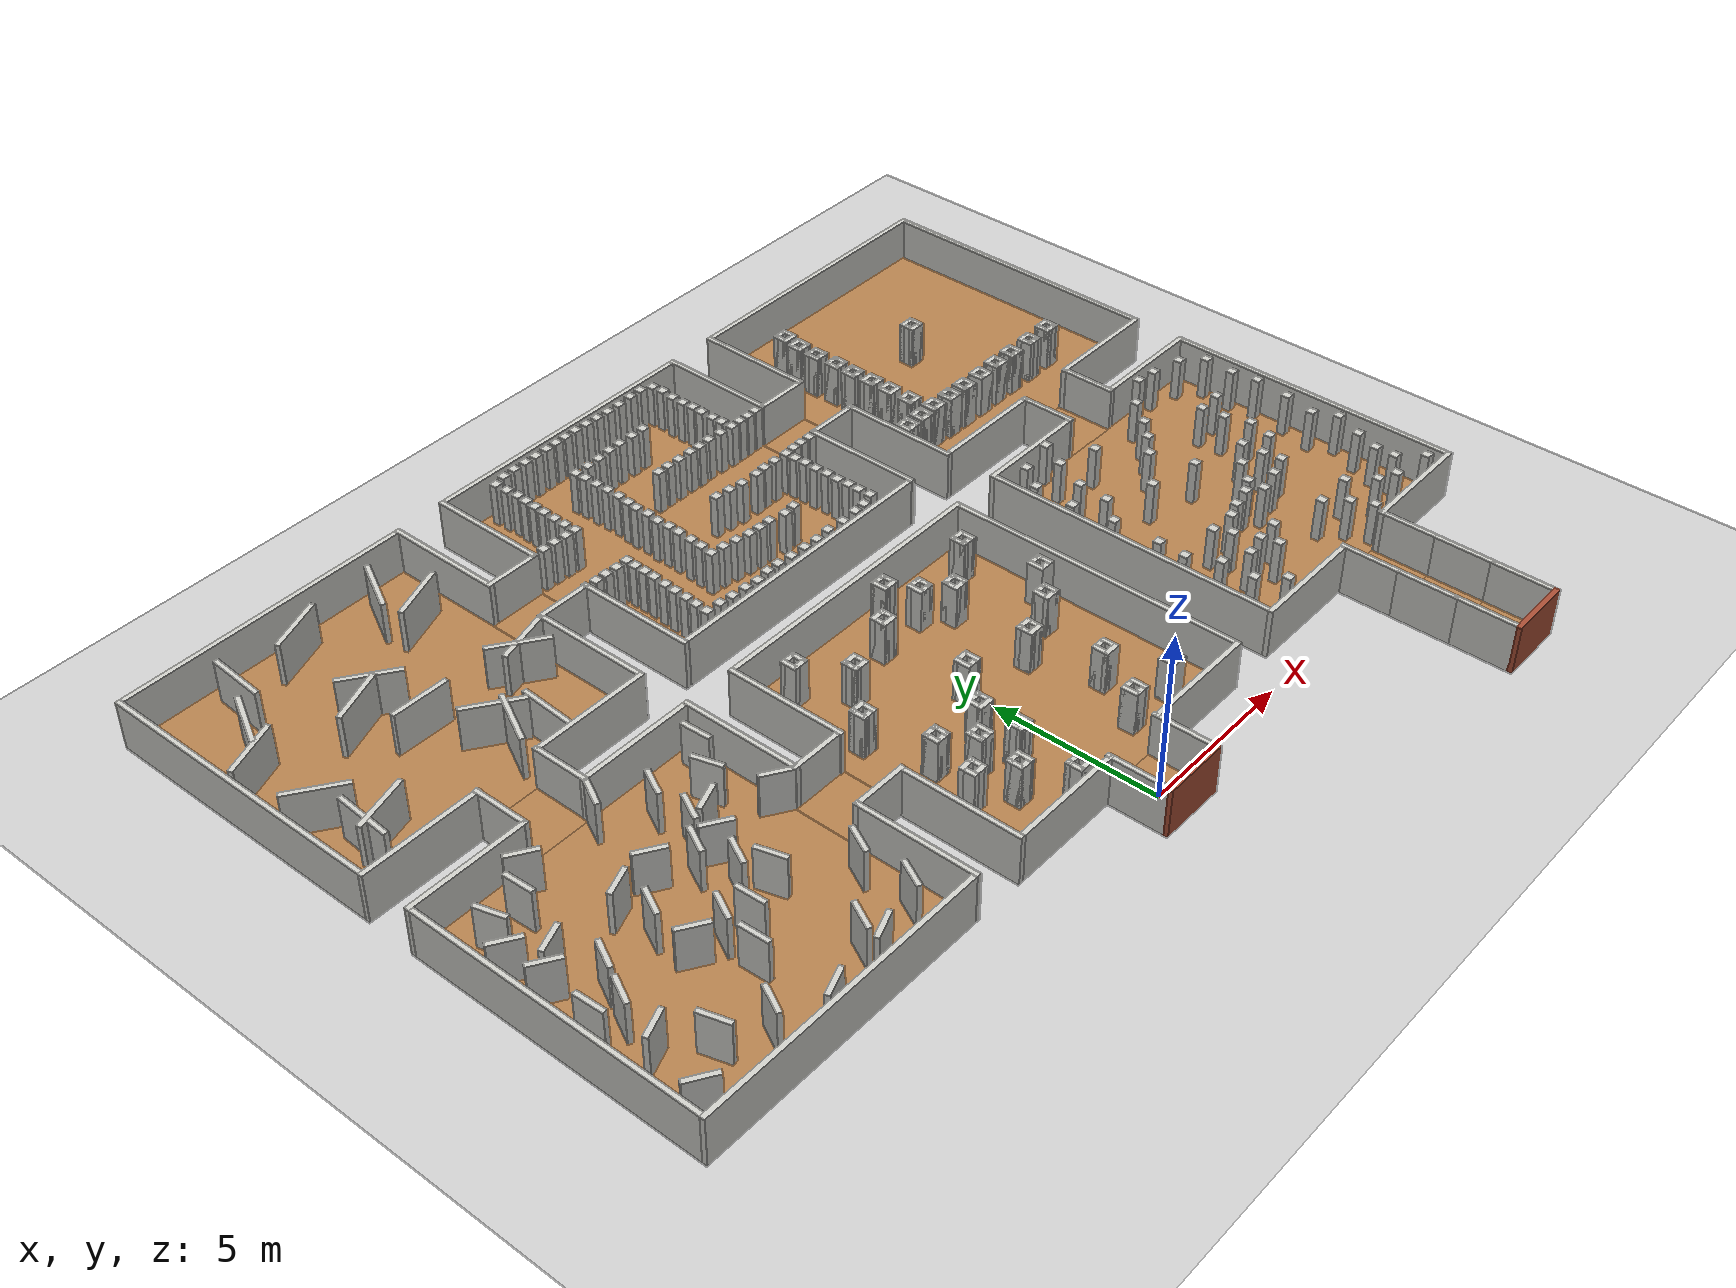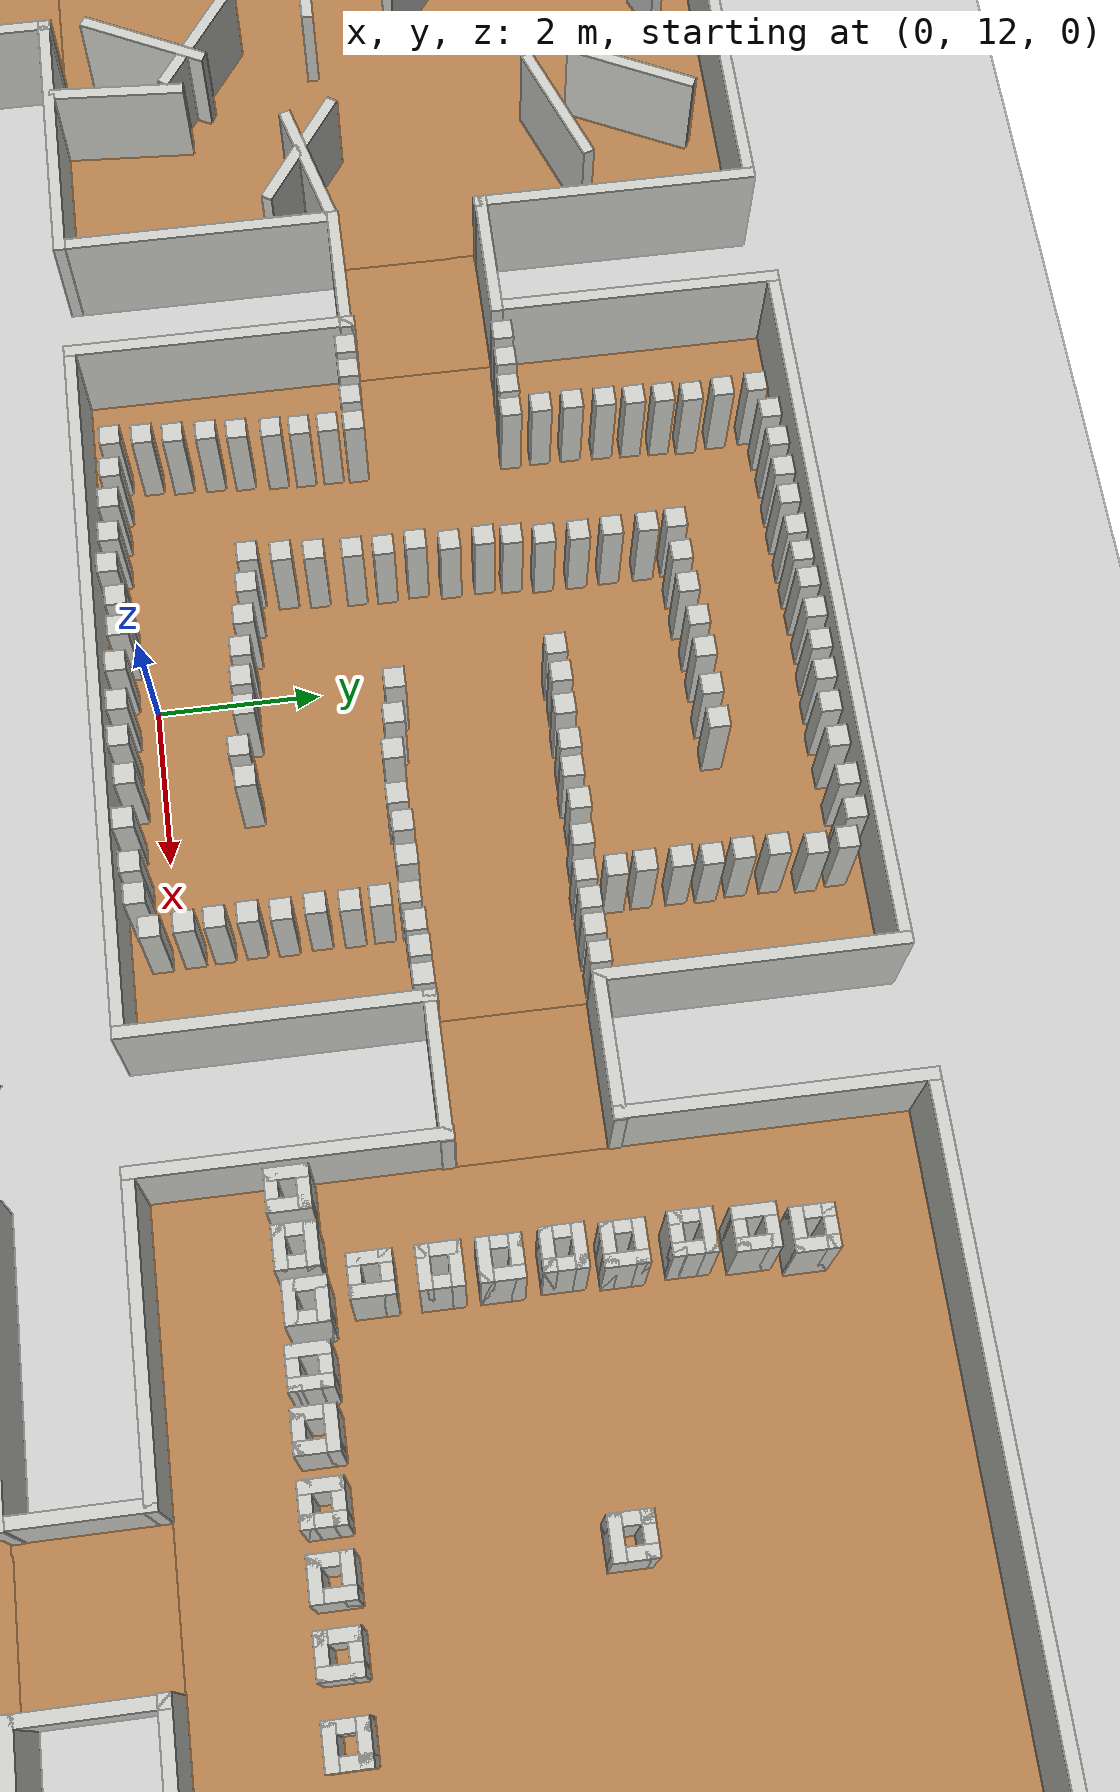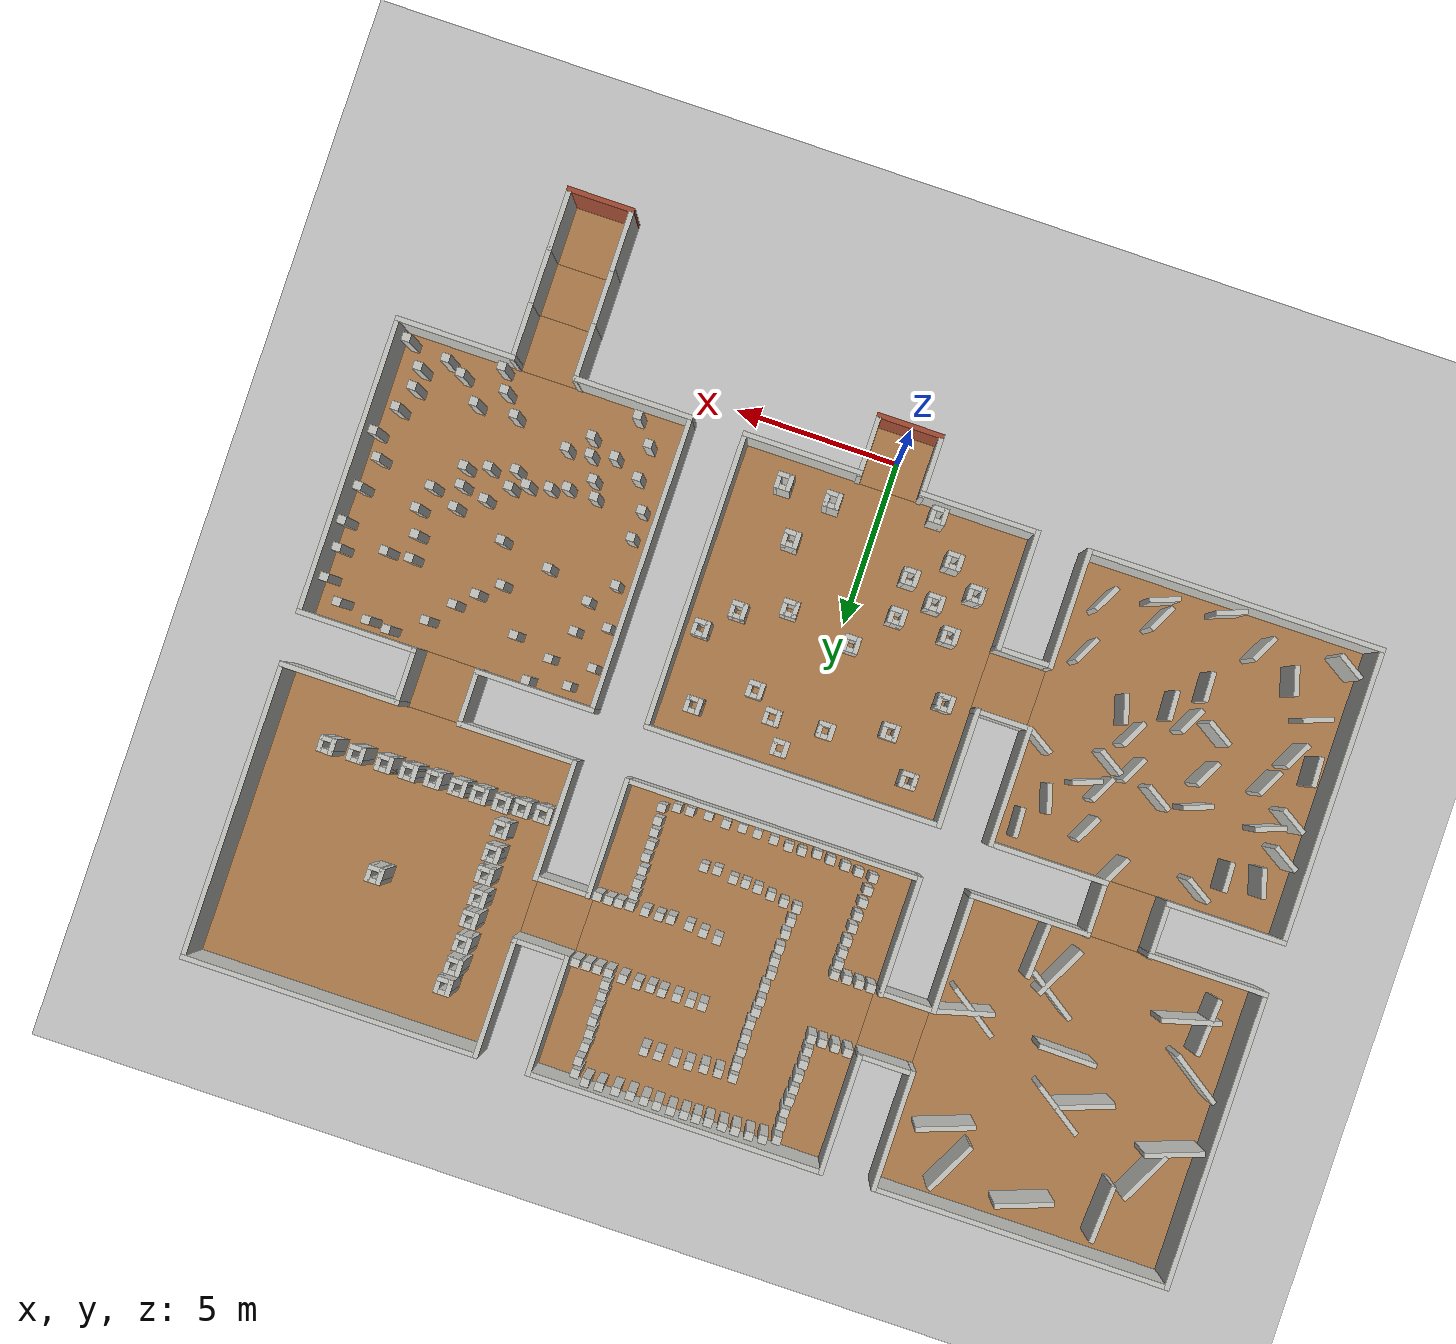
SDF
<sdf version="1.6">
 <world name="default">
  <light name="sun" type="directional">
   <pose>0 0 10 0 -0 0</pose>
   <diffuse>0.8 0.8 0.8 1</diffuse>
   <specular>0.1 0.1 0.1 1</specular>
   <attenuation>
    <range>1000</range>
    <constant>0.9</constant>
    <linear>0.01</linear>
    <quadratic>0.001</quadratic>
   </attenuation>
   <direction>-0.5 0.5 -1</direction>
  </light>
  <model name="ground_plane">
   <static>1</static>
   <link name="link">
    <collision name="collision">
     <geometry><plane><normal>0 0 1</normal><size>100 100</size></plane></geometry>
     <surface><friction><ode><mu>100</mu><mu2>50</mu2></ode></friction></surface>
    </collision>
    <visual name="visual">
     <cast_shadows>0</cast_shadows>
     <geometry><plane><normal>0 0 1</normal><size>100 100</size></plane></geometry>
     <material>
      <script><uri>file://media/materials/scripts/gazebo.material</uri><name>Gazebo/Grey</name></script>
     </material>
    </visual>
   </link>
  </model>
  <gravity>0 0 -9.8</gravity>
  <magnetic_field>6e-06 2.3e-05 -4.2e-05</magnetic_field>
  <atmosphere type="adiabatic"/>
  <physics name="default_physics" default="0" type="ode">
   <max_step_size>0.001</max_step_size>
   <real_time_factor>1</real_time_factor>
   <real_time_update_rate>1000</real_time_update_rate>
  </physics>
  <scene><ambient>0.4 0.4 0.4 1</ambient><background>0.7 0.7 0.7 1</background><shadows>1</shadows></scene>
  <spherical_coordinates>
   <surface_model>EARTH_WGS84</surface_model>
   <latitude_deg>0</latitude_deg>
   <longitude_deg>0</longitude_deg>
   <elevation>0</elevation>
   <heading_deg>0</heading_deg>
  </spherical_coordinates>
  <model name="nerve_end">
   <pose>0 0 0 0 -0 3.14159</pose>
   <link name="Wall_0">
    <collision name="Wall_0_Collision">
     <geometry><box><size>1.76 1.75 0.2</size></box></geometry>
     <pose>0 0 0.1 0 -0 0</pose>
    </collision>
    <visual name="Wall_0_Visual">
     <pose>0 0 0.1 0 -0 0</pose>
     <geometry><box><size>1.76 1.75 0.2</size></box></geometry>
     <material>
      <script><uri>file://media/materials/scripts/gazebo.material</uri><name>Gazebo/Wood</name></script>
      <ambient>1 0.764706 0.305882 1</ambient>
     </material>
    </visual>
    <pose>-0.009 -0.064 0 0 -0 0</pose>
   </link>
   <link name="Wall_2">
    <collision name="Wall_2_Collision">
     <geometry><box><size>1.8 0.15 1.5</size></box></geometry>
     <pose>0 0 0.75 0 -0 0</pose>
    </collision>
    <visual name="Wall_2_Visual">
     <pose>0 0 0.75 0 -0 0</pose>
     <geometry><box><size>1.8 0.15 1.5</size></box></geometry>
     <material>
      <script><uri>file://media/materials/scripts/gazebo.material</uri><name>Gazebo/CeilingTiled</name></script>
      <ambient>1 0.764706 0.305882 1</ambient>
     </material>
    </visual>
    <pose>-0.95 -0.065 0 0 0 -1.5708</pose>
   </link>
   <link name="Wall_4">
    <collision name="Wall_4_Collision">
     <geometry><box><size>1.8 0.15 1.5</size></box></geometry>
     <pose>0 0 0.75 0 -0 0</pose>
    </collision>
    <visual name="Wall_4_Visual">
     <pose>0 0 0.75 0 -0 0</pose>
     <geometry><box><size>1.8 0.15 1.5</size></box></geometry>
     <material>
      <script><uri>file://media/materials/scripts/gazebo.material</uri><name>Gazebo/CeilingTiled</name></script>
      <ambient>1 0.764706 0.305882 1</ambient>
     </material>
    </visual>
    <pose>0.95 -0.065 0 0 0 -1.5708</pose>
   </link>
   <link name="Wall_6">
    <collision name="Wall_6_Collision">
     <geometry><box><size>2.05 0.15 1.5</size></box></geometry>
     <pose>0 0 0.75 0 -0 0</pose>
    </collision>
    <visual name="Wall_6_Visual">
     <pose>0 0 0.75 0 -0 0</pose>
     <geometry><box><size>2.05 0.15 1.5</size></box></geometry>
     <material>
      <script><uri>file://media/materials/scripts/gazebo.material</uri><name>Gazebo/Bricks</name></script>
      <ambient>0.996078 0.47451 0.0196078 1</ambient>
     </material>
    </visual>
    <pose>0 0.89 0 0 -0 0</pose>
   </link>
   <static>1</static>
  </model>
  <model name="nerve_room_5x5ARENA_right">
   <pose>0.001326 5.29809 0 0 -0 0</pose>
   <link name="Wall_11">
    <collision name="Wall_11_Collision">
     <geometry><box><size>8.75 0.15 1.5</size></box></geometry>
     <pose>0 0 0.75 0 -0 0</pose>
    </collision>
    <visual name="Wall_11_Visual">
     <pose>0 0 0.75 0 -0 0</pose>
     <geometry><box><size>8.75 0.15 1.5</size></box></geometry>
     <material>
      <script><uri>file://media/materials/scripts/gazebo.material</uri><name>Gazebo/CeilingTiled</name></script>
      <ambient>1 0.764706 0.305882 1</ambient>
     </material>
    </visual>
    <pose>4.44912 -0.000431 0 0 0 -1.5708</pose>
   </link>
   <link name="Wall_13">
    <collision name="Wall_13_Collision">
     <geometry><box><size>3.65 0.15 1.5</size></box></geometry>
     <pose>0 0 0.75 0 -0 0</pose>
    </collision>
    <visual name="Wall_13_Visual">
     <pose>0 0 0.75 0 -0 0</pose>
     <geometry><box><size>3.65 0.15 1.5</size></box></geometry>
     <material>
      <script><uri>file://media/materials/scripts/gazebo.material</uri><name>Gazebo/CeilingTiled</name></script>
      <ambient>1 0.764706 0.305882 1</ambient>
     </material>
    </visual>
    <pose>-4.44961 2.70076 0 0 0 -1.5708</pose>
   </link>
   <link name="Wall_15">
    <collision name="Wall_15_Collision">
     <geometry><box><size>3.65 0.15 1.5</size></box></geometry>
     <pose>0 0 0.75 0 -0 0</pose>
    </collision>
    <visual name="Wall_15_Visual">
     <pose>0 0 0.75 0 -0 0</pose>
     <geometry><box><size>3.65 0.15 1.5</size></box></geometry>
     <material>
      <script><uri>file://media/materials/scripts/gazebo.material</uri><name>Gazebo/CeilingTiled</name></script>
      <ambient>1 0.764706 0.305882 1</ambient>
     </material>
    </visual>
    <pose>2.69961 -4.45076 0 0 -0 0</pose>
   </link>
   <link name="Wall_17">
    <collision name="Wall_17_Collision">
     <geometry><box><size>8.90028 0.15 1.5</size></box></geometry>
     <pose>0 0 0.75 0 -0 0</pose>
    </collision>
    <visual name="Wall_17_Visual">
     <pose>0 0 0.75 0 -0 0</pose>
     <geometry><box><size>8.90028 0.15 1.5</size></box></geometry>
     <material>
      <script><uri>file://media/materials/scripts/gazebo.material</uri><name>Gazebo/CeilingTiled</name></script>
      <ambient>1 0.764706 0.305882 1</ambient>
     </material>
    </visual>
    <pose>0.074346 4.45022 0 0 0 -6.5e-05</pose>
   </link>
   <link name="Wall_21">
    <collision name="Wall_21_Collision">
     <geometry><box><size>3.5 0.15 1.5</size></box></geometry>
     <pose>0 0 0.75 0 -0 0</pose>
    </collision>
    <visual name="Wall_21_Visual">
     <pose>0 0 0.75 0 -0 0</pose>
     <geometry><box><size>3.5 0.15 1.5</size></box></geometry>
     <material>
      <script><uri>file://media/materials/scripts/gazebo.material</uri><name>Gazebo/CeilingTiled</name></script>
      <ambient>1 0.764706 0.305882 1</ambient>
     </material>
    </visual>
    <pose>-2.62383 -4.4498 0 0 -0 0</pose>
   </link>
   <link name="Wall_25">
    <collision name="Wall_25_Collision">
     <geometry><box><size>3.65 0.15 1.5</size></box></geometry>
     <pose>0 0 0.75 0 -0 0</pose>
    </collision>
    <visual name="Wall_25_Visual">
     <pose>0 0 0.75 0 -0 0</pose>
     <geometry><box><size>3.65 0.15 1.5</size></box></geometry>
     <material>
      <script><uri>file://media/materials/scripts/gazebo.material</uri><name>Gazebo/CeilingTiled</name></script>
      <ambient>1 0.764706 0.305882 1</ambient>
     </material>
    </visual>
    <pose>-4.44941 -2.70044 0 0 0 -1.5708</pose>
   </link>
   <link name="Wall_6">
    <collision name="Wall_6_Collision">
     <geometry><box><size>8.76 8.75 0.2</size></box></geometry>
     <pose>0 0 0.1 0 -0 0</pose>
    </collision>
    <visual name="Wall_6_Visual">
     <pose>0 0 0.1 0 -0 0</pose>
     <geometry><box><size>8.76 8.75 0.2</size></box></geometry>
     <material>
      <script><uri>file://media/materials/scripts/gazebo.material</uri><name>Gazebo/Wood</name></script>
      <ambient>1 0.764706 0.305882 1</ambient>
     </material>
    </visual>
    <pose>0.000485 -0.004173 0 0 -0 1.5708</pose>
   </link>
   <static>1</static>
  </model>
  <model name="nerve_straight">
   <pose>-5.23966 5.3216 0 0 0 -1.5708</pose>
   <link name="Wall_0">
    <collision name="Wall_0_Collision">
     <geometry><box><size>1.76 1.75 0.2</size></box></geometry>
     <pose>0 0 0.1 0 -0 0</pose>
    </collision>
    <visual name="Wall_0_Visual">
     <pose>0 0 0.1 0 -0 0</pose>
     <geometry><box><size>1.76 1.75 0.2</size></box></geometry>
     <material>
      <script><uri>file://media/materials/scripts/gazebo.material</uri><name>Gazebo/Wood</name></script>
      <ambient>1 0.764706 0.305882 1</ambient>
     </material>
    </visual>
    <pose>0.005 -0.002 0 0 -0 3.14159</pose>
   </link>
   <link name="Wall_2">
    <collision name="Wall_2_Collision">
     <geometry><box><size>1.75 0.15 1.5</size></box></geometry>
     <pose>0 0 0.75 0 -0 0</pose>
    </collision>
    <visual name="Wall_2_Visual">
     <pose>0 0 0.75 0 -0 0</pose>
     <geometry><box><size>1.75 0.15 1.5</size></box></geometry>
     <material>
      <script><uri>file://media/materials/scripts/gazebo.material</uri><name>Gazebo/CeilingTiled</name></script>
      <ambient>1 0.764706 0.305882 1</ambient>
     </material>
    </visual>
    <pose>-0.955 0.002 0 0 0 -1.5708</pose>
   </link>
   <link name="Wall_4">
    <collision name="Wall_4_Collision">
     <geometry><box><size>1.75 0.15 1.5</size></box></geometry>
     <pose>0 0 0.75 0 -0 0</pose>
    </collision>
    <visual name="Wall_4_Visual">
     <pose>0 0 0.75 0 -0 0</pose>
     <geometry><box><size>1.75 0.15 1.5</size></box></geometry>
     <material>
      <script><uri>file://media/materials/scripts/gazebo.material</uri><name>Gazebo/CeilingTiled</name></script>
      <ambient>1 0.764706 0.305882 1</ambient>
     </material>
    </visual>
    <pose>0.955 0.002 0 0 0 -1.5708</pose>
   </link>
   <static>1</static>
  </model>
  <model name="nerve_room_5x5ARENA_right_0">
   <pose>-10.4849 5.32445 0 0 0 -3.14159</pose>
   <link name="Wall_11">
    <collision name="Wall_11_Collision">
     <geometry><box><size>8.75 0.15 1.5</size></box></geometry>
     <pose>0 0 0.75 0 -0 0</pose>
    </collision>
    <visual name="Wall_11_Visual">
     <pose>0 0 0.75 0 -0 0</pose>
     <geometry><box><size>8.75 0.15 1.5</size></box></geometry>
     <material>
      <script><uri>file://media/materials/scripts/gazebo.material</uri><name>Gazebo/CeilingTiled</name></script>
      <ambient>1 0.764706 0.305882 1</ambient>
     </material>
    </visual>
    <pose>4.44912 -0.000431 0 0 0 -1.5708</pose>
   </link>
   <link name="Wall_13">
    <collision name="Wall_13_Collision">
     <geometry><box><size>3.65 0.15 1.5</size></box></geometry>
     <pose>0 0 0.75 0 -0 0</pose>
    </collision>
    <visual name="Wall_13_Visual">
     <pose>0 0 0.75 0 -0 0</pose>
     <geometry><box><size>3.65 0.15 1.5</size></box></geometry>
     <material>
      <script><uri>file://media/materials/scripts/gazebo.material</uri><name>Gazebo/CeilingTiled</name></script>
      <ambient>1 0.764706 0.305882 1</ambient>
     </material>
    </visual>
    <pose>-4.44961 2.70076 0 0 0 -1.5708</pose>
   </link>
   <link name="Wall_15">
    <collision name="Wall_15_Collision">
     <geometry><box><size>3.65 0.15 1.5</size></box></geometry>
     <pose>0 0 0.75 0 -0 0</pose>
    </collision>
    <visual name="Wall_15_Visual">
     <pose>0 0 0.75 0 -0 0</pose>
     <geometry><box><size>3.65 0.15 1.5</size></box></geometry>
     <material>
      <script><uri>file://media/materials/scripts/gazebo.material</uri><name>Gazebo/CeilingTiled</name></script>
      <ambient>1 0.764706 0.305882 1</ambient>
     </material>
    </visual>
    <pose>2.69961 -4.45076 0 0 -0 0</pose>
   </link>
   <link name="Wall_17">
    <collision name="Wall_17_Collision">
     <geometry><box><size>8.90028 0.15 1.5</size></box></geometry>
     <pose>0 0 0.75 0 -0 0</pose>
    </collision>
    <visual name="Wall_17_Visual">
     <pose>0 0 0.75 0 -0 0</pose>
     <geometry><box><size>8.90028 0.15 1.5</size></box></geometry>
     <material>
      <script><uri>file://media/materials/scripts/gazebo.material</uri><name>Gazebo/CeilingTiled</name></script>
      <ambient>1 0.764706 0.305882 1</ambient>
     </material>
    </visual>
    <pose>0.074346 4.45022 0 0 0 -6.5e-05</pose>
   </link>
   <link name="Wall_21">
    <collision name="Wall_21_Collision">
     <geometry><box><size>3.5 0.15 1.5</size></box></geometry>
     <pose>0 0 0.75 0 -0 0</pose>
    </collision>
    <visual name="Wall_21_Visual">
     <pose>0 0 0.75 0 -0 0</pose>
     <geometry><box><size>3.5 0.15 1.5</size></box></geometry>
     <material>
      <script><uri>file://media/materials/scripts/gazebo.material</uri><name>Gazebo/CeilingTiled</name></script>
      <ambient>1 0.764706 0.305882 1</ambient>
     </material>
    </visual>
    <pose>-2.62383 -4.4498 0 0 -0 0</pose>
   </link>
   <link name="Wall_25">
    <collision name="Wall_25_Collision">
     <geometry><box><size>3.65 0.15 1.5</size></box></geometry>
     <pose>0 0 0.75 0 -0 0</pose>
    </collision>
    <visual name="Wall_25_Visual">
     <pose>0 0 0.75 0 -0 0</pose>
     <geometry><box><size>3.65 0.15 1.5</size></box></geometry>
     <material>
      <script><uri>file://media/materials/scripts/gazebo.material</uri><name>Gazebo/CeilingTiled</name></script>
      <ambient>1 0.764706 0.305882 1</ambient>
     </material>
    </visual>
    <pose>-4.44941 -2.70044 0 0 0 -1.5708</pose>
   </link>
   <link name="Wall_6">
    <collision name="Wall_6_Collision">
     <geometry><box><size>8.76 8.75 0.2</size></box></geometry>
     <pose>0 0 0.1 0 -0 0</pose>
    </collision>
    <visual name="Wall_6_Visual">
     <pose>0 0 0.1 0 -0 0</pose>
     <geometry><box><size>8.76 8.75 0.2</size></box></geometry>
     <material>
      <script><uri>file://media/materials/scripts/gazebo.material</uri><name>Gazebo/Wood</name></script>
      <ambient>1 0.764706 0.305882 1</ambient>
     </material>
    </visual>
    <pose>0.000485 -0.004173 0 0 -0 1.5708</pose>
   </link>
   <static>1</static>
  </model>
  <model name="nerve_straight_clone">
   <pose>-10.4732 10.573 0 0 -0 0</pose>
   <link name="Wall_0">
    <collision name="Wall_0_Collision">
     <geometry><box><size>1.76 1.75 0.2</size></box></geometry>
     <pose>0 0 0.1 0 -0 0</pose>
    </collision>
    <visual name="Wall_0_Visual">
     <pose>0 0 0.1 0 -0 0</pose>
     <geometry><box><size>1.76 1.75 0.2</size></box></geometry>
     <material>
      <script><uri>file://media/materials/scripts/gazebo.material</uri><name>Gazebo/Wood</name></script>
      <ambient>1 0.764706 0.305882 1</ambient>
     </material>
    </visual>
    <pose>0.005 -0.002 0 0 -0 3.14159</pose>
   </link>
   <link name="Wall_2">
    <collision name="Wall_2_Collision">
     <geometry><box><size>1.75 0.15 1.5</size></box></geometry>
     <pose>0 0 0.75 0 -0 0</pose>
    </collision>
    <visual name="Wall_2_Visual">
     <pose>0 0 0.75 0 -0 0</pose>
     <geometry><box><size>1.75 0.15 1.5</size></box></geometry>
     <material>
      <script><uri>file://media/materials/scripts/gazebo.material</uri><name>Gazebo/CeilingTiled</name></script>
      <ambient>1 0.764706 0.305882 1</ambient>
     </material>
    </visual>
    <pose>-0.955 0.002 0 0 0 -1.5708</pose>
   </link>
   <link name="Wall_4">
    <collision name="Wall_4_Collision">
     <geometry><box><size>1.75 0.15 1.5</size></box></geometry>
     <pose>0 0 0.75 0 -0 0</pose>
    </collision>
    <visual name="Wall_4_Visual">
     <pose>0 0 0.75 0 -0 0</pose>
     <geometry><box><size>1.75 0.15 1.5</size></box></geometry>
     <material>
      <script><uri>file://media/materials/scripts/gazebo.material</uri><name>Gazebo/CeilingTiled</name></script>
      <ambient>1 0.764706 0.305882 1</ambient>
     </material>
    </visual>
    <pose>0.955 0.002 0 0 0 -1.5708</pose>
   </link>
   <static>1</static>
  </model>
  <model name="nerve_room_5x5ARENA_right_clone">
   <pose>-10.4631 15.8033 0 0 -0 1.5708</pose>
   <link name="Wall_11">
    <collision name="Wall_11_Collision">
     <geometry><box><size>8.75 0.15 1.5</size></box></geometry>
     <pose>0 0 0.75 0 -0 0</pose>
    </collision>
    <visual name="Wall_11_Visual">
     <pose>0 0 0.75 0 -0 0</pose>
     <geometry><box><size>8.75 0.15 1.5</size></box></geometry>
     <material>
      <script><uri>file://media/materials/scripts/gazebo.material</uri><name>Gazebo/CeilingTiled</name></script>
      <ambient>1 0.764706 0.305882 1</ambient>
     </material>
    </visual>
    <pose>4.44912 -0.000431 0 0 0 -1.5708</pose>
   </link>
   <link name="Wall_13">
    <collision name="Wall_13_Collision">
     <geometry><box><size>3.65 0.15 1.5</size></box></geometry>
     <pose>0 0 0.75 0 -0 0</pose>
    </collision>
    <visual name="Wall_13_Visual">
     <pose>0 0 0.75 0 -0 0</pose>
     <geometry><box><size>3.65 0.15 1.5</size></box></geometry>
     <material>
      <script><uri>file://media/materials/scripts/gazebo.material</uri><name>Gazebo/CeilingTiled</name></script>
      <ambient>1 0.764706 0.305882 1</ambient>
     </material>
    </visual>
    <pose>-4.44961 2.70076 0 0 0 -1.5708</pose>
   </link>
   <link name="Wall_15">
    <collision name="Wall_15_Collision">
     <geometry><box><size>3.65 0.15 1.5</size></box></geometry>
     <pose>0 0 0.75 0 -0 0</pose>
    </collision>
    <visual name="Wall_15_Visual">
     <pose>0 0 0.75 0 -0 0</pose>
     <geometry><box><size>3.65 0.15 1.5</size></box></geometry>
     <material>
      <script><uri>file://media/materials/scripts/gazebo.material</uri><name>Gazebo/CeilingTiled</name></script>
      <ambient>1 0.764706 0.305882 1</ambient>
     </material>
    </visual>
    <pose>2.69961 -4.45076 0 0 -0 0</pose>
   </link>
   <link name="Wall_17">
    <collision name="Wall_17_Collision">
     <geometry><box><size>8.90028 0.15 1.5</size></box></geometry>
     <pose>0 0 0.75 0 -0 0</pose>
    </collision>
    <visual name="Wall_17_Visual">
     <pose>0 0 0.75 0 -0 0</pose>
     <geometry><box><size>8.90028 0.15 1.5</size></box></geometry>
     <material>
      <script><uri>file://media/materials/scripts/gazebo.material</uri><name>Gazebo/CeilingTiled</name></script>
      <ambient>1 0.764706 0.305882 1</ambient>
     </material>
    </visual>
    <pose>0.074346 4.45022 0 0 0 -6.5e-05</pose>
   </link>
   <link name="Wall_21">
    <collision name="Wall_21_Collision">
     <geometry><box><size>3.5 0.15 1.5</size></box></geometry>
     <pose>0 0 0.75 0 -0 0</pose>
    </collision>
    <visual name="Wall_21_Visual">
     <pose>0 0 0.75 0 -0 0</pose>
     <geometry><box><size>3.5 0.15 1.5</size></box></geometry>
     <material>
      <script><uri>file://media/materials/scripts/gazebo.material</uri><name>Gazebo/CeilingTiled</name></script>
      <ambient>1 0.764706 0.305882 1</ambient>
     </material>
    </visual>
    <pose>-2.62383 -4.4498 0 0 -0 0</pose>
   </link>
   <link name="Wall_25">
    <collision name="Wall_25_Collision">
     <geometry><box><size>3.65 0.15 1.5</size></box></geometry>
     <pose>0 0 0.75 0 -0 0</pose>
    </collision>
    <visual name="Wall_25_Visual">
     <pose>0 0 0.75 0 -0 0</pose>
     <geometry><box><size>3.65 0.15 1.5</size></box></geometry>
     <material>
      <script><uri>file://media/materials/scripts/gazebo.material</uri><name>Gazebo/CeilingTiled</name></script>
      <ambient>1 0.764706 0.305882 1</ambient>
     </material>
    </visual>
    <pose>-4.44941 -2.70044 0 0 0 -1.5708</pose>
   </link>
   <link name="Wall_6">
    <collision name="Wall_6_Collision">
     <geometry><box><size>8.76 8.75 0.2</size></box></geometry>
     <pose>0 0 0.1 0 -0 0</pose>
    </collision>
    <visual name="Wall_6_Visual">
     <pose>0 0 0.1 0 -0 0</pose>
     <geometry><box><size>8.76 8.75 0.2</size></box></geometry>
     <material>
      <script><uri>file://media/materials/scripts/gazebo.material</uri><name>Gazebo/Wood</name></script>
      <ambient>1 0.764706 0.305882 1</ambient>
     </material>
    </visual>
    <pose>0.000485 -0.004173 0 0 -0 1.5708</pose>
   </link>
   <static>1</static>
  </model>
  <model name="nerve_room_5x5ARENA_straight">
   <pose>0.031546 15.8425 0 0 -0 1.5708</pose>
   <link name="Wall_11">
    <collision name="Wall_11_Collision">
     <geometry><box><size>8.75 0.15 1.5</size></box></geometry>
     <pose>0 0 0.75 0 -0 0</pose>
    </collision>
    <visual name="Wall_11_Visual">
     <pose>0 0 0.75 0 -0 0</pose>
     <geometry><box><size>8.75 0.15 1.5</size></box></geometry>
     <material>
      <script><uri>file://media/materials/scripts/gazebo.material</uri><name>Gazebo/CeilingTiled</name></script>
      <ambient>1 0.764706 0.305882 1</ambient>
     </material>
    </visual>
    <pose>4.4489 -0.000387 0 0 0 -1.5708</pose>
   </link>
   <link name="Wall_13">
    <collision name="Wall_13_Collision">
     <geometry><box><size>8.75 0.15 1.5</size></box></geometry>
     <pose>0 0 0.75 0 -0 0</pose>
    </collision>
    <visual name="Wall_13_Visual">
     <pose>0 0 0.75 0 -0 0</pose>
     <geometry><box><size>8.75 0.15 1.5</size></box></geometry>
     <material>
      <script><uri>file://media/materials/scripts/gazebo.material</uri><name>Gazebo/CeilingTiled</name></script>
      <ambient>1 0.764706 0.305882 1</ambient>
     </material>
    </visual>
    <pose>-4.44913 0.000846 0 0 0 -1.5708</pose>
   </link>
   <link name="Wall_15">
    <collision name="Wall_15_Collision">
     <geometry><box><size>3.65 0.15 1.5</size></box></geometry>
     <pose>0 0 0.75 0 -0 0</pose>
    </collision>
    <visual name="Wall_15_Visual">
     <pose>0 0 0.75 0 -0 0</pose>
     <geometry><box><size>3.65 0.15 1.5</size></box></geometry>
     <material>
      <script><uri>file://media/materials/scripts/gazebo.material</uri><name>Gazebo/CeilingTiled</name></script>
      <ambient>1 0.764706 0.305882 1</ambient>
     </material>
    </visual>
    <pose>2.69939 -4.45071 0 0 -0 0</pose>
   </link>
   <link name="Wall_17">
    <collision name="Wall_17_Collision">
     <geometry><box><size>3.65 0.15 1.5</size></box></geometry>
     <pose>0 0 0.75 0 -0 0</pose>
    </collision>
    <visual name="Wall_17_Visual">
     <pose>0 0 0.75 0 -0 0</pose>
     <geometry><box><size>3.65 0.15 1.5</size></box></geometry>
     <material>
      <script><uri>file://media/materials/scripts/gazebo.material</uri><name>Gazebo/CeilingTiled</name></script>
      <ambient>1 0.764706 0.305882 1</ambient>
     </material>
    </visual>
    <pose>-2.69939 4.45071 0 0 -0 0</pose>
   </link>
   <link name="Wall_19">
    <collision name="Wall_19_Collision">
     <geometry><box><size>3.65 0.15 1.5</size></box></geometry>
     <pose>0 0 0.75 0 -0 0</pose>
    </collision>
    <visual name="Wall_19_Visual">
     <pose>0 0 0.75 0 -0 0</pose>
     <geometry><box><size>3.65 0.15 1.5</size></box></geometry>
     <material>
      <script><uri>file://media/materials/scripts/gazebo.material</uri><name>Gazebo/CeilingTiled</name></script>
      <ambient>1 0.764706 0.305882 1</ambient>
     </material>
    </visual>
    <pose>2.69903 4.44972 0 0 -0 0</pose>
   </link>
   <link name="Wall_21">
    <collision name="Wall_21_Collision">
     <geometry><box><size>3.65 0.15 1.5</size></box></geometry>
     <pose>0 0 0.75 0 -0 0</pose>
    </collision>
    <visual name="Wall_21_Visual">
     <pose>0 0 0.75 0 -0 0</pose>
     <geometry><box><size>3.65 0.15 1.5</size></box></geometry>
     <material>
      <script><uri>file://media/materials/scripts/gazebo.material</uri><name>Gazebo/CeilingTiled</name></script>
      <ambient>1 0.764706 0.305882 1</ambient>
     </material>
    </visual>
    <pose>-2.69904 -4.44976 0 0 -0 0</pose>
   </link>
   <link name="Wall_6">
    <collision name="Wall_6_Collision">
     <geometry><box><size>8.76 8.75 0.2</size></box></geometry>
     <pose>0 0 0.1 0 -0 0</pose>
    </collision>
    <visual name="Wall_6_Visual">
     <pose>0 0 0.1 0 -0 0</pose>
     <geometry><box><size>8.76 8.75 0.2</size></box></geometry>
     <material>
      <script><uri>file://media/materials/scripts/gazebo.material</uri><name>Gazebo/Wood</name></script>
      <ambient>1 0.764706 0.305882 1</ambient>
     </material>
    </visual>
    <pose>0.000265 -0.004129 0 0 -0 1.5708</pose>
   </link>
   <static>1</static>
  </model>
  <model name="nerve_room_5x5ARENA_right_clone_clone">
   <pose>10.5243 15.8402 0 0 -0 0</pose>
   <link name="Wall_11">
    <collision name="Wall_11_Collision">
     <geometry><box><size>8.75 0.15 1.5</size></box></geometry>
     <pose>0 0 0.75 0 -0 0</pose>
    </collision>
    <visual name="Wall_11_Visual">
     <pose>0 0 0.75 0 -0 0</pose>
     <geometry><box><size>8.75 0.15 1.5</size></box></geometry>
     <material>
      <script><uri>file://media/materials/scripts/gazebo.material</uri><name>Gazebo/CeilingTiled</name></script>
      <ambient>1 0.764706 0.305882 1</ambient>
     </material>
    </visual>
    <pose>4.44912 -0.000431 0 0 0 -1.5708</pose>
   </link>
   <link name="Wall_13">
    <collision name="Wall_13_Collision">
     <geometry><box><size>3.65 0.15 1.5</size></box></geometry>
     <pose>0 0 0.75 0 -0 0</pose>
    </collision>
    <visual name="Wall_13_Visual">
     <pose>0 0 0.75 0 -0 0</pose>
     <geometry><box><size>3.65 0.15 1.5</size></box></geometry>
     <material>
      <script><uri>file://media/materials/scripts/gazebo.material</uri><name>Gazebo/CeilingTiled</name></script>
      <ambient>1 0.764706 0.305882 1</ambient>
     </material>
    </visual>
    <pose>-4.44961 2.70076 0 0 0 -1.5708</pose>
   </link>
   <link name="Wall_15">
    <collision name="Wall_15_Collision">
     <geometry><box><size>3.65 0.15 1.5</size></box></geometry>
     <pose>0 0 0.75 0 -0 0</pose>
    </collision>
    <visual name="Wall_15_Visual">
     <pose>0 0 0.75 0 -0 0</pose>
     <geometry><box><size>3.65 0.15 1.5</size></box></geometry>
     <material>
      <script><uri>file://media/materials/scripts/gazebo.material</uri><name>Gazebo/CeilingTiled</name></script>
      <ambient>1 0.764706 0.305882 1</ambient>
     </material>
    </visual>
    <pose>2.69961 -4.45076 0 0 -0 0</pose>
   </link>
   <link name="Wall_17">
    <collision name="Wall_17_Collision">
     <geometry><box><size>8.90028 0.15 1.5</size></box></geometry>
     <pose>0 0 0.75 0 -0 0</pose>
    </collision>
    <visual name="Wall_17_Visual">
     <pose>0 0 0.75 0 -0 0</pose>
     <geometry><box><size>8.90028 0.15 1.5</size></box></geometry>
     <material>
      <script><uri>file://media/materials/scripts/gazebo.material</uri><name>Gazebo/CeilingTiled</name></script>
      <ambient>1 0.764706 0.305882 1</ambient>
     </material>
    </visual>
    <pose>0.074346 4.45022 0 0 0 -6.5e-05</pose>
   </link>
   <link name="Wall_21">
    <collision name="Wall_21_Collision">
     <geometry><box><size>3.5 0.15 1.5</size></box></geometry>
     <pose>0 0 0.75 0 -0 0</pose>
    </collision>
    <visual name="Wall_21_Visual">
     <pose>0 0 0.75 0 -0 0</pose>
     <geometry><box><size>3.5 0.15 1.5</size></box></geometry>
     <material>
      <script><uri>file://media/materials/scripts/gazebo.material</uri><name>Gazebo/CeilingTiled</name></script>
      <ambient>1 0.764706 0.305882 1</ambient>
     </material>
    </visual>
    <pose>-2.62383 -4.4498 0 0 -0 0</pose>
   </link>
   <link name="Wall_25">
    <collision name="Wall_25_Collision">
     <geometry><box><size>3.65 0.15 1.5</size></box></geometry>
     <pose>0 0 0.75 0 -0 0</pose>
    </collision>
    <visual name="Wall_25_Visual">
     <pose>0 0 0.75 0 -0 0</pose>
     <geometry><box><size>3.65 0.15 1.5</size></box></geometry>
     <material>
      <script><uri>file://media/materials/scripts/gazebo.material</uri><name>Gazebo/CeilingTiled</name></script>
      <ambient>1 0.764706 0.305882 1</ambient>
     </material>
    </visual>
    <pose>-4.44941 -2.70044 0 0 0 -1.5708</pose>
   </link>
   <link name="Wall_6">
    <collision name="Wall_6_Collision">
     <geometry><box><size>8.76 8.75 0.2</size></box></geometry>
     <pose>0 0 0.1 0 -0 0</pose>
    </collision>
    <visual name="Wall_6_Visual">
     <pose>0 0 0.1 0 -0 0</pose>
     <geometry><box><size>8.76 8.75 0.2</size></box></geometry>
     <material>
      <script><uri>file://media/materials/scripts/gazebo.material</uri><name>Gazebo/Wood</name></script>
      <ambient>1 0.764706 0.305882 1</ambient>
     </material>
    </visual>
    <pose>0.000485 -0.004173 0 0 -0 1.5708</pose>
   </link>
   <static>1</static>
  </model>
  <model name="nerve_room_5x5ARENA_straight_clone">
   <pose>10.535 5.35033 0 0 -0 0</pose>
   <link name="Wall_11">
    <collision name="Wall_11_Collision">
     <geometry><box><size>8.75 0.15 1.5</size></box></geometry>
     <pose>0 0 0.75 0 -0 0</pose>
    </collision>
    <visual name="Wall_11_Visual">
     <pose>0 0 0.75 0 -0 0</pose>
     <geometry><box><size>8.75 0.15 1.5</size></box></geometry>
     <material>
      <script><uri>file://media/materials/scripts/gazebo.material</uri><name>Gazebo/CeilingTiled</name></script>
      <ambient>1 0.764706 0.305882 1</ambient>
     </material>
    </visual>
    <pose>4.4489 -0.000387 0 0 0 -1.5708</pose>
   </link>
   <link name="Wall_13">
    <collision name="Wall_13_Collision">
     <geometry><box><size>8.75 0.15 1.5</size></box></geometry>
     <pose>0 0 0.75 0 -0 0</pose>
    </collision>
    <visual name="Wall_13_Visual">
     <pose>0 0 0.75 0 -0 0</pose>
     <geometry><box><size>8.75 0.15 1.5</size></box></geometry>
     <material>
      <script><uri>file://media/materials/scripts/gazebo.material</uri><name>Gazebo/CeilingTiled</name></script>
      <ambient>1 0.764706 0.305882 1</ambient>
     </material>
    </visual>
    <pose>-4.44913 0.000846 0 0 0 -1.5708</pose>
   </link>
   <link name="Wall_15">
    <collision name="Wall_15_Collision">
     <geometry><box><size>3.65 0.15 1.5</size></box></geometry>
     <pose>0 0 0.75 0 -0 0</pose>
    </collision>
    <visual name="Wall_15_Visual">
     <pose>0 0 0.75 0 -0 0</pose>
     <geometry><box><size>3.65 0.15 1.5</size></box></geometry>
     <material>
      <script><uri>file://media/materials/scripts/gazebo.material</uri><name>Gazebo/CeilingTiled</name></script>
      <ambient>1 0.764706 0.305882 1</ambient>
     </material>
    </visual>
    <pose>2.69939 -4.45071 0 0 -0 0</pose>
   </link>
   <link name="Wall_17">
    <collision name="Wall_17_Collision">
     <geometry><box><size>3.65 0.15 1.5</size></box></geometry>
     <pose>0 0 0.75 0 -0 0</pose>
    </collision>
    <visual name="Wall_17_Visual">
     <pose>0 0 0.75 0 -0 0</pose>
     <geometry><box><size>3.65 0.15 1.5</size></box></geometry>
     <material>
      <script><uri>file://media/materials/scripts/gazebo.material</uri><name>Gazebo/CeilingTiled</name></script>
      <ambient>1 0.764706 0.305882 1</ambient>
     </material>
    </visual>
    <pose>-2.69939 4.45071 0 0 -0 0</pose>
   </link>
   <link name="Wall_19">
    <collision name="Wall_19_Collision">
     <geometry><box><size>3.65 0.15 1.5</size></box></geometry>
     <pose>0 0 0.75 0 -0 0</pose>
    </collision>
    <visual name="Wall_19_Visual">
     <pose>0 0 0.75 0 -0 0</pose>
     <geometry><box><size>3.65 0.15 1.5</size></box></geometry>
     <material>
      <script><uri>file://media/materials/scripts/gazebo.material</uri><name>Gazebo/CeilingTiled</name></script>
      <ambient>1 0.764706 0.305882 1</ambient>
     </material>
    </visual>
    <pose>2.69903 4.44972 0 0 -0 0</pose>
   </link>
   <link name="Wall_21">
    <collision name="Wall_21_Collision">
     <geometry><box><size>3.65 0.15 1.5</size></box></geometry>
     <pose>0 0 0.75 0 -0 0</pose>
    </collision>
    <visual name="Wall_21_Visual">
     <pose>0 0 0.75 0 -0 0</pose>
     <geometry><box><size>3.65 0.15 1.5</size></box></geometry>
     <material>
      <script><uri>file://media/materials/scripts/gazebo.material</uri><name>Gazebo/CeilingTiled</name></script>
      <ambient>1 0.764706 0.305882 1</ambient>
     </material>
    </visual>
    <pose>-2.69904 -4.44976 0 0 -0 0</pose>
   </link>
   <link name="Wall_6">
    <collision name="Wall_6_Collision">
     <geometry><box><size>8.76 8.75 0.2</size></box></geometry>
     <pose>0 0 0.1 0 -0 0</pose>
    </collision>
    <visual name="Wall_6_Visual">
     <pose>0 0 0.1 0 -0 0</pose>
     <geometry><box><size>8.76 8.75 0.2</size></box></geometry>
     <material>
      <script><uri>file://media/materials/scripts/gazebo.material</uri><name>Gazebo/Wood</name></script>
      <ambient>1 0.764706 0.305882 1</ambient>
     </material>
    </visual>
    <pose>0.000265 -0.004129 0 0 -0 1.5708</pose>
   </link>
   <static>1</static>
  </model>
  <model name="nerve_end_clone">
   <pose>10.5356 -3.31521 0 0 -0 3.14159</pose>
   <link name="Wall_0">
    <collision name="Wall_0_Collision">
     <geometry><box><size>1.76 1.75 0.2</size></box></geometry>
     <pose>0 0 0.1 0 -0 0</pose>
    </collision>
    <visual name="Wall_0_Visual">
     <pose>0 0 0.1 0 -0 0</pose>
     <geometry><box><size>1.76 1.75 0.2</size></box></geometry>
     <material>
      <script><uri>file://media/materials/scripts/gazebo.material</uri><name>Gazebo/Wood</name></script>
      <ambient>1 0.764706 0.305882 1</ambient>
     </material>
    </visual>
    <pose>-0.009 -0.064 0 0 -0 0</pose>
   </link>
   <link name="Wall_2">
    <collision name="Wall_2_Collision">
     <geometry><box><size>1.8 0.15 1.5</size></box></geometry>
     <pose>0 0 0.75 0 -0 0</pose>
    </collision>
    <visual name="Wall_2_Visual">
     <pose>0 0 0.75 0 -0 0</pose>
     <geometry><box><size>1.8 0.15 1.5</size></box></geometry>
     <material>
      <script><uri>file://media/materials/scripts/gazebo.material</uri><name>Gazebo/CeilingTiled</name></script>
      <ambient>1 0.764706 0.305882 1</ambient>
     </material>
    </visual>
    <pose>-0.95 -0.065 0 0 0 -1.5708</pose>
   </link>
   <link name="Wall_4">
    <collision name="Wall_4_Collision">
     <geometry><box><size>1.8 0.15 1.5</size></box></geometry>
     <pose>0 0 0.75 0 -0 0</pose>
    </collision>
    <visual name="Wall_4_Visual">
     <pose>0 0 0.75 0 -0 0</pose>
     <geometry><box><size>1.8 0.15 1.5</size></box></geometry>
     <material>
      <script><uri>file://media/materials/scripts/gazebo.material</uri><name>Gazebo/CeilingTiled</name></script>
      <ambient>1 0.764706 0.305882 1</ambient>
     </material>
    </visual>
    <pose>0.95 -0.065 0 0 0 -1.5708</pose>
   </link>
   <link name="Wall_6">
    <collision name="Wall_6_Collision">
     <geometry><box><size>2.05 0.15 1.5</size></box></geometry>
     <pose>0 0 0.75 0 -0 0</pose>
    </collision>
    <visual name="Wall_6_Visual">
     <pose>0 0 0.75 0 -0 0</pose>
     <geometry><box><size>2.05 0.15 1.5</size></box></geometry>
     <material>
      <script><uri>file://media/materials/scripts/gazebo.material</uri><name>Gazebo/Bricks</name></script>
      <ambient>0.996078 0.47451 0.0196078 1</ambient>
     </material>
    </visual>
    <pose>0 0.89 0 0 -0 0</pose>
   </link>
   <static>1</static>
  </model>
  <model name="nerve_straight_clone_clone">
   <pose>-5.21273 15.8107 0 0 0 -1.5708</pose>
   <link name="Wall_0">
    <collision name="Wall_0_Collision">
     <geometry><box><size>1.76 1.75 0.2</size></box></geometry>
     <pose>0 0 0.1 0 -0 0</pose>
    </collision>
    <visual name="Wall_0_Visual">
     <pose>0 0 0.1 0 -0 0</pose>
     <geometry><box><size>1.76 1.75 0.2</size></box></geometry>
     <material>
      <script><uri>file://media/materials/scripts/gazebo.material</uri><name>Gazebo/Wood</name></script>
      <ambient>1 0.764706 0.305882 1</ambient>
     </material>
    </visual>
    <pose>0.005 -0.002 0 0 -0 3.14159</pose>
   </link>
   <link name="Wall_2">
    <collision name="Wall_2_Collision">
     <geometry><box><size>1.75 0.15 1.5</size></box></geometry>
     <pose>0 0 0.75 0 -0 0</pose>
    </collision>
    <visual name="Wall_2_Visual">
     <pose>0 0 0.75 0 -0 0</pose>
     <geometry><box><size>1.75 0.15 1.5</size></box></geometry>
     <material>
      <script><uri>file://media/materials/scripts/gazebo.material</uri><name>Gazebo/CeilingTiled</name></script>
      <ambient>1 0.764706 0.305882 1</ambient>
     </material>
    </visual>
    <pose>-0.955 0.002 0 0 0 -1.5708</pose>
   </link>
   <link name="Wall_4">
    <collision name="Wall_4_Collision">
     <geometry><box><size>1.75 0.15 1.5</size></box></geometry>
     <pose>0 0 0.75 0 -0 0</pose>
    </collision>
    <visual name="Wall_4_Visual">
     <pose>0 0 0.75 0 -0 0</pose>
     <geometry><box><size>1.75 0.15 1.5</size></box></geometry>
     <material>
      <script><uri>file://media/materials/scripts/gazebo.material</uri><name>Gazebo/CeilingTiled</name></script>
      <ambient>1 0.764706 0.305882 1</ambient>
     </material>
    </visual>
    <pose>0.955 0.002 0 0 0 -1.5708</pose>
   </link>
   <static>1</static>
  </model>
  <model name="nerve_straight_clone_clone_0">
   <pose>5.28572 15.8348 0 0 0 -1.5708</pose>
   <link name="Wall_0">
    <collision name="Wall_0_Collision">
     <geometry><box><size>1.76 1.75 0.2</size></box></geometry>
     <pose>0 0 0.1 0 -0 0</pose>
    </collision>
    <visual name="Wall_0_Visual">
     <pose>0 0 0.1 0 -0 0</pose>
     <geometry><box><size>1.76 1.75 0.2</size></box></geometry>
     <material>
      <script><uri>file://media/materials/scripts/gazebo.material</uri><name>Gazebo/Wood</name></script>
      <ambient>1 0.764706 0.305882 1</ambient>
     </material>
    </visual>
    <pose>0.005 -0.002 0 0 -0 3.14159</pose>
   </link>
   <link name="Wall_2">
    <collision name="Wall_2_Collision">
     <geometry><box><size>1.75 0.15 1.5</size></box></geometry>
     <pose>0 0 0.75 0 -0 0</pose>
    </collision>
    <visual name="Wall_2_Visual">
     <pose>0 0 0.75 0 -0 0</pose>
     <geometry><box><size>1.75 0.15 1.5</size></box></geometry>
     <material>
      <script><uri>file://media/materials/scripts/gazebo.material</uri><name>Gazebo/CeilingTiled</name></script>
      <ambient>1 0.764706 0.305882 1</ambient>
     </material>
    </visual>
    <pose>-0.955 0.002 0 0 0 -1.5708</pose>
   </link>
   <link name="Wall_4">
    <collision name="Wall_4_Collision">
     <geometry><box><size>1.75 0.15 1.5</size></box></geometry>
     <pose>0 0 0.75 0 -0 0</pose>
    </collision>
    <visual name="Wall_4_Visual">
     <pose>0 0 0.75 0 -0 0</pose>
     <geometry><box><size>1.75 0.15 1.5</size></box></geometry>
     <material>
      <script><uri>file://media/materials/scripts/gazebo.material</uri><name>Gazebo/CeilingTiled</name></script>
      <ambient>1 0.764706 0.305882 1</ambient>
     </material>
    </visual>
    <pose>0.955 0.002 0 0 0 -1.5708</pose>
   </link>
   <static>1</static>
  </model>
  <model name="nerve_straight_clone_clone_1">
   <pose>10.5284 10.5852 0 0 -0 0</pose>
   <link name="Wall_0">
    <collision name="Wall_0_Collision">
     <geometry><box><size>1.76 1.75 0.2</size></box></geometry>
     <pose>0 0 0.1 0 -0 0</pose>
    </collision>
    <visual name="Wall_0_Visual">
     <pose>0 0 0.1 0 -0 0</pose>
     <geometry><box><size>1.76 1.75 0.2</size></box></geometry>
     <material>
      <script><uri>file://media/materials/scripts/gazebo.material</uri><name>Gazebo/Wood</name></script>
      <ambient>1 0.764706 0.305882 1</ambient>
     </material>
    </visual>
    <pose>0.005 -0.002 0 0 -0 3.14159</pose>
   </link>
   <link name="Wall_2">
    <collision name="Wall_2_Collision">
     <geometry><box><size>1.75 0.15 1.5</size></box></geometry>
     <pose>0 0 0.75 0 -0 0</pose>
    </collision>
    <visual name="Wall_2_Visual">
     <pose>0 0 0.75 0 -0 0</pose>
     <geometry><box><size>1.75 0.15 1.5</size></box></geometry>
     <material>
      <script><uri>file://media/materials/scripts/gazebo.material</uri><name>Gazebo/CeilingTiled</name></script>
      <ambient>1 0.764706 0.305882 1</ambient>
     </material>
    </visual>
    <pose>-0.955 0.002 0 0 0 -1.5708</pose>
   </link>
   <link name="Wall_4">
    <collision name="Wall_4_Collision">
     <geometry><box><size>1.75 0.15 1.5</size></box></geometry>
     <pose>0 0 0.75 0 -0 0</pose>
    </collision>
    <visual name="Wall_4_Visual">
     <pose>0 0 0.75 0 -0 0</pose>
     <geometry><box><size>1.75 0.15 1.5</size></box></geometry>
     <material>
      <script><uri>file://media/materials/scripts/gazebo.material</uri><name>Gazebo/CeilingTiled</name></script>
      <ambient>1 0.764706 0.305882 1</ambient>
     </material>
    </visual>
    <pose>0.955 0.002 0 0 0 -1.5708</pose>
   </link>
   <static>1</static>
  </model>
  <model name="nerve_obs_squarepillar_large">
   <pose>-3.21025 8.80828 0.2 0 -0 0</pose>
   <link name="Wall_31">
    <collision name="Wall_31_Collision">
     <geometry><box><size>0.5 0.15 1.3</size></box></geometry>
     <pose>0 0 0.65 0 -0 0</pose>
    </collision>
    <visual name="Wall_31_Visual">
     <pose>0 0 0.65 0 -0 0</pose>
     <geometry><box><size>0.5 0.15 1.3</size></box></geometry>
     <material>
      <script><uri>file://media/materials/scripts/gazebo.material</uri><name>Gazebo/CeilingTiled</name></script>
      <ambient>1 0.764706 0.305882 1</ambient>
     </material>
    </visual>
    <pose>-0.175 0 0 0 0 -1.5708</pose>
   </link>
   <link name="Wall_32">
    <collision name="Wall_32_Collision">
     <geometry><box><size>0.5 0.15 1.3</size></box></geometry>
     <pose>0 0 0.65 0 -0 0</pose>
    </collision>
    <visual name="Wall_32_Visual">
     <pose>0 0 0.65 0 -0 0</pose>
     <geometry><box><size>0.5 0.15 1.3</size></box></geometry>
     <material>
      <script><uri>file://media/materials/scripts/gazebo.material</uri><name>Gazebo/CeilingTiled</name></script>
      <ambient>1 0.764706 0.305882 1</ambient>
     </material>
    </visual>
    <pose>0 -0.175 0 0 -0 0</pose>
   </link>
   <link name="Wall_33">
    <collision name="Wall_33_Collision">
     <geometry><box><size>0.5 0.15 1.3</size></box></geometry>
     <pose>0 0 0.65 0 -0 0</pose>
    </collision>
    <visual name="Wall_33_Visual">
     <pose>0 0 0.65 0 -0 0</pose>
     <geometry><box><size>0.5 0.15 1.3</size></box></geometry>
     <material>
      <script><uri>file://media/materials/scripts/gazebo.material</uri><name>Gazebo/CeilingTiled</name></script>
      <ambient>1 0.764706 0.305882 1</ambient>
     </material>
    </visual>
    <pose>0.175 0 0 0 -0 1.5708</pose>
   </link>
   <link name="Wall_34">
    <collision name="Wall_34_Collision">
     <geometry><box><size>0.5 0.15 1.3</size></box></geometry>
     <pose>0 0 0.65 0 -0 0</pose>
    </collision>
    <visual name="Wall_34_Visual">
     <pose>0 0 0.65 0 -0 0</pose>
     <geometry><box><size>0.5 0.15 1.3</size></box></geometry>
     <material>
      <script><uri>file://media/materials/scripts/gazebo.material</uri><name>Gazebo/CeilingTiled</name></script>
      <ambient>1 0.764706 0.305882 1</ambient>
     </material>
    </visual>
    <pose>0 0.175 0 0 -0 3.14159</pose>
   </link>
   <static>1</static>
  </model>
  <model name="nerve_obs_squarepillar_large_clone">
   <pose>-0.387514 5.59684 0.2 0 -0 0</pose>
   <link name="Wall_31">
    <collision name="Wall_31_Collision">
     <geometry><box><size>0.5 0.15 1.3</size></box></geometry>
     <pose>0 0 0.65 0 -0 0</pose>
    </collision>
    <visual name="Wall_31_Visual">
     <pose>0 0 0.65 0 -0 0</pose>
     <geometry><box><size>0.5 0.15 1.3</size></box></geometry>
     <material>
      <script><uri>file://media/materials/scripts/gazebo.material</uri><name>Gazebo/CeilingTiled</name></script>
      <ambient>1 0.764706 0.305882 1</ambient>
     </material>
    </visual>
    <pose>-0.175 0 0 0 0 -1.5708</pose>
   </link>
   <link name="Wall_32">
    <collision name="Wall_32_Collision">
     <geometry><box><size>0.5 0.15 1.3</size></box></geometry>
     <pose>0 0 0.65 0 -0 0</pose>
    </collision>
    <visual name="Wall_32_Visual">
     <pose>0 0 0.65 0 -0 0</pose>
     <geometry><box><size>0.5 0.15 1.3</size></box></geometry>
     <material>
      <script><uri>file://media/materials/scripts/gazebo.material</uri><name>Gazebo/CeilingTiled</name></script>
      <ambient>1 0.764706 0.305882 1</ambient>
     </material>
    </visual>
    <pose>0 -0.175 0 0 -0 0</pose>
   </link>
   <link name="Wall_33">
    <collision name="Wall_33_Collision">
     <geometry><box><size>0.5 0.15 1.3</size></box></geometry>
     <pose>0 0 0.65 0 -0 0</pose>
    </collision>
    <visual name="Wall_33_Visual">
     <pose>0 0 0.65 0 -0 0</pose>
     <geometry><box><size>0.5 0.15 1.3</size></box></geometry>
     <material>
      <script><uri>file://media/materials/scripts/gazebo.material</uri><name>Gazebo/CeilingTiled</name></script>
      <ambient>1 0.764706 0.305882 1</ambient>
     </material>
    </visual>
    <pose>0.175 0 0 0 -0 1.5708</pose>
   </link>
   <link name="Wall_34">
    <collision name="Wall_34_Collision">
     <geometry><box><size>0.5 0.15 1.3</size></box></geometry>
     <pose>0 0 0.65 0 -0 0</pose>
    </collision>
    <visual name="Wall_34_Visual">
     <pose>0 0 0.65 0 -0 0</pose>
     <geometry><box><size>0.5 0.15 1.3</size></box></geometry>
     <material>
      <script><uri>file://media/materials/scripts/gazebo.material</uri><name>Gazebo/CeilingTiled</name></script>
      <ambient>1 0.764706 0.305882 1</ambient>
     </material>
    </visual>
    <pose>0 0.175 0 0 -0 3.14159</pose>
   </link>
   <static>1</static>
  </model>
  <model name="nerve_obs_squarepillar_large_clone_0">
   <pose>-1.38808 4.41977 0.2 0 -0 0</pose>
   <link name="Wall_31">
    <collision name="Wall_31_Collision">
     <geometry><box><size>0.5 0.15 1.3</size></box></geometry>
     <pose>0 0 0.65 0 -0 0</pose>
    </collision>
    <visual name="Wall_31_Visual">
     <pose>0 0 0.65 0 -0 0</pose>
     <geometry><box><size>0.5 0.15 1.3</size></box></geometry>
     <material>
      <script><uri>file://media/materials/scripts/gazebo.material</uri><name>Gazebo/CeilingTiled</name></script>
      <ambient>1 0.764706 0.305882 1</ambient>
     </material>
    </visual>
    <pose>-0.175 0 0 0 0 -1.5708</pose>
   </link>
   <link name="Wall_32">
    <collision name="Wall_32_Collision">
     <geometry><box><size>0.5 0.15 1.3</size></box></geometry>
     <pose>0 0 0.65 0 -0 0</pose>
    </collision>
    <visual name="Wall_32_Visual">
     <pose>0 0 0.65 0 -0 0</pose>
     <geometry><box><size>0.5 0.15 1.3</size></box></geometry>
     <material>
      <script><uri>file://media/materials/scripts/gazebo.material</uri><name>Gazebo/CeilingTiled</name></script>
      <ambient>1 0.764706 0.305882 1</ambient>
     </material>
    </visual>
    <pose>0 -0.175 0 0 -0 0</pose>
   </link>
   <link name="Wall_33">
    <collision name="Wall_33_Collision">
     <geometry><box><size>0.5 0.15 1.3</size></box></geometry>
     <pose>0 0 0.65 0 -0 0</pose>
    </collision>
    <visual name="Wall_33_Visual">
     <pose>0 0 0.65 0 -0 0</pose>
     <geometry><box><size>0.5 0.15 1.3</size></box></geometry>
     <material>
      <script><uri>file://media/materials/scripts/gazebo.material</uri><name>Gazebo/CeilingTiled</name></script>
      <ambient>1 0.764706 0.305882 1</ambient>
     </material>
    </visual>
    <pose>0.175 0 0 0 -0 1.5708</pose>
   </link>
   <link name="Wall_34">
    <collision name="Wall_34_Collision">
     <geometry><box><size>0.5 0.15 1.3</size></box></geometry>
     <pose>0 0 0.65 0 -0 0</pose>
    </collision>
    <visual name="Wall_34_Visual">
     <pose>0 0 0.65 0 -0 0</pose>
     <geometry><box><size>0.5 0.15 1.3</size></box></geometry>
     <material>
      <script><uri>file://media/materials/scripts/gazebo.material</uri><name>Gazebo/CeilingTiled</name></script>
      <ambient>1 0.764706 0.305882 1</ambient>
     </material>
    </visual>
    <pose>0 0.175 0 0 -0 3.14159</pose>
   </link>
   <static>1</static>
  </model>
  <model name="nerve_obs_squarepillar_large_clone_1">
   <pose>1.81336 7.73315 0.2 0 -0 0</pose>
   <link name="Wall_31">
    <collision name="Wall_31_Collision">
     <geometry><box><size>0.5 0.15 1.3</size></box></geometry>
     <pose>0 0 0.65 0 -0 0</pose>
    </collision>
    <visual name="Wall_31_Visual">
     <pose>0 0 0.65 0 -0 0</pose>
     <geometry><box><size>0.5 0.15 1.3</size></box></geometry>
     <material>
      <script><uri>file://media/materials/scripts/gazebo.material</uri><name>Gazebo/CeilingTiled</name></script>
      <ambient>1 0.764706 0.305882 1</ambient>
     </material>
    </visual>
    <pose>-0.175 0 0 0 0 -1.5708</pose>
   </link>
   <link name="Wall_32">
    <collision name="Wall_32_Collision">
     <geometry><box><size>0.5 0.15 1.3</size></box></geometry>
     <pose>0 0 0.65 0 -0 0</pose>
    </collision>
    <visual name="Wall_32_Visual">
     <pose>0 0 0.65 0 -0 0</pose>
     <geometry><box><size>0.5 0.15 1.3</size></box></geometry>
     <material>
      <script><uri>file://media/materials/scripts/gazebo.material</uri><name>Gazebo/CeilingTiled</name></script>
      <ambient>1 0.764706 0.305882 1</ambient>
     </material>
    </visual>
    <pose>0 -0.175 0 0 -0 0</pose>
   </link>
   <link name="Wall_33">
    <collision name="Wall_33_Collision">
     <geometry><box><size>0.5 0.15 1.3</size></box></geometry>
     <pose>0 0 0.65 0 -0 0</pose>
    </collision>
    <visual name="Wall_33_Visual">
     <pose>0 0 0.65 0 -0 0</pose>
     <geometry><box><size>0.5 0.15 1.3</size></box></geometry>
     <material>
      <script><uri>file://media/materials/scripts/gazebo.material</uri><name>Gazebo/CeilingTiled</name></script>
      <ambient>1 0.764706 0.305882 1</ambient>
     </material>
    </visual>
    <pose>0.175 0 0 0 -0 1.5708</pose>
   </link>
   <link name="Wall_34">
    <collision name="Wall_34_Collision">
     <geometry><box><size>0.5 0.15 1.3</size></box></geometry>
     <pose>0 0 0.65 0 -0 0</pose>
    </collision>
    <visual name="Wall_34_Visual">
     <pose>0 0 0.65 0 -0 0</pose>
     <geometry><box><size>0.5 0.15 1.3</size></box></geometry>
     <material>
      <script><uri>file://media/materials/scripts/gazebo.material</uri><name>Gazebo/CeilingTiled</name></script>
      <ambient>1 0.764706 0.305882 1</ambient>
     </material>
    </visual>
    <pose>0 0.175 0 0 -0 3.14159</pose>
   </link>
   <static>1</static>
  </model>
  <model name="nerve_obs_squarepillar_large_clone_2">
   <pose>3.01182 5.71985 0.2 0 -0 0</pose>
   <link name="Wall_31">
    <collision name="Wall_31_Collision">
     <geometry><box><size>0.5 0.15 1.3</size></box></geometry>
     <pose>0 0 0.65 0 -0 0</pose>
    </collision>
    <visual name="Wall_31_Visual">
     <pose>0 0 0.65 0 -0 0</pose>
     <geometry><box><size>0.5 0.15 1.3</size></box></geometry>
     <material>
      <script><uri>file://media/materials/scripts/gazebo.material</uri><name>Gazebo/CeilingTiled</name></script>
      <ambient>1 0.764706 0.305882 1</ambient>
     </material>
    </visual>
    <pose>-0.175 0 0 0 0 -1.5708</pose>
   </link>
   <link name="Wall_32">
    <collision name="Wall_32_Collision">
     <geometry><box><size>0.5 0.15 1.3</size></box></geometry>
     <pose>0 0 0.65 0 -0 0</pose>
    </collision>
    <visual name="Wall_32_Visual">
     <pose>0 0 0.65 0 -0 0</pose>
     <geometry><box><size>0.5 0.15 1.3</size></box></geometry>
     <material>
      <script><uri>file://media/materials/scripts/gazebo.material</uri><name>Gazebo/CeilingTiled</name></script>
      <ambient>1 0.764706 0.305882 1</ambient>
     </material>
    </visual>
    <pose>0 -0.175 0 0 -0 0</pose>
   </link>
   <link name="Wall_33">
    <collision name="Wall_33_Collision">
     <geometry><box><size>0.5 0.15 1.3</size></box></geometry>
     <pose>0 0 0.65 0 -0 0</pose>
    </collision>
    <visual name="Wall_33_Visual">
     <pose>0 0 0.65 0 -0 0</pose>
     <geometry><box><size>0.5 0.15 1.3</size></box></geometry>
     <material>
      <script><uri>file://media/materials/scripts/gazebo.material</uri><name>Gazebo/CeilingTiled</name></script>
      <ambient>1 0.764706 0.305882 1</ambient>
     </material>
    </visual>
    <pose>0.175 0 0 0 -0 1.5708</pose>
   </link>
   <link name="Wall_34">
    <collision name="Wall_34_Collision">
     <geometry><box><size>0.5 0.15 1.3</size></box></geometry>
     <pose>0 0 0.65 0 -0 0</pose>
    </collision>
    <visual name="Wall_34_Visual">
     <pose>0 0 0.65 0 -0 0</pose>
     <geometry><box><size>0.5 0.15 1.3</size></box></geometry>
     <material>
      <script><uri>file://media/materials/scripts/gazebo.material</uri><name>Gazebo/CeilingTiled</name></script>
      <ambient>1 0.764706 0.305882 1</ambient>
     </material>
    </visual>
    <pose>0 0.175 0 0 -0 3.14159</pose>
   </link>
   <static>1</static>
  </model>
  <model name="nerve_obs_squarepillar_large_clone_3">
   <pose>-3.00924 4.4662 0.2 0 -0 0</pose>
   <link name="Wall_31">
    <collision name="Wall_31_Collision">
     <geometry><box><size>0.5 0.15 1.3</size></box></geometry>
     <pose>0 0 0.65 0 -0 0</pose>
    </collision>
    <visual name="Wall_31_Visual">
     <pose>0 0 0.65 0 -0 0</pose>
     <geometry><box><size>0.5 0.15 1.3</size></box></geometry>
     <material>
      <script><uri>file://media/materials/scripts/gazebo.material</uri><name>Gazebo/CeilingTiled</name></script>
      <ambient>1 0.764706 0.305882 1</ambient>
     </material>
    </visual>
    <pose>-0.175 0 0 0 0 -1.5708</pose>
   </link>
   <link name="Wall_32">
    <collision name="Wall_32_Collision">
     <geometry><box><size>0.5 0.15 1.3</size></box></geometry>
     <pose>0 0 0.65 0 -0 0</pose>
    </collision>
    <visual name="Wall_32_Visual">
     <pose>0 0 0.65 0 -0 0</pose>
     <geometry><box><size>0.5 0.15 1.3</size></box></geometry>
     <material>
      <script><uri>file://media/materials/scripts/gazebo.material</uri><name>Gazebo/CeilingTiled</name></script>
      <ambient>1 0.764706 0.305882 1</ambient>
     </material>
    </visual>
    <pose>0 -0.175 0 0 -0 0</pose>
   </link>
   <link name="Wall_33">
    <collision name="Wall_33_Collision">
     <geometry><box><size>0.5 0.15 1.3</size></box></geometry>
     <pose>0 0 0.65 0 -0 0</pose>
    </collision>
    <visual name="Wall_33_Visual">
     <pose>0 0 0.65 0 -0 0</pose>
     <geometry><box><size>0.5 0.15 1.3</size></box></geometry>
     <material>
      <script><uri>file://media/materials/scripts/gazebo.material</uri><name>Gazebo/CeilingTiled</name></script>
      <ambient>1 0.764706 0.305882 1</ambient>
     </material>
    </visual>
    <pose>0.175 0 0 0 -0 1.5708</pose>
   </link>
   <link name="Wall_34">
    <collision name="Wall_34_Collision">
     <geometry><box><size>0.5 0.15 1.3</size></box></geometry>
     <pose>0 0 0.65 0 -0 0</pose>
    </collision>
    <visual name="Wall_34_Visual">
     <pose>0 0 0.65 0 -0 0</pose>
     <geometry><box><size>0.5 0.15 1.3</size></box></geometry>
     <material>
      <script><uri>file://media/materials/scripts/gazebo.material</uri><name>Gazebo/CeilingTiled</name></script>
      <ambient>1 0.764706 0.305882 1</ambient>
     </material>
    </visual>
    <pose>0 0.175 0 0 -0 3.14159</pose>
   </link>
   <static>1</static>
  </model>
  <model name="nerve_obs_squarepillar_large_clone_4">
   <pose>2.22626 3.28532 0.2 0 -0 0</pose>
   <link name="Wall_31">
    <collision name="Wall_31_Collision">
     <geometry><box><size>0.5 0.15 1.3</size></box></geometry>
     <pose>0 0 0.65 0 -0 0</pose>
    </collision>
    <visual name="Wall_31_Visual">
     <pose>0 0 0.65 0 -0 0</pose>
     <geometry><box><size>0.5 0.15 1.3</size></box></geometry>
     <material>
      <script><uri>file://media/materials/scripts/gazebo.material</uri><name>Gazebo/CeilingTiled</name></script>
      <ambient>1 0.764706 0.305882 1</ambient>
     </material>
    </visual>
    <pose>-0.175 0 0 0 0 -1.5708</pose>
   </link>
   <link name="Wall_32">
    <collision name="Wall_32_Collision">
     <geometry><box><size>0.5 0.15 1.3</size></box></geometry>
     <pose>0 0 0.65 0 -0 0</pose>
    </collision>
    <visual name="Wall_32_Visual">
     <pose>0 0 0.65 0 -0 0</pose>
     <geometry><box><size>0.5 0.15 1.3</size></box></geometry>
     <material>
      <script><uri>file://media/materials/scripts/gazebo.material</uri><name>Gazebo/CeilingTiled</name></script>
      <ambient>1 0.764706 0.305882 1</ambient>
     </material>
    </visual>
    <pose>0 -0.175 0 0 -0 0</pose>
   </link>
   <link name="Wall_33">
    <collision name="Wall_33_Collision">
     <geometry><box><size>0.5 0.15 1.3</size></box></geometry>
     <pose>0 0 0.65 0 -0 0</pose>
    </collision>
    <visual name="Wall_33_Visual">
     <pose>0 0 0.65 0 -0 0</pose>
     <geometry><box><size>0.5 0.15 1.3</size></box></geometry>
     <material>
      <script><uri>file://media/materials/scripts/gazebo.material</uri><name>Gazebo/CeilingTiled</name></script>
      <ambient>1 0.764706 0.305882 1</ambient>
     </material>
    </visual>
    <pose>0.175 0 0 0 -0 1.5708</pose>
   </link>
   <link name="Wall_34">
    <collision name="Wall_34_Collision">
     <geometry><box><size>0.5 0.15 1.3</size></box></geometry>
     <pose>0 0 0.65 0 -0 0</pose>
    </collision>
    <visual name="Wall_34_Visual">
     <pose>0 0 0.65 0 -0 0</pose>
     <geometry><box><size>0.5 0.15 1.3</size></box></geometry>
     <material>
      <script><uri>file://media/materials/scripts/gazebo.material</uri><name>Gazebo/CeilingTiled</name></script>
      <ambient>1 0.764706 0.305882 1</ambient>
     </material>
    </visual>
    <pose>0 0.175 0 0 -0 3.14159</pose>
   </link>
   <static>1</static>
  </model>
  <model name="nerve_obs_squarepillar_large_clone_5">
   <pose>-2.43769 2.39077 0.2 0 -0 0</pose>
   <link name="Wall_31">
    <collision name="Wall_31_Collision">
     <geometry><box><size>0.5 0.15 1.3</size></box></geometry>
     <pose>0 0 0.65 0 -0 0</pose>
    </collision>
    <visual name="Wall_31_Visual">
     <pose>0 0 0.65 0 -0 0</pose>
     <geometry><box><size>0.5 0.15 1.3</size></box></geometry>
     <material>
      <script><uri>file://media/materials/scripts/gazebo.material</uri><name>Gazebo/CeilingTiled</name></script>
      <ambient>1 0.764706 0.305882 1</ambient>
     </material>
    </visual>
    <pose>-0.175 0 0 0 0 -1.5708</pose>
   </link>
   <link name="Wall_32">
    <collision name="Wall_32_Collision">
     <geometry><box><size>0.5 0.15 1.3</size></box></geometry>
     <pose>0 0 0.65 0 -0 0</pose>
    </collision>
    <visual name="Wall_32_Visual">
     <pose>0 0 0.65 0 -0 0</pose>
     <geometry><box><size>0.5 0.15 1.3</size></box></geometry>
     <material>
      <script><uri>file://media/materials/scripts/gazebo.material</uri><name>Gazebo/CeilingTiled</name></script>
      <ambient>1 0.764706 0.305882 1</ambient>
     </material>
    </visual>
    <pose>0 -0.175 0 0 -0 0</pose>
   </link>
   <link name="Wall_33">
    <collision name="Wall_33_Collision">
     <geometry><box><size>0.5 0.15 1.3</size></box></geometry>
     <pose>0 0 0.65 0 -0 0</pose>
    </collision>
    <visual name="Wall_33_Visual">
     <pose>0 0 0.65 0 -0 0</pose>
     <geometry><box><size>0.5 0.15 1.3</size></box></geometry>
     <material>
      <script><uri>file://media/materials/scripts/gazebo.material</uri><name>Gazebo/CeilingTiled</name></script>
      <ambient>1 0.764706 0.305882 1</ambient>
     </material>
    </visual>
    <pose>0.175 0 0 0 -0 1.5708</pose>
   </link>
   <link name="Wall_34">
    <collision name="Wall_34_Collision">
     <geometry><box><size>0.5 0.15 1.3</size></box></geometry>
     <pose>0 0 0.65 0 -0 0</pose>
    </collision>
    <visual name="Wall_34_Visual">
     <pose>0 0 0.65 0 -0 0</pose>
     <geometry><box><size>0.5 0.15 1.3</size></box></geometry>
     <material>
      <script><uri>file://media/materials/scripts/gazebo.material</uri><name>Gazebo/CeilingTiled</name></script>
      <ambient>1 0.764706 0.305882 1</ambient>
     </material>
    </visual>
    <pose>0 0.175 0 0 -0 3.14159</pose>
   </link>
   <static>1</static>
  </model>
  <model name="nerve_obs_squarepillar_large_clone_6">
   <pose>2.94415 1.78308 0.2 0 -0 0</pose>
   <link name="Wall_31">
    <collision name="Wall_31_Collision">
     <geometry><box><size>0.5 0.15 1.3</size></box></geometry>
     <pose>0 0 0.65 0 -0 0</pose>
    </collision>
    <visual name="Wall_31_Visual">
     <pose>0 0 0.65 0 -0 0</pose>
     <geometry><box><size>0.5 0.15 1.3</size></box></geometry>
     <material>
      <script><uri>file://media/materials/scripts/gazebo.material</uri><name>Gazebo/CeilingTiled</name></script>
      <ambient>1 0.764706 0.305882 1</ambient>
     </material>
    </visual>
    <pose>-0.175 0 0 0 0 -1.5708</pose>
   </link>
   <link name="Wall_32">
    <collision name="Wall_32_Collision">
     <geometry><box><size>0.5 0.15 1.3</size></box></geometry>
     <pose>0 0 0.65 0 -0 0</pose>
    </collision>
    <visual name="Wall_32_Visual">
     <pose>0 0 0.65 0 -0 0</pose>
     <geometry><box><size>0.5 0.15 1.3</size></box></geometry>
     <material>
      <script><uri>file://media/materials/scripts/gazebo.material</uri><name>Gazebo/CeilingTiled</name></script>
      <ambient>1 0.764706 0.305882 1</ambient>
     </material>
    </visual>
    <pose>0 -0.175 0 0 -0 0</pose>
   </link>
   <link name="Wall_33">
    <collision name="Wall_33_Collision">
     <geometry><box><size>0.5 0.15 1.3</size></box></geometry>
     <pose>0 0 0.65 0 -0 0</pose>
    </collision>
    <visual name="Wall_33_Visual">
     <pose>0 0 0.65 0 -0 0</pose>
     <geometry><box><size>0.5 0.15 1.3</size></box></geometry>
     <material>
      <script><uri>file://media/materials/scripts/gazebo.material</uri><name>Gazebo/CeilingTiled</name></script>
      <ambient>1 0.764706 0.305882 1</ambient>
     </material>
    </visual>
    <pose>0.175 0 0 0 -0 1.5708</pose>
   </link>
   <link name="Wall_34">
    <collision name="Wall_34_Collision">
     <geometry><box><size>0.5 0.15 1.3</size></box></geometry>
     <pose>0 0 0.65 0 -0 0</pose>
    </collision>
    <visual name="Wall_34_Visual">
     <pose>0 0 0.65 0 -0 0</pose>
     <geometry><box><size>0.5 0.15 1.3</size></box></geometry>
     <material>
      <script><uri>file://media/materials/scripts/gazebo.material</uri><name>Gazebo/CeilingTiled</name></script>
      <ambient>1 0.764706 0.305882 1</ambient>
     </material>
    </visual>
    <pose>0 0.175 0 0 -0 3.14159</pose>
   </link>
   <static>1</static>
  </model>
  <model name="nerve_obs_squarepillar_large_clone_7">
   <pose>1.61679 5.18935 0.2 0 -0 0</pose>
   <link name="Wall_31">
    <collision name="Wall_31_Collision">
     <geometry><box><size>0.5 0.15 1.3</size></box></geometry>
     <pose>0 0 0.65 0 -0 0</pose>
    </collision>
    <visual name="Wall_31_Visual">
     <pose>0 0 0.65 0 -0 0</pose>
     <geometry><box><size>0.5 0.15 1.3</size></box></geometry>
     <material>
      <script><uri>file://media/materials/scripts/gazebo.material</uri><name>Gazebo/CeilingTiled</name></script>
      <ambient>1 0.764706 0.305882 1</ambient>
     </material>
    </visual>
    <pose>-0.175 0 0 0 0 -1.5708</pose>
   </link>
   <link name="Wall_32">
    <collision name="Wall_32_Collision">
     <geometry><box><size>0.5 0.15 1.3</size></box></geometry>
     <pose>0 0 0.65 0 -0 0</pose>
    </collision>
    <visual name="Wall_32_Visual">
     <pose>0 0 0.65 0 -0 0</pose>
     <geometry><box><size>0.5 0.15 1.3</size></box></geometry>
     <material>
      <script><uri>file://media/materials/scripts/gazebo.material</uri><name>Gazebo/CeilingTiled</name></script>
      <ambient>1 0.764706 0.305882 1</ambient>
     </material>
    </visual>
    <pose>0 -0.175 0 0 -0 0</pose>
   </link>
   <link name="Wall_33">
    <collision name="Wall_33_Collision">
     <geometry><box><size>0.5 0.15 1.3</size></box></geometry>
     <pose>0 0 0.65 0 -0 0</pose>
    </collision>
    <visual name="Wall_33_Visual">
     <pose>0 0 0.65 0 -0 0</pose>
     <geometry><box><size>0.5 0.15 1.3</size></box></geometry>
     <material>
      <script><uri>file://media/materials/scripts/gazebo.material</uri><name>Gazebo/CeilingTiled</name></script>
      <ambient>1 0.764706 0.305882 1</ambient>
     </material>
    </visual>
    <pose>0.175 0 0 0 -0 1.5708</pose>
   </link>
   <link name="Wall_34">
    <collision name="Wall_34_Collision">
     <geometry><box><size>0.5 0.15 1.3</size></box></geometry>
     <pose>0 0 0.65 0 -0 0</pose>
    </collision>
    <visual name="Wall_34_Visual">
     <pose>0 0 0.65 0 -0 0</pose>
     <geometry><box><size>0.5 0.15 1.3</size></box></geometry>
     <material>
      <script><uri>file://media/materials/scripts/gazebo.material</uri><name>Gazebo/CeilingTiled</name></script>
      <ambient>1 0.764706 0.305882 1</ambient>
     </material>
    </visual>
    <pose>0 0.175 0 0 -0 3.14159</pose>
   </link>
   <static>1</static>
  </model>
  <model name="nerve_obs_squarepillar_large_clone_8">
   <pose>3.37105 8.71891 0.2 0 -0 0</pose>
   <link name="Wall_31">
    <collision name="Wall_31_Collision">
     <geometry><box><size>0.5 0.15 1.3</size></box></geometry>
     <pose>0 0 0.65 0 -0 0</pose>
    </collision>
    <visual name="Wall_31_Visual">
     <pose>0 0 0.65 0 -0 0</pose>
     <geometry><box><size>0.5 0.15 1.3</size></box></geometry>
     <material>
      <script><uri>file://media/materials/scripts/gazebo.material</uri><name>Gazebo/CeilingTiled</name></script>
      <ambient>1 0.764706 0.305882 1</ambient>
     </material>
    </visual>
    <pose>-0.175 0 0 0 0 -1.5708</pose>
   </link>
   <link name="Wall_32">
    <collision name="Wall_32_Collision">
     <geometry><box><size>0.5 0.15 1.3</size></box></geometry>
     <pose>0 0 0.65 0 -0 0</pose>
    </collision>
    <visual name="Wall_32_Visual">
     <pose>0 0 0.65 0 -0 0</pose>
     <geometry><box><size>0.5 0.15 1.3</size></box></geometry>
     <material>
      <script><uri>file://media/materials/scripts/gazebo.material</uri><name>Gazebo/CeilingTiled</name></script>
      <ambient>1 0.764706 0.305882 1</ambient>
     </material>
    </visual>
    <pose>0 -0.175 0 0 -0 0</pose>
   </link>
   <link name="Wall_33">
    <collision name="Wall_33_Collision">
     <geometry><box><size>0.5 0.15 1.3</size></box></geometry>
     <pose>0 0 0.65 0 -0 0</pose>
    </collision>
    <visual name="Wall_33_Visual">
     <pose>0 0 0.65 0 -0 0</pose>
     <geometry><box><size>0.5 0.15 1.3</size></box></geometry>
     <material>
      <script><uri>file://media/materials/scripts/gazebo.material</uri><name>Gazebo/CeilingTiled</name></script>
      <ambient>1 0.764706 0.305882 1</ambient>
     </material>
    </visual>
    <pose>0.175 0 0 0 -0 1.5708</pose>
   </link>
   <link name="Wall_34">
    <collision name="Wall_34_Collision">
     <geometry><box><size>0.5 0.15 1.3</size></box></geometry>
     <pose>0 0 0.65 0 -0 0</pose>
    </collision>
    <visual name="Wall_34_Visual">
     <pose>0 0 0.65 0 -0 0</pose>
     <geometry><box><size>0.5 0.15 1.3</size></box></geometry>
     <material>
      <script><uri>file://media/materials/scripts/gazebo.material</uri><name>Gazebo/CeilingTiled</name></script>
      <ambient>1 0.764706 0.305882 1</ambient>
     </material>
    </visual>
    <pose>0 0.175 0 0 -0 3.14159</pose>
   </link>
   <static>1</static>
  </model>
  <model name="nerve_obs_squarepillar_large_clone_9">
   <pose>0.61279 9.10345 0.2 0 -0 0</pose>
   <link name="Wall_31">
    <collision name="Wall_31_Collision">
     <geometry><box><size>0.5 0.15 1.3</size></box></geometry>
     <pose>0 0 0.65 0 -0 0</pose>
    </collision>
    <visual name="Wall_31_Visual">
     <pose>0 0 0.65 0 -0 0</pose>
     <geometry><box><size>0.5 0.15 1.3</size></box></geometry>
     <material>
      <script><uri>file://media/materials/scripts/gazebo.material</uri><name>Gazebo/CeilingTiled</name></script>
      <ambient>1 0.764706 0.305882 1</ambient>
     </material>
    </visual>
    <pose>-0.175 0 0 0 0 -1.5708</pose>
   </link>
   <link name="Wall_32">
    <collision name="Wall_32_Collision">
     <geometry><box><size>0.5 0.15 1.3</size></box></geometry>
     <pose>0 0 0.65 0 -0 0</pose>
    </collision>
    <visual name="Wall_32_Visual">
     <pose>0 0 0.65 0 -0 0</pose>
     <geometry><box><size>0.5 0.15 1.3</size></box></geometry>
     <material>
      <script><uri>file://media/materials/scripts/gazebo.material</uri><name>Gazebo/CeilingTiled</name></script>
      <ambient>1 0.764706 0.305882 1</ambient>
     </material>
    </visual>
    <pose>0 -0.175 0 0 -0 0</pose>
   </link>
   <link name="Wall_33">
    <collision name="Wall_33_Collision">
     <geometry><box><size>0.5 0.15 1.3</size></box></geometry>
     <pose>0 0 0.65 0 -0 0</pose>
    </collision>
    <visual name="Wall_33_Visual">
     <pose>0 0 0.65 0 -0 0</pose>
     <geometry><box><size>0.5 0.15 1.3</size></box></geometry>
     <material>
      <script><uri>file://media/materials/scripts/gazebo.material</uri><name>Gazebo/CeilingTiled</name></script>
      <ambient>1 0.764706 0.305882 1</ambient>
     </material>
    </visual>
    <pose>0.175 0 0 0 -0 1.5708</pose>
   </link>
   <link name="Wall_34">
    <collision name="Wall_34_Collision">
     <geometry><box><size>0.5 0.15 1.3</size></box></geometry>
     <pose>0 0 0.65 0 -0 0</pose>
    </collision>
    <visual name="Wall_34_Visual">
     <pose>0 0 0.65 0 -0 0</pose>
     <geometry><box><size>0.5 0.15 1.3</size></box></geometry>
     <material>
      <script><uri>file://media/materials/scripts/gazebo.material</uri><name>Gazebo/CeilingTiled</name></script>
      <ambient>1 0.764706 0.305882 1</ambient>
     </material>
    </visual>
    <pose>0 0.175 0 0 -0 3.14159</pose>
   </link>
   <static>1</static>
  </model>
  <model name="nerve_obs_squarepillar_large_clone_10">
   <pose>3.87219 6.54737 0.2 0 -0 0</pose>
   <link name="Wall_31">
    <collision name="Wall_31_Collision">
     <geometry><box><size>0.5 0.15 1.3</size></box></geometry>
     <pose>0 0 0.65 0 -0 0</pose>
    </collision>
    <visual name="Wall_31_Visual">
     <pose>0 0 0.65 0 -0 0</pose>
     <geometry><box><size>0.5 0.15 1.3</size></box></geometry>
     <material>
      <script><uri>file://media/materials/scripts/gazebo.material</uri><name>Gazebo/CeilingTiled</name></script>
      <ambient>1 0.764706 0.305882 1</ambient>
     </material>
    </visual>
    <pose>-0.175 0 0 0 0 -1.5708</pose>
   </link>
   <link name="Wall_32">
    <collision name="Wall_32_Collision">
     <geometry><box><size>0.5 0.15 1.3</size></box></geometry>
     <pose>0 0 0.65 0 -0 0</pose>
    </collision>
    <visual name="Wall_32_Visual">
     <pose>0 0 0.65 0 -0 0</pose>
     <geometry><box><size>0.5 0.15 1.3</size></box></geometry>
     <material>
      <script><uri>file://media/materials/scripts/gazebo.material</uri><name>Gazebo/CeilingTiled</name></script>
      <ambient>1 0.764706 0.305882 1</ambient>
     </material>
    </visual>
    <pose>0 -0.175 0 0 -0 0</pose>
   </link>
   <link name="Wall_33">
    <collision name="Wall_33_Collision">
     <geometry><box><size>0.5 0.15 1.3</size></box></geometry>
     <pose>0 0 0.65 0 -0 0</pose>
    </collision>
    <visual name="Wall_33_Visual">
     <pose>0 0 0.65 0 -0 0</pose>
     <geometry><box><size>0.5 0.15 1.3</size></box></geometry>
     <material>
      <script><uri>file://media/materials/scripts/gazebo.material</uri><name>Gazebo/CeilingTiled</name></script>
      <ambient>1 0.764706 0.305882 1</ambient>
     </material>
    </visual>
    <pose>0.175 0 0 0 -0 1.5708</pose>
   </link>
   <link name="Wall_34">
    <collision name="Wall_34_Collision">
     <geometry><box><size>0.5 0.15 1.3</size></box></geometry>
     <pose>0 0 0.65 0 -0 0</pose>
    </collision>
    <visual name="Wall_34_Visual">
     <pose>0 0 0.65 0 -0 0</pose>
     <geometry><box><size>0.5 0.15 1.3</size></box></geometry>
     <material>
      <script><uri>file://media/materials/scripts/gazebo.material</uri><name>Gazebo/CeilingTiled</name></script>
      <ambient>1 0.764706 0.305882 1</ambient>
     </material>
    </visual>
    <pose>0 0.175 0 0 -0 3.14159</pose>
   </link>
   <static>1</static>
  </model>
  <model name="nerve_obs_squarepillar_large_clone_11">
   <pose>-2.25899 7.64009 0.2 0 -0 0</pose>
   <link name="Wall_31">
    <collision name="Wall_31_Collision">
     <geometry><box><size>0.5 0.15 1.3</size></box></geometry>
     <pose>0 0 0.65 0 -0 0</pose>
    </collision>
    <visual name="Wall_31_Visual">
     <pose>0 0 0.65 0 -0 0</pose>
     <geometry><box><size>0.5 0.15 1.3</size></box></geometry>
     <material>
      <script><uri>file://media/materials/scripts/gazebo.material</uri><name>Gazebo/CeilingTiled</name></script>
      <ambient>1 0.764706 0.305882 1</ambient>
     </material>
    </visual>
    <pose>-0.175 0 0 0 0 -1.5708</pose>
   </link>
   <link name="Wall_32">
    <collision name="Wall_32_Collision">
     <geometry><box><size>0.5 0.15 1.3</size></box></geometry>
     <pose>0 0 0.65 0 -0 0</pose>
    </collision>
    <visual name="Wall_32_Visual">
     <pose>0 0 0.65 0 -0 0</pose>
     <geometry><box><size>0.5 0.15 1.3</size></box></geometry>
     <material>
      <script><uri>file://media/materials/scripts/gazebo.material</uri><name>Gazebo/CeilingTiled</name></script>
      <ambient>1 0.764706 0.305882 1</ambient>
     </material>
    </visual>
    <pose>0 -0.175 0 0 -0 0</pose>
   </link>
   <link name="Wall_33">
    <collision name="Wall_33_Collision">
     <geometry><box><size>0.5 0.15 1.3</size></box></geometry>
     <pose>0 0 0.65 0 -0 0</pose>
    </collision>
    <visual name="Wall_33_Visual">
     <pose>0 0 0.65 0 -0 0</pose>
     <geometry><box><size>0.5 0.15 1.3</size></box></geometry>
     <material>
      <script><uri>file://media/materials/scripts/gazebo.material</uri><name>Gazebo/CeilingTiled</name></script>
      <ambient>1 0.764706 0.305882 1</ambient>
     </material>
    </visual>
    <pose>0.175 0 0 0 -0 1.5708</pose>
   </link>
   <link name="Wall_34">
    <collision name="Wall_34_Collision">
     <geometry><box><size>0.5 0.15 1.3</size></box></geometry>
     <pose>0 0 0.65 0 -0 0</pose>
    </collision>
    <visual name="Wall_34_Visual">
     <pose>0 0 0.65 0 -0 0</pose>
     <geometry><box><size>0.5 0.15 1.3</size></box></geometry>
     <material>
      <script><uri>file://media/materials/scripts/gazebo.material</uri><name>Gazebo/CeilingTiled</name></script>
      <ambient>1 0.764706 0.305882 1</ambient>
     </material>
    </visual>
    <pose>0 0.175 0 0 -0 3.14159</pose>
   </link>
   <static>1</static>
  </model>
  <model name="nerve_obs_squarepillar_large_clone_12">
   <pose>-3.34602 3.09032 0.2 0 -0 0</pose>
   <link name="Wall_31">
    <collision name="Wall_31_Collision">
     <geometry><box><size>0.5 0.15 1.3</size></box></geometry>
     <pose>0 0 0.65 0 -0 0</pose>
    </collision>
    <visual name="Wall_31_Visual">
     <pose>0 0 0.65 0 -0 0</pose>
     <geometry><box><size>0.5 0.15 1.3</size></box></geometry>
     <material>
      <script><uri>file://media/materials/scripts/gazebo.material</uri><name>Gazebo/CeilingTiled</name></script>
      <ambient>1 0.764706 0.305882 1</ambient>
     </material>
    </visual>
    <pose>-0.175 0 0 0 0 -1.5708</pose>
   </link>
   <link name="Wall_32">
    <collision name="Wall_32_Collision">
     <geometry><box><size>0.5 0.15 1.3</size></box></geometry>
     <pose>0 0 0.65 0 -0 0</pose>
    </collision>
    <visual name="Wall_32_Visual">
     <pose>0 0 0.65 0 -0 0</pose>
     <geometry><box><size>0.5 0.15 1.3</size></box></geometry>
     <material>
      <script><uri>file://media/materials/scripts/gazebo.material</uri><name>Gazebo/CeilingTiled</name></script>
      <ambient>1 0.764706 0.305882 1</ambient>
     </material>
    </visual>
    <pose>0 -0.175 0 0 -0 0</pose>
   </link>
   <link name="Wall_33">
    <collision name="Wall_33_Collision">
     <geometry><box><size>0.5 0.15 1.3</size></box></geometry>
     <pose>0 0 0.65 0 -0 0</pose>
    </collision>
    <visual name="Wall_33_Visual">
     <pose>0 0 0.65 0 -0 0</pose>
     <geometry><box><size>0.5 0.15 1.3</size></box></geometry>
     <material>
      <script><uri>file://media/materials/scripts/gazebo.material</uri><name>Gazebo/CeilingTiled</name></script>
      <ambient>1 0.764706 0.305882 1</ambient>
     </material>
    </visual>
    <pose>0.175 0 0 0 -0 1.5708</pose>
   </link>
   <link name="Wall_34">
    <collision name="Wall_34_Collision">
     <geometry><box><size>0.5 0.15 1.3</size></box></geometry>
     <pose>0 0 0.65 0 -0 0</pose>
    </collision>
    <visual name="Wall_34_Visual">
     <pose>0 0 0.65 0 -0 0</pose>
     <geometry><box><size>0.5 0.15 1.3</size></box></geometry>
     <material>
      <script><uri>file://media/materials/scripts/gazebo.material</uri><name>Gazebo/CeilingTiled</name></script>
      <ambient>1 0.764706 0.305882 1</ambient>
     </material>
    </visual>
    <pose>0 0.175 0 0 -0 3.14159</pose>
   </link>
   <static>1</static>
  </model>
  <model name="nerve_obs_squarepillar_large_clone_13">
   <pose>1.44435 1.84204 0.2 0 -0 0</pose>
   <link name="Wall_31">
    <collision name="Wall_31_Collision">
     <geometry><box><size>0.5 0.15 1.3</size></box></geometry>
     <pose>0 0 0.65 0 -0 0</pose>
    </collision>
    <visual name="Wall_31_Visual">
     <pose>0 0 0.65 0 -0 0</pose>
     <geometry><box><size>0.5 0.15 1.3</size></box></geometry>
     <material>
      <script><uri>file://media/materials/scripts/gazebo.material</uri><name>Gazebo/CeilingTiled</name></script>
      <ambient>1 0.764706 0.305882 1</ambient>
     </material>
    </visual>
    <pose>-0.175 0 0 0 0 -1.5708</pose>
   </link>
   <link name="Wall_32">
    <collision name="Wall_32_Collision">
     <geometry><box><size>0.5 0.15 1.3</size></box></geometry>
     <pose>0 0 0.65 0 -0 0</pose>
    </collision>
    <visual name="Wall_32_Visual">
     <pose>0 0 0.65 0 -0 0</pose>
     <geometry><box><size>0.5 0.15 1.3</size></box></geometry>
     <material>
      <script><uri>file://media/materials/scripts/gazebo.material</uri><name>Gazebo/CeilingTiled</name></script>
      <ambient>1 0.764706 0.305882 1</ambient>
     </material>
    </visual>
    <pose>0 -0.175 0 0 -0 0</pose>
   </link>
   <link name="Wall_33">
    <collision name="Wall_33_Collision">
     <geometry><box><size>0.5 0.15 1.3</size></box></geometry>
     <pose>0 0 0.65 0 -0 0</pose>
    </collision>
    <visual name="Wall_33_Visual">
     <pose>0 0 0.65 0 -0 0</pose>
     <geometry><box><size>0.5 0.15 1.3</size></box></geometry>
     <material>
      <script><uri>file://media/materials/scripts/gazebo.material</uri><name>Gazebo/CeilingTiled</name></script>
      <ambient>1 0.764706 0.305882 1</ambient>
     </material>
    </visual>
    <pose>0.175 0 0 0 -0 1.5708</pose>
   </link>
   <link name="Wall_34">
    <collision name="Wall_34_Collision">
     <geometry><box><size>0.5 0.15 1.3</size></box></geometry>
     <pose>0 0 0.65 0 -0 0</pose>
    </collision>
    <visual name="Wall_34_Visual">
     <pose>0 0 0.65 0 -0 0</pose>
     <geometry><box><size>0.5 0.15 1.3</size></box></geometry>
     <material>
      <script><uri>file://media/materials/scripts/gazebo.material</uri><name>Gazebo/CeilingTiled</name></script>
      <ambient>1 0.764706 0.305882 1</ambient>
     </material>
    </visual>
    <pose>0 0.175 0 0 -0 3.14159</pose>
   </link>
   <static>1</static>
  </model>
  <model name="nerve_obs_squarepillar_large_clone_14">
   <pose>-1.38272 3.22303 0.2 0 -0 0</pose>
   <link name="Wall_31">
    <collision name="Wall_31_Collision">
     <geometry><box><size>0.5 0.15 1.3</size></box></geometry>
     <pose>0 0 0.65 0 -0 0</pose>
    </collision>
    <visual name="Wall_31_Visual">
     <pose>0 0 0.65 0 -0 0</pose>
     <geometry><box><size>0.5 0.15 1.3</size></box></geometry>
     <material>
      <script><uri>file://media/materials/scripts/gazebo.material</uri><name>Gazebo/CeilingTiled</name></script>
      <ambient>1 0.764706 0.305882 1</ambient>
     </material>
    </visual>
    <pose>-0.175 0 0 0 0 -1.5708</pose>
   </link>
   <link name="Wall_32">
    <collision name="Wall_32_Collision">
     <geometry><box><size>0.5 0.15 1.3</size></box></geometry>
     <pose>0 0 0.65 0 -0 0</pose>
    </collision>
    <visual name="Wall_32_Visual">
     <pose>0 0 0.65 0 -0 0</pose>
     <geometry><box><size>0.5 0.15 1.3</size></box></geometry>
     <material>
      <script><uri>file://media/materials/scripts/gazebo.material</uri><name>Gazebo/CeilingTiled</name></script>
      <ambient>1 0.764706 0.305882 1</ambient>
     </material>
    </visual>
    <pose>0 -0.175 0 0 -0 0</pose>
   </link>
   <link name="Wall_33">
    <collision name="Wall_33_Collision">
     <geometry><box><size>0.5 0.15 1.3</size></box></geometry>
     <pose>0 0 0.65 0 -0 0</pose>
    </collision>
    <visual name="Wall_33_Visual">
     <pose>0 0 0.65 0 -0 0</pose>
     <geometry><box><size>0.5 0.15 1.3</size></box></geometry>
     <material>
      <script><uri>file://media/materials/scripts/gazebo.material</uri><name>Gazebo/CeilingTiled</name></script>
      <ambient>1 0.764706 0.305882 1</ambient>
     </material>
    </visual>
    <pose>0.175 0 0 0 -0 1.5708</pose>
   </link>
   <link name="Wall_34">
    <collision name="Wall_34_Collision">
     <geometry><box><size>0.5 0.15 1.3</size></box></geometry>
     <pose>0 0 0.65 0 -0 0</pose>
    </collision>
    <visual name="Wall_34_Visual">
     <pose>0 0 0.65 0 -0 0</pose>
     <geometry><box><size>0.5 0.15 1.3</size></box></geometry>
     <material>
      <script><uri>file://media/materials/scripts/gazebo.material</uri><name>Gazebo/CeilingTiled</name></script>
      <ambient>1 0.764706 0.305882 1</ambient>
     </material>
    </visual>
    <pose>0 0.175 0 0 -0 3.14159</pose>
   </link>
   <static>1</static>
  </model>
  <model name="nerve_obs_squarepillar_large_clone_15">
   <pose>-2.29555 3.70291 0.2 0 -0 0</pose>
   <link name="Wall_31">
    <collision name="Wall_31_Collision">
     <geometry><box><size>0.5 0.15 1.3</size></box></geometry>
     <pose>0 0 0.65 0 -0 0</pose>
    </collision>
    <visual name="Wall_31_Visual">
     <pose>0 0 0.65 0 -0 0</pose>
     <geometry><box><size>0.5 0.15 1.3</size></box></geometry>
     <material>
      <script><uri>file://media/materials/scripts/gazebo.material</uri><name>Gazebo/CeilingTiled</name></script>
      <ambient>1 0.764706 0.305882 1</ambient>
     </material>
    </visual>
    <pose>-0.175 0 0 0 0 -1.5708</pose>
   </link>
   <link name="Wall_32">
    <collision name="Wall_32_Collision">
     <geometry><box><size>0.5 0.15 1.3</size></box></geometry>
     <pose>0 0 0.65 0 -0 0</pose>
    </collision>
    <visual name="Wall_32_Visual">
     <pose>0 0 0.65 0 -0 0</pose>
     <geometry><box><size>0.5 0.15 1.3</size></box></geometry>
     <material>
      <script><uri>file://media/materials/scripts/gazebo.material</uri><name>Gazebo/CeilingTiled</name></script>
      <ambient>1 0.764706 0.305882 1</ambient>
     </material>
    </visual>
    <pose>0 -0.175 0 0 -0 0</pose>
   </link>
   <link name="Wall_33">
    <collision name="Wall_33_Collision">
     <geometry><box><size>0.5 0.15 1.3</size></box></geometry>
     <pose>0 0 0.65 0 -0 0</pose>
    </collision>
    <visual name="Wall_33_Visual">
     <pose>0 0 0.65 0 -0 0</pose>
     <geometry><box><size>0.5 0.15 1.3</size></box></geometry>
     <material>
      <script><uri>file://media/materials/scripts/gazebo.material</uri><name>Gazebo/CeilingTiled</name></script>
      <ambient>1 0.764706 0.305882 1</ambient>
     </material>
    </visual>
    <pose>0.175 0 0 0 -0 1.5708</pose>
   </link>
   <link name="Wall_34">
    <collision name="Wall_34_Collision">
     <geometry><box><size>0.5 0.15 1.3</size></box></geometry>
     <pose>0 0 0.65 0 -0 0</pose>
    </collision>
    <visual name="Wall_34_Visual">
     <pose>0 0 0.65 0 -0 0</pose>
     <geometry><box><size>0.5 0.15 1.3</size></box></geometry>
     <material>
      <script><uri>file://media/materials/scripts/gazebo.material</uri><name>Gazebo/CeilingTiled</name></script>
      <ambient>1 0.764706 0.305882 1</ambient>
     </material>
    </visual>
    <pose>0 0.175 0 0 -0 3.14159</pose>
   </link>
   <static>1</static>
  </model>
  <model name="nerve_obs_squarepillar_large_clone_11_clone">
   <pose>-3.49544 6.34448 0.2 0 -0 0</pose>
   <link name="Wall_31">
    <collision name="Wall_31_Collision">
     <geometry><box><size>0.5 0.15 1.3</size></box></geometry>
     <pose>0 0 0.65 0 -0 0</pose>
    </collision>
    <visual name="Wall_31_Visual">
     <pose>0 0 0.65 0 -0 0</pose>
     <geometry><box><size>0.5 0.15 1.3</size></box></geometry>
     <material>
      <script><uri>file://media/materials/scripts/gazebo.material</uri><name>Gazebo/CeilingTiled</name></script>
      <ambient>1 0.764706 0.305882 1</ambient>
     </material>
    </visual>
    <pose>-0.175 0 0 0 0 -1.5708</pose>
   </link>
   <link name="Wall_32">
    <collision name="Wall_32_Collision">
     <geometry><box><size>0.5 0.15 1.3</size></box></geometry>
     <pose>0 0 0.65 0 -0 0</pose>
    </collision>
    <visual name="Wall_32_Visual">
     <pose>0 0 0.65 0 -0 0</pose>
     <geometry><box><size>0.5 0.15 1.3</size></box></geometry>
     <material>
      <script><uri>file://media/materials/scripts/gazebo.material</uri><name>Gazebo/CeilingTiled</name></script>
      <ambient>1 0.764706 0.305882 1</ambient>
     </material>
    </visual>
    <pose>0 -0.175 0 0 -0 0</pose>
   </link>
   <link name="Wall_33">
    <collision name="Wall_33_Collision">
     <geometry><box><size>0.5 0.15 1.3</size></box></geometry>
     <pose>0 0 0.65 0 -0 0</pose>
    </collision>
    <visual name="Wall_33_Visual">
     <pose>0 0 0.65 0 -0 0</pose>
     <geometry><box><size>0.5 0.15 1.3</size></box></geometry>
     <material>
      <script><uri>file://media/materials/scripts/gazebo.material</uri><name>Gazebo/CeilingTiled</name></script>
      <ambient>1 0.764706 0.305882 1</ambient>
     </material>
    </visual>
    <pose>0.175 0 0 0 -0 1.5708</pose>
   </link>
   <link name="Wall_34">
    <collision name="Wall_34_Collision">
     <geometry><box><size>0.5 0.15 1.3</size></box></geometry>
     <pose>0 0 0.65 0 -0 0</pose>
    </collision>
    <visual name="Wall_34_Visual">
     <pose>0 0 0.65 0 -0 0</pose>
     <geometry><box><size>0.5 0.15 1.3</size></box></geometry>
     <material>
      <script><uri>file://media/materials/scripts/gazebo.material</uri><name>Gazebo/CeilingTiled</name></script>
      <ambient>1 0.764706 0.305882 1</ambient>
     </material>
    </visual>
    <pose>0 0.175 0 0 -0 3.14159</pose>
   </link>
   <static>1</static>
  </model>
  <model name="nerve_obs_squarepillar_large_clone_11_clone_0">
   <pose>1.10673 8.32521 0.2 0 -0 0</pose>
   <link name="Wall_31">
    <collision name="Wall_31_Collision">
     <geometry><box><size>0.5 0.15 1.3</size></box></geometry>
     <pose>0 0 0.65 0 -0 0</pose>
    </collision>
    <visual name="Wall_31_Visual">
     <pose>0 0 0.65 0 -0 0</pose>
     <geometry><box><size>0.5 0.15 1.3</size></box></geometry>
     <material>
      <script><uri>file://media/materials/scripts/gazebo.material</uri><name>Gazebo/CeilingTiled</name></script>
      <ambient>1 0.764706 0.305882 1</ambient>
     </material>
    </visual>
    <pose>-0.175 0 0 0 0 -1.5708</pose>
   </link>
   <link name="Wall_32">
    <collision name="Wall_32_Collision">
     <geometry><box><size>0.5 0.15 1.3</size></box></geometry>
     <pose>0 0 0.65 0 -0 0</pose>
    </collision>
    <visual name="Wall_32_Visual">
     <pose>0 0 0.65 0 -0 0</pose>
     <geometry><box><size>0.5 0.15 1.3</size></box></geometry>
     <material>
      <script><uri>file://media/materials/scripts/gazebo.material</uri><name>Gazebo/CeilingTiled</name></script>
      <ambient>1 0.764706 0.305882 1</ambient>
     </material>
    </visual>
    <pose>0 -0.175 0 0 -0 0</pose>
   </link>
   <link name="Wall_33">
    <collision name="Wall_33_Collision">
     <geometry><box><size>0.5 0.15 1.3</size></box></geometry>
     <pose>0 0 0.65 0 -0 0</pose>
    </collision>
    <visual name="Wall_33_Visual">
     <pose>0 0 0.65 0 -0 0</pose>
     <geometry><box><size>0.5 0.15 1.3</size></box></geometry>
     <material>
      <script><uri>file://media/materials/scripts/gazebo.material</uri><name>Gazebo/CeilingTiled</name></script>
      <ambient>1 0.764706 0.305882 1</ambient>
     </material>
    </visual>
    <pose>0.175 0 0 0 -0 1.5708</pose>
   </link>
   <link name="Wall_34">
    <collision name="Wall_34_Collision">
     <geometry><box><size>0.5 0.15 1.3</size></box></geometry>
     <pose>0 0 0.65 0 -0 0</pose>
    </collision>
    <visual name="Wall_34_Visual">
     <pose>0 0 0.65 0 -0 0</pose>
     <geometry><box><size>0.5 0.15 1.3</size></box></geometry>
     <material>
      <script><uri>file://media/materials/scripts/gazebo.material</uri><name>Gazebo/CeilingTiled</name></script>
      <ambient>1 0.764706 0.305882 1</ambient>
     </material>
    </visual>
    <pose>0 0.175 0 0 -0 3.14159</pose>
   </link>
   <static>1</static>
  </model>
  <model name="nerve_obs_squarepillar_large_clone_11_clone_1">
   <pose>-0.484465 8.20513 0.2 0 -0 0</pose>
   <link name="Wall_31">
    <collision name="Wall_31_Collision">
     <geometry><box><size>0.5 0.15 1.3</size></box></geometry>
     <pose>0 0 0.65 0 -0 0</pose>
    </collision>
    <visual name="Wall_31_Visual">
     <pose>0 0 0.65 0 -0 0</pose>
     <geometry><box><size>0.5 0.15 1.3</size></box></geometry>
     <material>
      <script><uri>file://media/materials/scripts/gazebo.material</uri><name>Gazebo/CeilingTiled</name></script>
      <ambient>1 0.764706 0.305882 1</ambient>
     </material>
    </visual>
    <pose>-0.175 0 0 0 0 -1.5708</pose>
   </link>
   <link name="Wall_32">
    <collision name="Wall_32_Collision">
     <geometry><box><size>0.5 0.15 1.3</size></box></geometry>
     <pose>0 0 0.65 0 -0 0</pose>
    </collision>
    <visual name="Wall_32_Visual">
     <pose>0 0 0.65 0 -0 0</pose>
     <geometry><box><size>0.5 0.15 1.3</size></box></geometry>
     <material>
      <script><uri>file://media/materials/scripts/gazebo.material</uri><name>Gazebo/CeilingTiled</name></script>
      <ambient>1 0.764706 0.305882 1</ambient>
     </material>
    </visual>
    <pose>0 -0.175 0 0 -0 0</pose>
   </link>
   <link name="Wall_33">
    <collision name="Wall_33_Collision">
     <geometry><box><size>0.5 0.15 1.3</size></box></geometry>
     <pose>0 0 0.65 0 -0 0</pose>
    </collision>
    <visual name="Wall_33_Visual">
     <pose>0 0 0.65 0 -0 0</pose>
     <geometry><box><size>0.5 0.15 1.3</size></box></geometry>
     <material>
      <script><uri>file://media/materials/scripts/gazebo.material</uri><name>Gazebo/CeilingTiled</name></script>
      <ambient>1 0.764706 0.305882 1</ambient>
     </material>
    </visual>
    <pose>0.175 0 0 0 -0 1.5708</pose>
   </link>
   <link name="Wall_34">
    <collision name="Wall_34_Collision">
     <geometry><box><size>0.5 0.15 1.3</size></box></geometry>
     <pose>0 0 0.65 0 -0 0</pose>
    </collision>
    <visual name="Wall_34_Visual">
     <pose>0 0 0.65 0 -0 0</pose>
     <geometry><box><size>0.5 0.15 1.3</size></box></geometry>
     <material>
      <script><uri>file://media/materials/scripts/gazebo.material</uri><name>Gazebo/CeilingTiled</name></script>
      <ambient>1 0.764706 0.305882 1</ambient>
     </material>
    </visual>
    <pose>0 0.175 0 0 -0 3.14159</pose>
   </link>
   <static>1</static>
  </model>
  <model name="nerve_obs_squarepillar_large_clone_11_clone_2">
   <pose>-1.59071 1.28562 0.2 0 -0 0</pose>
   <link name="Wall_31">
    <collision name="Wall_31_Collision">
     <geometry><box><size>0.5 0.15 1.3</size></box></geometry>
     <pose>0 0 0.65 0 -0 0</pose>
    </collision>
    <visual name="Wall_31_Visual">
     <pose>0 0 0.65 0 -0 0</pose>
     <geometry><box><size>0.5 0.15 1.3</size></box></geometry>
     <material>
      <script><uri>file://media/materials/scripts/gazebo.material</uri><name>Gazebo/CeilingTiled</name></script>
      <ambient>1 0.764706 0.305882 1</ambient>
     </material>
    </visual>
    <pose>-0.175 0 0 0 0 -1.5708</pose>
   </link>
   <link name="Wall_32">
    <collision name="Wall_32_Collision">
     <geometry><box><size>0.5 0.15 1.3</size></box></geometry>
     <pose>0 0 0.65 0 -0 0</pose>
    </collision>
    <visual name="Wall_32_Visual">
     <pose>0 0 0.65 0 -0 0</pose>
     <geometry><box><size>0.5 0.15 1.3</size></box></geometry>
     <material>
      <script><uri>file://media/materials/scripts/gazebo.material</uri><name>Gazebo/CeilingTiled</name></script>
      <ambient>1 0.764706 0.305882 1</ambient>
     </material>
    </visual>
    <pose>0 -0.175 0 0 -0 0</pose>
   </link>
   <link name="Wall_33">
    <collision name="Wall_33_Collision">
     <geometry><box><size>0.5 0.15 1.3</size></box></geometry>
     <pose>0 0 0.65 0 -0 0</pose>
    </collision>
    <visual name="Wall_33_Visual">
     <pose>0 0 0.65 0 -0 0</pose>
     <geometry><box><size>0.5 0.15 1.3</size></box></geometry>
     <material>
      <script><uri>file://media/materials/scripts/gazebo.material</uri><name>Gazebo/CeilingTiled</name></script>
      <ambient>1 0.764706 0.305882 1</ambient>
     </material>
    </visual>
    <pose>0.175 0 0 0 -0 1.5708</pose>
   </link>
   <link name="Wall_34">
    <collision name="Wall_34_Collision">
     <geometry><box><size>0.5 0.15 1.3</size></box></geometry>
     <pose>0 0 0.65 0 -0 0</pose>
    </collision>
    <visual name="Wall_34_Visual">
     <pose>0 0 0.65 0 -0 0</pose>
     <geometry><box><size>0.5 0.15 1.3</size></box></geometry>
     <material>
      <script><uri>file://media/materials/scripts/gazebo.material</uri><name>Gazebo/CeilingTiled</name></script>
      <ambient>1 0.764706 0.305882 1</ambient>
     </material>
    </visual>
    <pose>0 0.175 0 0 -0 3.14159</pose>
   </link>
   <static>1</static>
  </model>
  <model name="nerve_obs_squarepillar_small">
   <pose>7.74911 8.7808 0.2 0 -0 0</pose>
   <link name="Wall_40">
    <collision name="Wall_40_Collision">
     <geometry><box><size>0.26 0.25 1.3</size></box></geometry>
     <pose>0 0 0.65 0 -0 0</pose>
    </collision>
    <visual name="Wall_40_Visual">
     <pose>0 0 0.65 0 -0 0</pose>
     <geometry><box><size>0.26 0.25 1.3</size></box></geometry>
     <material>
      <script><uri>file://media/materials/scripts/gazebo.material</uri><name>Gazebo/CeilingTiled</name></script>
      <ambient>1 0.764706 0.305882 1</ambient>
     </material>
    </visual>
   </link>
   <static>1</static>
  </model>
  <model name="nerve_straight_clone_clone_1_clone">
   <pose>10.5362 0.116636 0 0 -0 0</pose>
   <link name="Wall_0">
    <collision name="Wall_0_Collision">
     <geometry><box><size>1.76 1.75 0.2</size></box></geometry>
     <pose>0 0 0.1 0 -0 0</pose>
    </collision>
    <visual name="Wall_0_Visual">
     <pose>0 0 0.1 0 -0 0</pose>
     <geometry><box><size>1.76 1.75 0.2</size></box></geometry>
     <material>
      <script><uri>file://media/materials/scripts/gazebo.material</uri><name>Gazebo/Wood</name></script>
      <ambient>1 0.764706 0.305882 1</ambient>
     </material>
    </visual>
    <pose>0.005 -0.002 0 0 -0 3.14159</pose>
   </link>
   <link name="Wall_2">
    <collision name="Wall_2_Collision">
     <geometry><box><size>1.75 0.15 1.5</size></box></geometry>
     <pose>0 0 0.75 0 -0 0</pose>
    </collision>
    <visual name="Wall_2_Visual">
     <pose>0 0 0.75 0 -0 0</pose>
     <geometry><box><size>1.75 0.15 1.5</size></box></geometry>
     <material>
      <script><uri>file://media/materials/scripts/gazebo.material</uri><name>Gazebo/CeilingTiled</name></script>
      <ambient>1 0.764706 0.305882 1</ambient>
     </material>
    </visual>
    <pose>-0.955 0.002 0 0 0 -1.5708</pose>
   </link>
   <link name="Wall_4">
    <collision name="Wall_4_Collision">
     <geometry><box><size>1.75 0.15 1.5</size></box></geometry>
     <pose>0 0 0.75 0 -0 0</pose>
    </collision>
    <visual name="Wall_4_Visual">
     <pose>0 0 0.75 0 -0 0</pose>
     <geometry><box><size>1.75 0.15 1.5</size></box></geometry>
     <material>
      <script><uri>file://media/materials/scripts/gazebo.material</uri><name>Gazebo/CeilingTiled</name></script>
      <ambient>1 0.764706 0.305882 1</ambient>
     </material>
    </visual>
    <pose>0.955 0.002 0 0 0 -1.5708</pose>
   </link>
   <static>1</static>
  </model>
  <model name="nerve_straight_clone_clone_1_clone_0">
   <pose>10.5344 -1.57658 0 0 -0 0</pose>
   <link name="Wall_0">
    <collision name="Wall_0_Collision">
     <geometry><box><size>1.76 1.75 0.2</size></box></geometry>
     <pose>0 0 0.1 0 -0 0</pose>
    </collision>
    <visual name="Wall_0_Visual">
     <pose>0 0 0.1 0 -0 0</pose>
     <geometry><box><size>1.76 1.75 0.2</size></box></geometry>
     <material>
      <script><uri>file://media/materials/scripts/gazebo.material</uri><name>Gazebo/Wood</name></script>
      <ambient>1 0.764706 0.305882 1</ambient>
     </material>
    </visual>
    <pose>0.005 -0.002 0 0 -0 3.14159</pose>
   </link>
   <link name="Wall_2">
    <collision name="Wall_2_Collision">
     <geometry><box><size>1.75 0.15 1.5</size></box></geometry>
     <pose>0 0 0.75 0 -0 0</pose>
    </collision>
    <visual name="Wall_2_Visual">
     <pose>0 0 0.75 0 -0 0</pose>
     <geometry><box><size>1.75 0.15 1.5</size></box></geometry>
     <material>
      <script><uri>file://media/materials/scripts/gazebo.material</uri><name>Gazebo/CeilingTiled</name></script>
      <ambient>1 0.764706 0.305882 1</ambient>
     </material>
    </visual>
    <pose>-0.955 0.002 0 0 0 -1.5708</pose>
   </link>
   <link name="Wall_4">
    <collision name="Wall_4_Collision">
     <geometry><box><size>1.75 0.15 1.5</size></box></geometry>
     <pose>0 0 0.75 0 -0 0</pose>
    </collision>
    <visual name="Wall_4_Visual">
     <pose>0 0 0.75 0 -0 0</pose>
     <geometry><box><size>1.75 0.15 1.5</size></box></geometry>
     <material>
      <script><uri>file://media/materials/scripts/gazebo.material</uri><name>Gazebo/CeilingTiled</name></script>
      <ambient>1 0.764706 0.305882 1</ambient>
     </material>
    </visual>
    <pose>0.955 0.002 0 0 0 -1.5708</pose>
   </link>
   <static>1</static>
  </model>
  <model name="nerve_obs_squarepillar_small_clone">
   <pose>11.4732 8.87117 0.2 0 -0 0</pose>
   <link name="Wall_40">
    <collision name="Wall_40_Collision">
     <geometry><box><size>0.26 0.25 1.3</size></box></geometry>
     <pose>0 0 0.65 0 -0 0</pose>
    </collision>
    <visual name="Wall_40_Visual">
     <pose>0 0 0.65 0 -0 0</pose>
     <geometry><box><size>0.26 0.25 1.3</size></box></geometry>
     <material>
      <script><uri>file://media/materials/scripts/gazebo.material</uri><name>Gazebo/CeilingTiled</name></script>
      <ambient>1 0.764706 0.305882 1</ambient>
     </material>
    </visual>
   </link>
   <static>1</static>
  </model>
  <model name="nerve_obs_squarepillar_small_clone_0">
   <pose>10.8766 8.17408 0.2 0 -0 0</pose>
   <link name="Wall_40">
    <collision name="Wall_40_Collision">
     <geometry><box><size>0.26 0.25 1.3</size></box></geometry>
     <pose>0 0 0.65 0 -0 0</pose>
    </collision>
    <visual name="Wall_40_Visual">
     <pose>0 0 0.65 0 -0 0</pose>
     <geometry><box><size>0.26 0.25 1.3</size></box></geometry>
     <material>
      <script><uri>file://media/materials/scripts/gazebo.material</uri><name>Gazebo/CeilingTiled</name></script>
      <ambient>1 0.764706 0.305882 1</ambient>
     </material>
    </visual>
   </link>
   <static>1</static>
  </model>
  <model name="nerve_obs_squarepillar_small_clone_1">
   <pose>9.73757 7.19935 0.2 0 -0 0</pose>
   <link name="Wall_40">
    <collision name="Wall_40_Collision">
     <geometry><box><size>0.26 0.25 1.3</size></box></geometry>
     <pose>0 0 0.65 0 -0 0</pose>
    </collision>
    <visual name="Wall_40_Visual">
     <pose>0 0 0.65 0 -0 0</pose>
     <geometry><box><size>0.26 0.25 1.3</size></box></geometry>
     <material>
      <script><uri>file://media/materials/scripts/gazebo.material</uri><name>Gazebo/CeilingTiled</name></script>
      <ambient>1 0.764706 0.305882 1</ambient>
     </material>
    </visual>
   </link>
   <static>1</static>
  </model>
  <model name="nerve_obs_squarepillar_small_clone_2">
   <pose>8.61579 6.31183 0.2 0 -0 0</pose>
   <link name="Wall_40">
    <collision name="Wall_40_Collision">
     <geometry><box><size>0.26 0.25 1.3</size></box></geometry>
     <pose>0 0 0.65 0 -0 0</pose>
    </collision>
    <visual name="Wall_40_Visual">
     <pose>0 0 0.65 0 -0 0</pose>
     <geometry><box><size>0.26 0.25 1.3</size></box></geometry>
     <material>
      <script><uri>file://media/materials/scripts/gazebo.material</uri><name>Gazebo/CeilingTiled</name></script>
      <ambient>1 0.764706 0.305882 1</ambient>
     </material>
    </visual>
   </link>
   <static>1</static>
  </model>
  <model name="nerve_obs_squarepillar_small_clone_3">
   <pose>6.61775 4.71012 0.2 0 -0 0</pose>
   <link name="Wall_40">
    <collision name="Wall_40_Collision">
     <geometry><box><size>0.26 0.25 1.3</size></box></geometry>
     <pose>0 0 0.65 0 -0 0</pose>
    </collision>
    <visual name="Wall_40_Visual">
     <pose>0 0 0.65 0 -0 0</pose>
     <geometry><box><size>0.26 0.25 1.3</size></box></geometry>
     <material>
      <script><uri>file://media/materials/scripts/gazebo.material</uri><name>Gazebo/CeilingTiled</name></script>
      <ambient>1 0.764706 0.305882 1</ambient>
     </material>
    </visual>
   </link>
   <static>1</static>
  </model>
  <model name="nerve_obs_squarepillar_small_clone_4">
   <pose>8.83425 3.91648 0.2 0 -0 0</pose>
   <link name="Wall_40">
    <collision name="Wall_40_Collision">
     <geometry><box><size>0.26 0.25 1.3</size></box></geometry>
     <pose>0 0 0.65 0 -0 0</pose>
    </collision>
    <visual name="Wall_40_Visual">
     <pose>0 0 0.65 0 -0 0</pose>
     <geometry><box><size>0.26 0.25 1.3</size></box></geometry>
     <material>
      <script><uri>file://media/materials/scripts/gazebo.material</uri><name>Gazebo/CeilingTiled</name></script>
      <ambient>1 0.764706 0.305882 1</ambient>
     </material>
    </visual>
   </link>
   <static>1</static>
  </model>
  <model name="nerve_obs_squarepillar_small_clone_5">
   <pose>10.4266 4.43517 0.2 0 -0 0</pose>
   <link name="Wall_40">
    <collision name="Wall_40_Collision">
     <geometry><box><size>0.26 0.25 1.3</size></box></geometry>
     <pose>0 0 0.65 0 -0 0</pose>
    </collision>
    <visual name="Wall_40_Visual">
     <pose>0 0 0.65 0 -0 0</pose>
     <geometry><box><size>0.26 0.25 1.3</size></box></geometry>
     <material>
      <script><uri>file://media/materials/scripts/gazebo.material</uri><name>Gazebo/CeilingTiled</name></script>
      <ambient>1 0.764706 0.305882 1</ambient>
     </material>
    </visual>
   </link>
   <static>1</static>
  </model>
  <model name="nerve_obs_squarepillar_small_clone_6">
   <pose>11.758 5.49637 0.2 0 -0 0</pose>
   <link name="Wall_40">
    <collision name="Wall_40_Collision">
     <geometry><box><size>0.26 0.25 1.3</size></box></geometry>
     <pose>0 0 0.65 0 -0 0</pose>
    </collision>
    <visual name="Wall_40_Visual">
     <pose>0 0 0.65 0 -0 0</pose>
     <geometry><box><size>0.26 0.25 1.3</size></box></geometry>
     <material>
      <script><uri>file://media/materials/scripts/gazebo.material</uri><name>Gazebo/CeilingTiled</name></script>
      <ambient>1 0.764706 0.305882 1</ambient>
     </material>
    </visual>
   </link>
   <static>1</static>
  </model>
  <model name="nerve_obs_squarepillar_small_clone_7">
   <pose>12.5481 6.61207 0.2 0 -0 0</pose>
   <link name="Wall_40">
    <collision name="Wall_40_Collision">
     <geometry><box><size>0.26 0.25 1.3</size></box></geometry>
     <pose>0 0 0.65 0 -0 0</pose>
    </collision>
    <visual name="Wall_40_Visual">
     <pose>0 0 0.65 0 -0 0</pose>
     <geometry><box><size>0.26 0.25 1.3</size></box></geometry>
     <material>
      <script><uri>file://media/materials/scripts/gazebo.material</uri><name>Gazebo/CeilingTiled</name></script>
      <ambient>1 0.764706 0.305882 1</ambient>
     </material>
    </visual>
   </link>
   <static>1</static>
  </model>
  <model name="nerve_obs_squarepillar_small_clone_8">
   <pose>13.2321 7.34378 0.2 0 -0 0</pose>
   <link name="Wall_40">
    <collision name="Wall_40_Collision">
     <geometry><box><size>0.26 0.25 1.3</size></box></geometry>
     <pose>0 0 0.65 0 -0 0</pose>
    </collision>
    <visual name="Wall_40_Visual">
     <pose>0 0 0.65 0 -0 0</pose>
     <geometry><box><size>0.26 0.25 1.3</size></box></geometry>
     <material>
      <script><uri>file://media/materials/scripts/gazebo.material</uri><name>Gazebo/CeilingTiled</name></script>
      <ambient>1 0.764706 0.305882 1</ambient>
     </material>
    </visual>
   </link>
   <static>1</static>
  </model>
  <model name="nerve_obs_squarepillar_small_clone_9">
   <pose>11.8585 4.29046 0.2 0 -0 0</pose>
   <link name="Wall_40">
    <collision name="Wall_40_Collision">
     <geometry><box><size>0.26 0.25 1.3</size></box></geometry>
     <pose>0 0 0.65 0 -0 0</pose>
    </collision>
    <visual name="Wall_40_Visual">
     <pose>0 0 0.65 0 -0 0</pose>
     <geometry><box><size>0.26 0.25 1.3</size></box></geometry>
     <material>
      <script><uri>file://media/materials/scripts/gazebo.material</uri><name>Gazebo/CeilingTiled</name></script>
      <ambient>1 0.764706 0.305882 1</ambient>
     </material>
    </visual>
   </link>
   <static>1</static>
  </model>
  <model name="nerve_obs_squarepillar_small_clone_10">
   <pose>12.578 5.14411 0.2 0 -0 0</pose>
   <link name="Wall_40">
    <collision name="Wall_40_Collision">
     <geometry><box><size>0.26 0.25 1.3</size></box></geometry>
     <pose>0 0 0.65 0 -0 0</pose>
    </collision>
    <visual name="Wall_40_Visual">
     <pose>0 0 0.65 0 -0 0</pose>
     <geometry><box><size>0.26 0.25 1.3</size></box></geometry>
     <material>
      <script><uri>file://media/materials/scripts/gazebo.material</uri><name>Gazebo/CeilingTiled</name></script>
      <ambient>1 0.764706 0.305882 1</ambient>
     </material>
    </visual>
   </link>
   <static>1</static>
  </model>
  <model name="nerve_obs_squarepillar_small_clone_11">
   <pose>14.6362 4.15857 0.2 0 -0 0</pose>
   <link name="Wall_40">
    <collision name="Wall_40_Collision">
     <geometry><box><size>0.26 0.25 1.3</size></box></geometry>
     <pose>0 0 0.65 0 -0 0</pose>
    </collision>
    <visual name="Wall_40_Visual">
     <pose>0 0 0.65 0 -0 0</pose>
     <geometry><box><size>0.26 0.25 1.3</size></box></geometry>
     <material>
      <script><uri>file://media/materials/scripts/gazebo.material</uri><name>Gazebo/CeilingTiled</name></script>
      <ambient>1 0.764706 0.305882 1</ambient>
     </material>
    </visual>
   </link>
   <static>1</static>
  </model>
  <model name="nerve_obs_squarepillar_small_clone_12">
   <pose>13.9841 2.58865 0.2 0 -0 0</pose>
   <link name="Wall_40">
    <collision name="Wall_40_Collision">
     <geometry><box><size>0.26 0.25 1.3</size></box></geometry>
     <pose>0 0 0.65 0 -0 0</pose>
    </collision>
    <visual name="Wall_40_Visual">
     <pose>0 0 0.65 0 -0 0</pose>
     <geometry><box><size>0.26 0.25 1.3</size></box></geometry>
     <material>
      <script><uri>file://media/materials/scripts/gazebo.material</uri><name>Gazebo/CeilingTiled</name></script>
      <ambient>1 0.764706 0.305882 1</ambient>
     </material>
    </visual>
   </link>
   <static>1</static>
  </model>
  <model name="nerve_obs_squarepillar_small_clone_13">
   <pose>10.9434 2.42436 0.2 0 -0 0</pose>
   <link name="Wall_40">
    <collision name="Wall_40_Collision">
     <geometry><box><size>0.26 0.25 1.3</size></box></geometry>
     <pose>0 0 0.65 0 -0 0</pose>
    </collision>
    <visual name="Wall_40_Visual">
     <pose>0 0 0.65 0 -0 0</pose>
     <geometry><box><size>0.26 0.25 1.3</size></box></geometry>
     <material>
      <script><uri>file://media/materials/scripts/gazebo.material</uri><name>Gazebo/CeilingTiled</name></script>
      <ambient>1 0.764706 0.305882 1</ambient>
     </material>
    </visual>
   </link>
   <static>1</static>
  </model>
  <model name="nerve_obs_squarepillar_small_clone_14">
   <pose>11.4306 1.84627 0.2 0 -0 0</pose>
   <link name="Wall_40">
    <collision name="Wall_40_Collision">
     <geometry><box><size>0.26 0.25 1.3</size></box></geometry>
     <pose>0 0 0.65 0 -0 0</pose>
    </collision>
    <visual name="Wall_40_Visual">
     <pose>0 0 0.65 0 -0 0</pose>
     <geometry><box><size>0.26 0.25 1.3</size></box></geometry>
     <material>
      <script><uri>file://media/materials/scripts/gazebo.material</uri><name>Gazebo/CeilingTiled</name></script>
      <ambient>1 0.764706 0.305882 1</ambient>
     </material>
    </visual>
   </link>
   <static>1</static>
  </model>
  <model name="nerve_obs_squarepillar_small_clone_15">
   <pose>11.708 1.23397 0.2 0 -0 0</pose>
   <link name="Wall_40">
    <collision name="Wall_40_Collision">
     <geometry><box><size>0.26 0.25 1.3</size></box></geometry>
     <pose>0 0 0.65 0 -0 0</pose>
    </collision>
    <visual name="Wall_40_Visual">
     <pose>0 0 0.65 0 -0 0</pose>
     <geometry><box><size>0.26 0.25 1.3</size></box></geometry>
     <material>
      <script><uri>file://media/materials/scripts/gazebo.material</uri><name>Gazebo/CeilingTiled</name></script>
      <ambient>1 0.764706 0.305882 1</ambient>
     </material>
    </visual>
   </link>
   <static>1</static>
  </model>
  <model name="nerve_obs_squarepillar_small_clone_16">
   <pose>8.20416 3.46445 0.2 0 -0 0</pose>
   <link name="Wall_40">
    <collision name="Wall_40_Collision">
     <geometry><box><size>0.26 0.25 1.3</size></box></geometry>
     <pose>0 0 0.65 0 -0 0</pose>
    </collision>
    <visual name="Wall_40_Visual">
     <pose>0 0 0.65 0 -0 0</pose>
     <geometry><box><size>0.26 0.25 1.3</size></box></geometry>
     <material>
      <script><uri>file://media/materials/scripts/gazebo.material</uri><name>Gazebo/CeilingTiled</name></script>
      <ambient>1 0.764706 0.305882 1</ambient>
     </material>
    </visual>
   </link>
   <static>1</static>
  </model>
  <model name="nerve_obs_squarepillar_small_clone_17">
   <pose>8.6369 2.29155 0.2 0 -0 0</pose>
   <link name="Wall_40">
    <collision name="Wall_40_Collision">
     <geometry><box><size>0.26 0.25 1.3</size></box></geometry>
     <pose>0 0 0.65 0 -0 0</pose>
    </collision>
    <visual name="Wall_40_Visual">
     <pose>0 0 0.65 0 -0 0</pose>
     <geometry><box><size>0.26 0.25 1.3</size></box></geometry>
     <material>
      <script><uri>file://media/materials/scripts/gazebo.material</uri><name>Gazebo/CeilingTiled</name></script>
      <ambient>1 0.764706 0.305882 1</ambient>
     </material>
    </visual>
   </link>
   <static>1</static>
  </model>
  <model name="nerve_obs_squarepillar_small_clone_18">
   <pose>7 2 0.2 0 -0 0</pose>
   <link name="Wall_40">
    <collision name="Wall_40_Collision">
     <geometry><box><size>0.26 0.25 1.3</size></box></geometry>
     <pose>0 0 0.65 0 -0 0</pose>
    </collision>
    <visual name="Wall_40_Visual">
     <pose>0 0 0.65 0 -0 0</pose>
     <geometry><box><size>0.26 0.25 1.3</size></box></geometry>
     <material>
      <script><uri>file://media/materials/scripts/gazebo.material</uri><name>Gazebo/CeilingTiled</name></script>
      <ambient>1 0.764706 0.305882 1</ambient>
     </material>
    </visual>
   </link>
   <static>1</static>
  </model>
  <model name="nerve_obs_squarepillar_small_clone_19">
   <pose>12.1487 2.45431 0.2 0 -0 0</pose>
   <link name="Wall_40">
    <collision name="Wall_40_Collision">
     <geometry><box><size>0.26 0.25 1.3</size></box></geometry>
     <pose>0 0 0.65 0 -0 0</pose>
    </collision>
    <visual name="Wall_40_Visual">
     <pose>0 0 0.65 0 -0 0</pose>
     <geometry><box><size>0.26 0.25 1.3</size></box></geometry>
     <material>
      <script><uri>file://media/materials/scripts/gazebo.material</uri><name>Gazebo/CeilingTiled</name></script>
      <ambient>1 0.764706 0.305882 1</ambient>
     </material>
    </visual>
   </link>
   <static>1</static>
  </model>
  <model name="nerve_obs_squarepillar_small_clone_20">
   <pose>13.3159 1.52467 0.2 0 -0 0</pose>
   <link name="Wall_40">
    <collision name="Wall_40_Collision">
     <geometry><box><size>0.26 0.25 1.3</size></box></geometry>
     <pose>0 0 0.65 0 -0 0</pose>
    </collision>
    <visual name="Wall_40_Visual">
     <pose>0 0 0.65 0 -0 0</pose>
     <geometry><box><size>0.26 0.25 1.3</size></box></geometry>
     <material>
      <script><uri>file://media/materials/scripts/gazebo.material</uri><name>Gazebo/CeilingTiled</name></script>
      <ambient>1 0.764706 0.305882 1</ambient>
     </material>
    </visual>
   </link>
   <static>1</static>
  </model>
  <model name="nerve_obs_squarepillar_small_clone_21">
   <pose>14 2 0.2 0 -0 0</pose>
   <link name="Wall_40">
    <collision name="Wall_40_Collision">
     <geometry><box><size>0.26 0.25 1.3</size></box></geometry>
     <pose>0 0 0.65 0 -0 0</pose>
    </collision>
    <visual name="Wall_40_Visual">
     <pose>0 0 0.65 0 -0 0</pose>
     <geometry><box><size>0.26 0.25 1.3</size></box></geometry>
     <material>
      <script><uri>file://media/materials/scripts/gazebo.material</uri><name>Gazebo/CeilingTiled</name></script>
      <ambient>1 0.764706 0.305882 1</ambient>
     </material>
    </visual>
   </link>
   <static>1</static>
  </model>
  <model name="nerve_obs_squarepillar_small_clone_22">
   <pose>14.0423 9.17522 0.2 0 -0 0</pose>
   <link name="Wall_40">
    <collision name="Wall_40_Collision">
     <geometry><box><size>0.26 0.25 1.3</size></box></geometry>
     <pose>0 0 0.65 0 -0 0</pose>
    </collision>
    <visual name="Wall_40_Visual">
     <pose>0 0 0.65 0 -0 0</pose>
     <geometry><box><size>0.26 0.25 1.3</size></box></geometry>
     <material>
      <script><uri>file://media/materials/scripts/gazebo.material</uri><name>Gazebo/CeilingTiled</name></script>
      <ambient>1 0.764706 0.305882 1</ambient>
     </material>
    </visual>
   </link>
   <static>1</static>
  </model>
  <model name="nerve_obs_squarepillar_small_clone_23">
   <pose>13.0819 9.4058 0.2 0 -0 0</pose>
   <link name="Wall_40">
    <collision name="Wall_40_Collision">
     <geometry><box><size>0.26 0.25 1.3</size></box></geometry>
     <pose>0 0 0.65 0 -0 0</pose>
    </collision>
    <visual name="Wall_40_Visual">
     <pose>0 0 0.65 0 -0 0</pose>
     <geometry><box><size>0.26 0.25 1.3</size></box></geometry>
     <material>
      <script><uri>file://media/materials/scripts/gazebo.material</uri><name>Gazebo/CeilingTiled</name></script>
      <ambient>1 0.764706 0.305882 1</ambient>
     </material>
    </visual>
   </link>
   <static>1</static>
  </model>
  <model name="nerve_obs_squarepillar_small_clone_24">
   <pose>12.4529 9.47783 0.2 0 -0 0</pose>
   <link name="Wall_40">
    <collision name="Wall_40_Collision">
     <geometry><box><size>0.26 0.25 1.3</size></box></geometry>
     <pose>0 0 0.65 0 -0 0</pose>
    </collision>
    <visual name="Wall_40_Visual">
     <pose>0 0 0.65 0 -0 0</pose>
     <geometry><box><size>0.26 0.25 1.3</size></box></geometry>
     <material>
      <script><uri>file://media/materials/scripts/gazebo.material</uri><name>Gazebo/CeilingTiled</name></script>
      <ambient>1 0.764706 0.305882 1</ambient>
     </material>
    </visual>
   </link>
   <static>1</static>
  </model>
  <model name="nerve_obs_squarepillar_small_clone_25">
   <pose>14.617 8.614 0.2 0 -0 0</pose>
   <link name="Wall_40">
    <collision name="Wall_40_Collision">
     <geometry><box><size>0.26 0.25 1.3</size></box></geometry>
     <pose>0 0 0.65 0 -0 0</pose>
    </collision>
    <visual name="Wall_40_Visual">
     <pose>0 0 0.65 0 -0 0</pose>
     <geometry><box><size>0.26 0.25 1.3</size></box></geometry>
     <material>
      <script><uri>file://media/materials/scripts/gazebo.material</uri><name>Gazebo/CeilingTiled</name></script>
      <ambient>1 0.764706 0.305882 1</ambient>
     </material>
    </visual>
   </link>
   <static>1</static>
  </model>
  <model name="nerve_obs_squarepillar_small_clone_26">
   <pose>14.5434 7.68778 0.2 0 -0 0</pose>
   <link name="Wall_40">
    <collision name="Wall_40_Collision">
     <geometry><box><size>0.26 0.25 1.3</size></box></geometry>
     <pose>0 0 0.65 0 -0 0</pose>
    </collision>
    <visual name="Wall_40_Visual">
     <pose>0 0 0.65 0 -0 0</pose>
     <geometry><box><size>0.26 0.25 1.3</size></box></geometry>
     <material>
      <script><uri>file://media/materials/scripts/gazebo.material</uri><name>Gazebo/CeilingTiled</name></script>
      <ambient>1 0.764706 0.305882 1</ambient>
     </material>
    </visual>
   </link>
   <static>1</static>
  </model>
  <model name="nerve_obs_squarepillar_small_clone_27">
   <pose>14.6632 6.90108 0.2 0 -0 0</pose>
   <link name="Wall_40">
    <collision name="Wall_40_Collision">
     <geometry><box><size>0.26 0.25 1.3</size></box></geometry>
     <pose>0 0 0.65 0 -0 0</pose>
    </collision>
    <visual name="Wall_40_Visual">
     <pose>0 0 0.65 0 -0 0</pose>
     <geometry><box><size>0.26 0.25 1.3</size></box></geometry>
     <material>
      <script><uri>file://media/materials/scripts/gazebo.material</uri><name>Gazebo/CeilingTiled</name></script>
      <ambient>1 0.764706 0.305882 1</ambient>
     </material>
    </visual>
   </link>
   <static>1</static>
  </model>
  <model name="nerve_obs_squarepillar_small_clone_28">
   <pose>14.5733 1.32817 0.2 0 -0 0</pose>
   <link name="Wall_40">
    <collision name="Wall_40_Collision">
     <geometry><box><size>0.26 0.25 1.3</size></box></geometry>
     <pose>0 0 0.65 0 -0 0</pose>
    </collision>
    <visual name="Wall_40_Visual">
     <pose>0 0 0.65 0 -0 0</pose>
     <geometry><box><size>0.26 0.25 1.3</size></box></geometry>
     <material>
      <script><uri>file://media/materials/scripts/gazebo.material</uri><name>Gazebo/CeilingTiled</name></script>
      <ambient>1 0.764706 0.305882 1</ambient>
     </material>
    </visual>
   </link>
   <static>1</static>
  </model>
  <model name="nerve_obs_squarepillar_small_clone_29">
   <pose>6.47345 8.64189 0.2 0 -0 0</pose>
   <link name="Wall_40">
    <collision name="Wall_40_Collision">
     <geometry><box><size>0.26 0.25 1.3</size></box></geometry>
     <pose>0 0 0.65 0 -0 0</pose>
    </collision>
    <visual name="Wall_40_Visual">
     <pose>0 0 0.65 0 -0 0</pose>
     <geometry><box><size>0.26 0.25 1.3</size></box></geometry>
     <material>
      <script><uri>file://media/materials/scripts/gazebo.material</uri><name>Gazebo/CeilingTiled</name></script>
      <ambient>1 0.764706 0.305882 1</ambient>
     </material>
    </visual>
   </link>
   <static>1</static>
  </model>
  <model name="nerve_obs_squarepillar_small_clone_30">
   <pose>6.43463 7.40107 0.2 0 -0 0</pose>
   <link name="Wall_40">
    <collision name="Wall_40_Collision">
     <geometry><box><size>0.26 0.25 1.3</size></box></geometry>
     <pose>0 0 0.65 0 -0 0</pose>
    </collision>
    <visual name="Wall_40_Visual">
     <pose>0 0 0.65 0 -0 0</pose>
     <geometry><box><size>0.26 0.25 1.3</size></box></geometry>
     <material>
      <script><uri>file://media/materials/scripts/gazebo.material</uri><name>Gazebo/CeilingTiled</name></script>
      <ambient>1 0.764706 0.305882 1</ambient>
     </material>
    </visual>
   </link>
   <static>1</static>
  </model>
  <model name="nerve_obs_squarepillar_small_clone_31">
   <pose>6.60534 6.15979 0.2 0 -0 0</pose>
   <link name="Wall_40">
    <collision name="Wall_40_Collision">
     <geometry><box><size>0.26 0.25 1.3</size></box></geometry>
     <pose>0 0 0.65 0 -0 0</pose>
    </collision>
    <visual name="Wall_40_Visual">
     <pose>0 0 0.65 0 -0 0</pose>
     <geometry><box><size>0.26 0.25 1.3</size></box></geometry>
     <material>
      <script><uri>file://media/materials/scripts/gazebo.material</uri><name>Gazebo/CeilingTiled</name></script>
      <ambient>1 0.764706 0.305882 1</ambient>
     </material>
    </visual>
   </link>
   <static>1</static>
  </model>
  <model name="nerve_obs_squarepillar_small_clone_32">
   <pose>7.32725 7.7999 0.2 0 -0 0</pose>
   <link name="Wall_40">
    <collision name="Wall_40_Collision">
     <geometry><box><size>0.26 0.25 1.3</size></box></geometry>
     <pose>0 0 0.65 0 -0 0</pose>
    </collision>
    <visual name="Wall_40_Visual">
     <pose>0 0 0.65 0 -0 0</pose>
     <geometry><box><size>0.26 0.25 1.3</size></box></geometry>
     <material>
      <script><uri>file://media/materials/scripts/gazebo.material</uri><name>Gazebo/CeilingTiled</name></script>
      <ambient>1 0.764706 0.305882 1</ambient>
     </material>
    </visual>
   </link>
   <static>1</static>
  </model>
  <model name="nerve_obs_squarepillar_small_clone_33">
   <pose>7.2365 6.85635 0.2 0 -0 0</pose>
   <link name="Wall_40">
    <collision name="Wall_40_Collision">
     <geometry><box><size>0.26 0.25 1.3</size></box></geometry>
     <pose>0 0 0.65 0 -0 0</pose>
    </collision>
    <visual name="Wall_40_Visual">
     <pose>0 0 0.65 0 -0 0</pose>
     <geometry><box><size>0.26 0.25 1.3</size></box></geometry>
     <material>
      <script><uri>file://media/materials/scripts/gazebo.material</uri><name>Gazebo/CeilingTiled</name></script>
      <ambient>1 0.764706 0.305882 1</ambient>
     </material>
    </visual>
   </link>
   <static>1</static>
  </model>
  <model name="nerve_obs_squarepillar_small_clone_34">
   <pose>7 3 0.2 0 -0 0</pose>
   <link name="Wall_40">
    <collision name="Wall_40_Collision">
     <geometry><box><size>0.26 0.25 1.3</size></box></geometry>
     <pose>0 0 0.65 0 -0 0</pose>
    </collision>
    <visual name="Wall_40_Visual">
     <pose>0 0 0.65 0 -0 0</pose>
     <geometry><box><size>0.26 0.25 1.3</size></box></geometry>
     <material>
      <script><uri>file://media/materials/scripts/gazebo.material</uri><name>Gazebo/CeilingTiled</name></script>
      <ambient>1 0.764706 0.305882 1</ambient>
     </material>
    </visual>
   </link>
   <static>1</static>
  </model>
  <model name="nerve_obs_squarepillar_small_clone_35">
   <pose>7.81687 2.64362 0.2 0 -0 0</pose>
   <link name="Wall_40">
    <collision name="Wall_40_Collision">
     <geometry><box><size>0.26 0.25 1.3</size></box></geometry>
     <pose>0 0 0.65 0 -0 0</pose>
    </collision>
    <visual name="Wall_40_Visual">
     <pose>0 0 0.65 0 -0 0</pose>
     <geometry><box><size>0.26 0.25 1.3</size></box></geometry>
     <material>
      <script><uri>file://media/materials/scripts/gazebo.material</uri><name>Gazebo/CeilingTiled</name></script>
      <ambient>1 0.764706 0.305882 1</ambient>
     </material>
    </visual>
   </link>
   <static>1</static>
  </model>
  <model name="nerve_obs_squarepillar_small_clone_36">
   <pose>9.97117 4.22598 0.2 0 -0 0</pose>
   <link name="Wall_40">
    <collision name="Wall_40_Collision">
     <geometry><box><size>0.26 0.25 1.3</size></box></geometry>
     <pose>0 0 0.65 0 -0 0</pose>
    </collision>
    <visual name="Wall_40_Visual">
     <pose>0 0 0.65 0 -0 0</pose>
     <geometry><box><size>0.26 0.25 1.3</size></box></geometry>
     <material>
      <script><uri>file://media/materials/scripts/gazebo.material</uri><name>Gazebo/CeilingTiled</name></script>
      <ambient>1 0.764706 0.305882 1</ambient>
     </material>
    </visual>
   </link>
   <static>1</static>
  </model>
  <model name="nerve_obs_squarepillar_small_clone_37">
   <pose>9.32425 4.08848 0.2 0 -0 0</pose>
   <link name="Wall_40">
    <collision name="Wall_40_Collision">
     <geometry><box><size>0.26 0.25 1.3</size></box></geometry>
     <pose>0 0 0.65 0 -0 0</pose>
    </collision>
    <visual name="Wall_40_Visual">
     <pose>0 0 0.65 0 -0 0</pose>
     <geometry><box><size>0.26 0.25 1.3</size></box></geometry>
     <material>
      <script><uri>file://media/materials/scripts/gazebo.material</uri><name>Gazebo/CeilingTiled</name></script>
      <ambient>1 0.764706 0.305882 1</ambient>
     </material>
    </visual>
   </link>
   <static>1</static>
  </model>
  <model name="nerve_obs_squarepillar_small_clone_38">
   <pose>11 5 0.2 0 -0 0</pose>
   <link name="Wall_40">
    <collision name="Wall_40_Collision">
     <geometry><box><size>0.26 0.25 1.3</size></box></geometry>
     <pose>0 0 0.65 0 -0 0</pose>
    </collision>
    <visual name="Wall_40_Visual">
     <pose>0 0 0.65 0 -0 0</pose>
     <geometry><box><size>0.26 0.25 1.3</size></box></geometry>
     <material>
      <script><uri>file://media/materials/scripts/gazebo.material</uri><name>Gazebo/CeilingTiled</name></script>
      <ambient>1 0.764706 0.305882 1</ambient>
     </material>
    </visual>
   </link>
   <static>1</static>
  </model>
  <model name="nerve_obs_squarepillar_small_clone_39">
   <pose>9.2326 2.8484 0.2 0 -0 0</pose>
   <link name="Wall_40">
    <collision name="Wall_40_Collision">
     <geometry><box><size>0.26 0.25 1.3</size></box></geometry>
     <pose>0 0 0.65 0 -0 0</pose>
    </collision>
    <visual name="Wall_40_Visual">
     <pose>0 0 0.65 0 -0 0</pose>
     <geometry><box><size>0.26 0.25 1.3</size></box></geometry>
     <material>
      <script><uri>file://media/materials/scripts/gazebo.material</uri><name>Gazebo/CeilingTiled</name></script>
      <ambient>1 0.764706 0.305882 1</ambient>
     </material>
    </visual>
   </link>
   <static>1</static>
  </model>
  <model name="nerve_obs_squarepillar_small_clone_40">
   <pose>10.4068 3.91013 0.2 0 -0 0</pose>
   <link name="Wall_40">
    <collision name="Wall_40_Collision">
     <geometry><box><size>0.26 0.25 1.3</size></box></geometry>
     <pose>0 0 0.65 0 -0 0</pose>
    </collision>
    <visual name="Wall_40_Visual">
     <pose>0 0 0.65 0 -0 0</pose>
     <geometry><box><size>0.26 0.25 1.3</size></box></geometry>
     <material>
      <script><uri>file://media/materials/scripts/gazebo.material</uri><name>Gazebo/CeilingTiled</name></script>
      <ambient>1 0.764706 0.305882 1</ambient>
     </material>
    </visual>
   </link>
   <static>1</static>
  </model>
  <model name="nerve_obs_squarepillar_small_clone_41">
   <pose>8.17192 9.57959 0.2 0 -0 0</pose>
   <link name="Wall_40">
    <collision name="Wall_40_Collision">
     <geometry><box><size>0.26 0.25 1.3</size></box></geometry>
     <pose>0 0 0.65 0 -0 0</pose>
    </collision>
    <visual name="Wall_40_Visual">
     <pose>0 0 0.65 0 -0 0</pose>
     <geometry><box><size>0.26 0.25 1.3</size></box></geometry>
     <material>
      <script><uri>file://media/materials/scripts/gazebo.material</uri><name>Gazebo/CeilingTiled</name></script>
      <ambient>1 0.764706 0.305882 1</ambient>
     </material>
    </visual>
   </link>
   <static>1</static>
  </model>
  <model name="nerve_obs_squarepillar_small_clone_42">
   <pose>6.98271 9.35661 0.2 0 -0 0</pose>
   <link name="Wall_40">
    <collision name="Wall_40_Collision">
     <geometry><box><size>0.26 0.25 1.3</size></box></geometry>
     <pose>0 0 0.65 0 -0 0</pose>
    </collision>
    <visual name="Wall_40_Visual">
     <pose>0 0 0.65 0 -0 0</pose>
     <geometry><box><size>0.26 0.25 1.3</size></box></geometry>
     <material>
      <script><uri>file://media/materials/scripts/gazebo.material</uri><name>Gazebo/CeilingTiled</name></script>
      <ambient>1 0.764706 0.305882 1</ambient>
     </material>
    </visual>
   </link>
   <static>1</static>
  </model>
  <model name="nerve_obs_squarepillar_small_clone_43">
   <pose>12.7722 5.87627 0.2 0 -0 0</pose>
   <link name="Wall_40">
    <collision name="Wall_40_Collision">
     <geometry><box><size>0.26 0.25 1.3</size></box></geometry>
     <pose>0 0 0.65 0 -0 0</pose>
    </collision>
    <visual name="Wall_40_Visual">
     <pose>0 0 0.65 0 -0 0</pose>
     <geometry><box><size>0.26 0.25 1.3</size></box></geometry>
     <material>
      <script><uri>file://media/materials/scripts/gazebo.material</uri><name>Gazebo/CeilingTiled</name></script>
      <ambient>1 0.764706 0.305882 1</ambient>
     </material>
    </visual>
   </link>
   <static>1</static>
  </model>
  <model name="nerve_obs_squarepillar_small_clone_44">
   <pose>11.7728 4.83146 0.2 0 -0 0</pose>
   <link name="Wall_40">
    <collision name="Wall_40_Collision">
     <geometry><box><size>0.26 0.25 1.3</size></box></geometry>
     <pose>0 0 0.65 0 -0 0</pose>
    </collision>
    <visual name="Wall_40_Visual">
     <pose>0 0 0.65 0 -0 0</pose>
     <geometry><box><size>0.26 0.25 1.3</size></box></geometry>
     <material>
      <script><uri>file://media/materials/scripts/gazebo.material</uri><name>Gazebo/CeilingTiled</name></script>
      <ambient>1 0.764706 0.305882 1</ambient>
     </material>
    </visual>
   </link>
   <static>1</static>
  </model>
  <model name="nerve_obs_squarepillar_small_clone_45">
   <pose>11.1759 4.08217 0.2 0 -0 0</pose>
   <link name="Wall_40">
    <collision name="Wall_40_Collision">
     <geometry><box><size>0.26 0.25 1.3</size></box></geometry>
     <pose>0 0 0.65 0 -0 0</pose>
    </collision>
    <visual name="Wall_40_Visual">
     <pose>0 0 0.65 0 -0 0</pose>
     <geometry><box><size>0.26 0.25 1.3</size></box></geometry>
     <material>
      <script><uri>file://media/materials/scripts/gazebo.material</uri><name>Gazebo/CeilingTiled</name></script>
      <ambient>1 0.764706 0.305882 1</ambient>
     </material>
    </visual>
   </link>
   <static>1</static>
  </model>
  <model name="nerve_obs_squarepillar_small_clone_46">
   <pose>8.51622 2.79854 0.2 0 -0 0</pose>
   <link name="Wall_40">
    <collision name="Wall_40_Collision">
     <geometry><box><size>0.26 0.25 1.3</size></box></geometry>
     <pose>0 0 0.65 0 -0 0</pose>
    </collision>
    <visual name="Wall_40_Visual">
     <pose>0 0 0.65 0 -0 0</pose>
     <geometry><box><size>0.26 0.25 1.3</size></box></geometry>
     <material>
      <script><uri>file://media/materials/scripts/gazebo.material</uri><name>Gazebo/CeilingTiled</name></script>
      <ambient>1 0.764706 0.305882 1</ambient>
     </material>
    </visual>
   </link>
   <static>1</static>
  </model>
  <model name="nerve_obs_squarepillar_small_clone_47">
   <pose>7.55048 1.31709 0.2 0 -0 0</pose>
   <link name="Wall_40">
    <collision name="Wall_40_Collision">
     <geometry><box><size>0.26 0.25 1.3</size></box></geometry>
     <pose>0 0 0.65 0 -0 0</pose>
    </collision>
    <visual name="Wall_40_Visual">
     <pose>0 0 0.65 0 -0 0</pose>
     <geometry><box><size>0.26 0.25 1.3</size></box></geometry>
     <material>
      <script><uri>file://media/materials/scripts/gazebo.material</uri><name>Gazebo/CeilingTiled</name></script>
      <ambient>1 0.764706 0.305882 1</ambient>
     </material>
    </visual>
   </link>
   <static>1</static>
  </model>
  <model name="nerve_obs_squarepillar_small_clone_48">
   <pose>14.2484 3.30308 0.2 0 -0 0</pose>
   <link name="Wall_40">
    <collision name="Wall_40_Collision">
     <geometry><box><size>0.26 0.25 1.3</size></box></geometry>
     <pose>0 0 0.65 0 -0 0</pose>
    </collision>
    <visual name="Wall_40_Visual">
     <pose>0 0 0.65 0 -0 0</pose>
     <geometry><box><size>0.26 0.25 1.3</size></box></geometry>
     <material>
      <script><uri>file://media/materials/scripts/gazebo.material</uri><name>Gazebo/CeilingTiled</name></script>
      <ambient>1 0.764706 0.305882 1</ambient>
     </material>
    </visual>
   </link>
   <static>1</static>
  </model>
  <model name="nerve_obs_squarepillar_small_clone_49">
   <pose>14.5368 5.81788 0.2 0 -0 0</pose>
   <link name="Wall_40">
    <collision name="Wall_40_Collision">
     <geometry><box><size>0.26 0.25 1.3</size></box></geometry>
     <pose>0 0 0.65 0 -0 0</pose>
    </collision>
    <visual name="Wall_40_Visual">
     <pose>0 0 0.65 0 -0 0</pose>
     <geometry><box><size>0.26 0.25 1.3</size></box></geometry>
     <material>
      <script><uri>file://media/materials/scripts/gazebo.material</uri><name>Gazebo/CeilingTiled</name></script>
      <ambient>1 0.764706 0.305882 1</ambient>
     </material>
    </visual>
   </link>
   <static>1</static>
  </model>
  <model name="nerve_obs_squarepillar_small_clone_50">
   <pose>12.7752 1.78817 0.2 0 -0 0</pose>
   <link name="Wall_40">
    <collision name="Wall_40_Collision">
     <geometry><box><size>0.26 0.25 1.3</size></box></geometry>
     <pose>0 0 0.65 0 -0 0</pose>
    </collision>
    <visual name="Wall_40_Visual">
     <pose>0 0 0.65 0 -0 0</pose>
     <geometry><box><size>0.26 0.25 1.3</size></box></geometry>
     <material>
      <script><uri>file://media/materials/scripts/gazebo.material</uri><name>Gazebo/CeilingTiled</name></script>
      <ambient>1 0.764706 0.305882 1</ambient>
     </material>
    </visual>
   </link>
   <static>1</static>
  </model>
  <model name="nerve_obs_squarepillar_small_clone_51">
   <pose>14.3061 4.85736 0.2 0 -0 0</pose>
   <link name="Wall_40">
    <collision name="Wall_40_Collision">
     <geometry><box><size>0.26 0.25 1.3</size></box></geometry>
     <pose>0 0 0.65 0 -0 0</pose>
    </collision>
    <visual name="Wall_40_Visual">
     <pose>0 0 0.65 0 -0 0</pose>
     <geometry><box><size>0.26 0.25 1.3</size></box></geometry>
     <material>
      <script><uri>file://media/materials/scripts/gazebo.material</uri><name>Gazebo/CeilingTiled</name></script>
      <ambient>1 0.764706 0.305882 1</ambient>
     </material>
    </visual>
   </link>
   <static>1</static>
  </model>
  <model name="nerve_obs_squarepillar_small_clone_52">
   <pose>6.58047 3.87055 0.2 0 -0 0</pose>
   <link name="Wall_40">
    <collision name="Wall_40_Collision">
     <geometry><box><size>0.26 0.25 1.3</size></box></geometry>
     <pose>0 0 0.65 0 -0 0</pose>
    </collision>
    <visual name="Wall_40_Visual">
     <pose>0 0 0.65 0 -0 0</pose>
     <geometry><box><size>0.26 0.25 1.3</size></box></geometry>
     <material>
      <script><uri>file://media/materials/scripts/gazebo.material</uri><name>Gazebo/CeilingTiled</name></script>
      <ambient>1 0.764706 0.305882 1</ambient>
     </material>
    </visual>
   </link>
   <static>1</static>
  </model>
  <model name="nerve_obs_squarepillar_small_clone_53">
   <pose>7.99592 3.93555 0.2 0 -0 0</pose>
   <link name="Wall_40">
    <collision name="Wall_40_Collision">
     <geometry><box><size>0.26 0.25 1.3</size></box></geometry>
     <pose>0 0 0.65 0 -0 0</pose>
    </collision>
    <visual name="Wall_40_Visual">
     <pose>0 0 0.65 0 -0 0</pose>
     <geometry><box><size>0.26 0.25 1.3</size></box></geometry>
     <material>
      <script><uri>file://media/materials/scripts/gazebo.material</uri><name>Gazebo/CeilingTiled</name></script>
      <ambient>1 0.764706 0.305882 1</ambient>
     </material>
    </visual>
   </link>
   <static>1</static>
  </model>
  <model name="nerve_obs_squarepillar_small_clone_54">
   <pose>10.1514 5.97248 0.2 0 -0 0</pose>
   <link name="Wall_40">
    <collision name="Wall_40_Collision">
     <geometry><box><size>0.26 0.25 1.3</size></box></geometry>
     <pose>0 0 0.65 0 -0 0</pose>
    </collision>
    <visual name="Wall_40_Visual">
     <pose>0 0 0.65 0 -0 0</pose>
     <geometry><box><size>0.26 0.25 1.3</size></box></geometry>
     <material>
      <script><uri>file://media/materials/scripts/gazebo.material</uri><name>Gazebo/CeilingTiled</name></script>
      <ambient>1 0.764706 0.305882 1</ambient>
     </material>
    </visual>
   </link>
   <static>1</static>
  </model>
  <model name="nerve_obs_squarepillar_small_clone_55">
   <pose>8.91919 8.45815 0.2 0 -0 0</pose>
   <link name="Wall_40">
    <collision name="Wall_40_Collision">
     <geometry><box><size>0.26 0.25 1.3</size></box></geometry>
     <pose>0 0 0.65 0 -0 0</pose>
    </collision>
    <visual name="Wall_40_Visual">
     <pose>0 0 0.65 0 -0 0</pose>
     <geometry><box><size>0.26 0.25 1.3</size></box></geometry>
     <material>
      <script><uri>file://media/materials/scripts/gazebo.material</uri><name>Gazebo/CeilingTiled</name></script>
      <ambient>1 0.764706 0.305882 1</ambient>
     </material>
    </visual>
   </link>
   <static>1</static>
  </model>
  <model name="nerve_obs_squarepillar_small_clone_56">
   <pose>10.3495 7.68433 0.2 0 -0 0</pose>
   <link name="Wall_40">
    <collision name="Wall_40_Collision">
     <geometry><box><size>0.26 0.25 1.3</size></box></geometry>
     <pose>0 0 0.65 0 -0 0</pose>
    </collision>
    <visual name="Wall_40_Visual">
     <pose>0 0 0.65 0 -0 0</pose>
     <geometry><box><size>0.26 0.25 1.3</size></box></geometry>
     <material>
      <script><uri>file://media/materials/scripts/gazebo.material</uri><name>Gazebo/CeilingTiled</name></script>
      <ambient>1 0.764706 0.305882 1</ambient>
     </material>
    </visual>
   </link>
   <static>1</static>
  </model>
  <model name="nerve_obs_squarepillar_small_clone_57">
   <pose>12.4798 7.30993 0.2 0 -0 0</pose>
   <link name="Wall_40">
    <collision name="Wall_40_Collision">
     <geometry><box><size>0.26 0.25 1.3</size></box></geometry>
     <pose>0 0 0.65 0 -0 0</pose>
    </collision>
    <visual name="Wall_40_Visual">
     <pose>0 0 0.65 0 -0 0</pose>
     <geometry><box><size>0.26 0.25 1.3</size></box></geometry>
     <material>
      <script><uri>file://media/materials/scripts/gazebo.material</uri><name>Gazebo/CeilingTiled</name></script>
      <ambient>1 0.764706 0.305882 1</ambient>
     </material>
    </visual>
   </link>
   <static>1</static>
  </model>
  <model name="nerve_obs_wall_short_clone">
   <pose>-8.48285 4.84821 0.2 0 0 -1.2889</pose>
   <link name="Wall_21">
    <collision name="Wall_21_Collision">
     <geometry><box><size>0.9 0.15 1.3</size></box></geometry>
     <pose>0 0 0.65 0 -0 0</pose>
    </collision>
    <visual name="Wall_21_Visual">
     <pose>0 0 0.65 0 -0 0</pose>
     <geometry><box><size>0.9 0.15 1.3</size></box></geometry>
     <material>
      <script><uri>file://media/materials/scripts/gazebo.material</uri><name>Gazebo/CeilingTiled</name></script>
      <ambient>1 0.764706 0.305882 1</ambient>
     </material>
    </visual>
   </link>
   <static>1</static>
  </model>
  <model name="nerve_obs_wall_short_clone_0">
   <pose>-7.21158 8.00337 0.2 0 0 -1.2889</pose>
   <link name="Wall_21">
    <collision name="Wall_21_Collision">
     <geometry><box><size>0.9 0.15 1.3</size></box></geometry>
     <pose>0 0 0.65 0 -0 0</pose>
    </collision>
    <visual name="Wall_21_Visual">
     <pose>0 0 0.65 0 -0 0</pose>
     <geometry><box><size>0.9 0.15 1.3</size></box></geometry>
     <material>
      <script><uri>file://media/materials/scripts/gazebo.material</uri><name>Gazebo/CeilingTiled</name></script>
      <ambient>1 0.764706 0.305882 1</ambient>
     </material>
    </visual>
   </link>
   <static>1</static>
  </model>
  <model name="nerve_obs_wall_short_clone_1">
   <pose>-13.8397 8.33593 0.2 0 0 -1.2889</pose>
   <link name="Wall_21">
    <collision name="Wall_21_Collision">
     <geometry><box><size>0.9 0.15 1.3</size></box></geometry>
     <pose>0 0 0.65 0 -0 0</pose>
    </collision>
    <visual name="Wall_21_Visual">
     <pose>0 0 0.65 0 -0 0</pose>
     <geometry><box><size>0.9 0.15 1.3</size></box></geometry>
     <material>
      <script><uri>file://media/materials/scripts/gazebo.material</uri><name>Gazebo/CeilingTiled</name></script>
      <ambient>1 0.764706 0.305882 1</ambient>
     </material>
    </visual>
   </link>
   <static>1</static>
  </model>
  <model name="nerve_obs_wall_short_clone_2">
   <pose>-12.8686 2.50939 0.2 0 0 -1.2889</pose>
   <link name="Wall_21">
    <collision name="Wall_21_Collision">
     <geometry><box><size>0.9 0.15 1.3</size></box></geometry>
     <pose>0 0 0.65 0 -0 0</pose>
    </collision>
    <visual name="Wall_21_Visual">
     <pose>0 0 0.65 0 -0 0</pose>
     <geometry><box><size>0.9 0.15 1.3</size></box></geometry>
     <material>
      <script><uri>file://media/materials/scripts/gazebo.material</uri><name>Gazebo/CeilingTiled</name></script>
      <ambient>1 0.764706 0.305882 1</ambient>
     </material>
    </visual>
   </link>
   <static>1</static>
  </model>
  <model name="nerve_obs_wall_short_clone_3">
   <pose>-8.93491 5.46924 0.2 0 0 -2.03741</pose>
   <link name="Wall_21">
    <collision name="Wall_21_Collision">
     <geometry><box><size>0.9 0.15 1.3</size></box></geometry>
     <pose>0 0 0.65 0 -0 0</pose>
    </collision>
    <visual name="Wall_21_Visual">
     <pose>0 0 0.65 0 -0 0</pose>
     <geometry><box><size>0.9 0.15 1.3</size></box></geometry>
     <material>
      <script><uri>file://media/materials/scripts/gazebo.material</uri><name>Gazebo/CeilingTiled</name></script>
      <ambient>1 0.764706 0.305882 1</ambient>
     </material>
    </visual>
   </link>
   <static>1</static>
  </model>
  <model name="nerve_obs_wall_short_clone_4">
   <pose>-8.55268 8.48308 0.2 0 0 -2.03741</pose>
   <link name="Wall_21">
    <collision name="Wall_21_Collision">
     <geometry><box><size>0.9 0.15 1.3</size></box></geometry>
     <pose>0 0 0.65 0 -0 0</pose>
    </collision>
    <visual name="Wall_21_Visual">
     <pose>0 0 0.65 0 -0 0</pose>
     <geometry><box><size>0.9 0.15 1.3</size></box></geometry>
     <material>
      <script><uri>file://media/materials/scripts/gazebo.material</uri><name>Gazebo/CeilingTiled</name></script>
      <ambient>1 0.764706 0.305882 1</ambient>
     </material>
    </visual>
   </link>
   <static>1</static>
  </model>
  <model name="nerve_obs_wall_short_clone_5">
   <pose>-13.6048 4.55598 0.2 0 0 -2.03741</pose>
   <link name="Wall_21">
    <collision name="Wall_21_Collision">
     <geometry><box><size>0.9 0.15 1.3</size></box></geometry>
     <pose>0 0 0.65 0 -0 0</pose>
    </collision>
    <visual name="Wall_21_Visual">
     <pose>0 0 0.65 0 -0 0</pose>
     <geometry><box><size>0.9 0.15 1.3</size></box></geometry>
     <material>
      <script><uri>file://media/materials/scripts/gazebo.material</uri><name>Gazebo/CeilingTiled</name></script>
      <ambient>1 0.764706 0.305882 1</ambient>
     </material>
    </visual>
   </link>
   <static>1</static>
  </model>
  <model name="nerve_obs_wall_short_clone_6">
   <pose>-6.94441 2.01441 0.2 0 0 -2.03741</pose>
   <link name="Wall_21">
    <collision name="Wall_21_Collision">
     <geometry><box><size>0.9 0.15 1.3</size></box></geometry>
     <pose>0 0 0.65 0 -0 0</pose>
    </collision>
    <visual name="Wall_21_Visual">
     <pose>0 0 0.65 0 -0 0</pose>
     <geometry><box><size>0.9 0.15 1.3</size></box></geometry>
     <material>
      <script><uri>file://media/materials/scripts/gazebo.material</uri><name>Gazebo/CeilingTiled</name></script>
      <ambient>1 0.764706 0.305882 1</ambient>
     </material>
    </visual>
   </link>
   <static>1</static>
  </model>
  <model name="nerve_obs_wall_short_clone_7">
   <pose>-11.3286 5.86977 0.2 0 0 -2.03741</pose>
   <link name="Wall_21">
    <collision name="Wall_21_Collision">
     <geometry><box><size>0.9 0.15 1.3</size></box></geometry>
     <pose>0 0 0.65 0 -0 0</pose>
    </collision>
    <visual name="Wall_21_Visual">
     <pose>0 0 0.65 0 -0 0</pose>
     <geometry><box><size>0.9 0.15 1.3</size></box></geometry>
     <material>
      <script><uri>file://media/materials/scripts/gazebo.material</uri><name>Gazebo/CeilingTiled</name></script>
      <ambient>1 0.764706 0.305882 1</ambient>
     </material>
    </visual>
   </link>
   <static>1</static>
  </model>
  <model name="nerve_obs_wall_short_clone_8">
   <pose>-9.72669 9.33392 0.2 0 0 -2.03741</pose>
   <link name="Wall_21">
    <collision name="Wall_21_Collision">
     <geometry><box><size>0.9 0.15 1.3</size></box></geometry>
     <pose>0 0 0.65 0 -0 0</pose>
    </collision>
    <visual name="Wall_21_Visual">
     <pose>0 0 0.65 0 -0 0</pose>
     <geometry><box><size>0.9 0.15 1.3</size></box></geometry>
     <material>
      <script><uri>file://media/materials/scripts/gazebo.material</uri><name>Gazebo/CeilingTiled</name></script>
      <ambient>1 0.764706 0.305882 1</ambient>
     </material>
    </visual>
   </link>
   <static>1</static>
  </model>
  <model name="nerve_obs_wall_short_clone_9">
   <pose>-8.103 7.20106 0.2 0 0 -2.78163</pose>
   <link name="Wall_21">
    <collision name="Wall_21_Collision">
     <geometry><box><size>0.9 0.15 1.3</size></box></geometry>
     <pose>0 0 0.65 0 -0 0</pose>
    </collision>
    <visual name="Wall_21_Visual">
     <pose>0 0 0.65 0 -0 0</pose>
     <geometry><box><size>0.9 0.15 1.3</size></box></geometry>
     <material>
      <script><uri>file://media/materials/scripts/gazebo.material</uri><name>Gazebo/CeilingTiled</name></script>
      <ambient>1 0.764706 0.305882 1</ambient>
     </material>
    </visual>
   </link>
   <static>1</static>
  </model>
  <model name="nerve_obs_wall_short_clone_10">
   <pose>-11.3669 6.86113 0.2 0 0 -2.78163</pose>
   <link name="Wall_21">
    <collision name="Wall_21_Collision">
     <geometry><box><size>0.9 0.15 1.3</size></box></geometry>
     <pose>0 0 0.65 0 -0 0</pose>
    </collision>
    <visual name="Wall_21_Visual">
     <pose>0 0 0.65 0 -0 0</pose>
     <geometry><box><size>0.9 0.15 1.3</size></box></geometry>
     <material>
      <script><uri>file://media/materials/scripts/gazebo.material</uri><name>Gazebo/CeilingTiled</name></script>
      <ambient>1 0.764706 0.305882 1</ambient>
     </material>
    </visual>
   </link>
   <static>1</static>
  </model>
  <model name="nerve_obs_wall_short_clone_11">
   <pose>-8.53626 1.50383 0.2 0 0 -2.78163</pose>
   <link name="Wall_21">
    <collision name="Wall_21_Collision">
     <geometry><box><size>0.9 0.15 1.3</size></box></geometry>
     <pose>0 0 0.65 0 -0 0</pose>
    </collision>
    <visual name="Wall_21_Visual">
     <pose>0 0 0.65 0 -0 0</pose>
     <geometry><box><size>0.9 0.15 1.3</size></box></geometry>
     <material>
      <script><uri>file://media/materials/scripts/gazebo.material</uri><name>Gazebo/CeilingTiled</name></script>
      <ambient>1 0.764706 0.305882 1</ambient>
     </material>
    </visual>
   </link>
   <static>1</static>
  </model>
  <model name="nerve_obs_wall_short_clone_12">
   <pose>-10.4778 1.24205 0.2 0 0 -2.78163</pose>
   <link name="Wall_21">
    <collision name="Wall_21_Collision">
     <geometry><box><size>0.9 0.15 1.3</size></box></geometry>
     <pose>0 0 0.65 0 -0 0</pose>
    </collision>
    <visual name="Wall_21_Visual">
     <pose>0 0 0.65 0 -0 0</pose>
     <geometry><box><size>0.9 0.15 1.3</size></box></geometry>
     <material>
      <script><uri>file://media/materials/scripts/gazebo.material</uri><name>Gazebo/CeilingTiled</name></script>
      <ambient>1 0.764706 0.305882 1</ambient>
     </material>
    </visual>
   </link>
   <static>1</static>
  </model>
  <model name="nerve_obs_wall_short_clone_13">
   <pose>-13.8154 3.3798 0.2 0 0 -2.78163</pose>
   <link name="Wall_21">
    <collision name="Wall_21_Collision">
     <geometry><box><size>0.9 0.15 1.3</size></box></geometry>
     <pose>0 0 0.65 0 -0 0</pose>
    </collision>
    <visual name="Wall_21_Visual">
     <pose>0 0 0.65 0 -0 0</pose>
     <geometry><box><size>0.9 0.15 1.3</size></box></geometry>
     <material>
      <script><uri>file://media/materials/scripts/gazebo.material</uri><name>Gazebo/CeilingTiled</name></script>
      <ambient>1 0.764706 0.305882 1</ambient>
     </material>
    </visual>
   </link>
   <static>1</static>
  </model>
  <model name="nerve_obs_wall_short_clone_14">
   <pose>-8.58012 6.43852 0.2 0 -0 2.5789</pose>
   <link name="Wall_21">
    <collision name="Wall_21_Collision">
     <geometry><box><size>0.9 0.15 1.3</size></box></geometry>
     <pose>0 0 0.65 0 -0 0</pose>
    </collision>
    <visual name="Wall_21_Visual">
     <pose>0 0 0.65 0 -0 0</pose>
     <geometry><box><size>0.9 0.15 1.3</size></box></geometry>
     <material>
      <script><uri>file://media/materials/scripts/gazebo.material</uri><name>Gazebo/CeilingTiled</name></script>
      <ambient>1 0.764706 0.305882 1</ambient>
     </material>
    </visual>
   </link>
   <static>1</static>
  </model>
  <model name="nerve_obs_wall_short_clone_15">
   <pose>-14.2341 1.62644 0.2 0 -0 2.5789</pose>
   <link name="Wall_21">
    <collision name="Wall_21_Collision">
     <geometry><box><size>0.9 0.15 1.3</size></box></geometry>
     <pose>0 0 0.65 0 -0 0</pose>
    </collision>
    <visual name="Wall_21_Visual">
     <pose>0 0 0.65 0 -0 0</pose>
     <geometry><box><size>0.9 0.15 1.3</size></box></geometry>
     <material>
      <script><uri>file://media/materials/scripts/gazebo.material</uri><name>Gazebo/CeilingTiled</name></script>
      <ambient>1 0.764706 0.305882 1</ambient>
     </material>
    </visual>
   </link>
   <static>1</static>
  </model>
  <model name="nerve_obs_wall_short_clone_16">
   <pose>-14.2351 7.46992 0.2 0 -0 2.5789</pose>
   <link name="Wall_21">
    <collision name="Wall_21_Collision">
     <geometry><box><size>0.9 0.15 1.3</size></box></geometry>
     <pose>0 0 0.65 0 -0 0</pose>
    </collision>
    <visual name="Wall_21_Visual">
     <pose>0 0 0.65 0 -0 0</pose>
     <geometry><box><size>0.9 0.15 1.3</size></box></geometry>
     <material>
      <script><uri>file://media/materials/scripts/gazebo.material</uri><name>Gazebo/CeilingTiled</name></script>
      <ambient>1 0.764706 0.305882 1</ambient>
     </material>
    </visual>
   </link>
   <static>1</static>
  </model>
  <model name="nerve_obs_wall_short_clone_17">
   <pose>-12.1436 9.13562 0.2 0 -0 2.5789</pose>
   <link name="Wall_21">
    <collision name="Wall_21_Collision">
     <geometry><box><size>0.9 0.15 1.3</size></box></geometry>
     <pose>0 0 0.65 0 -0 0</pose>
    </collision>
    <visual name="Wall_21_Visual">
     <pose>0 0 0.65 0 -0 0</pose>
     <geometry><box><size>0.9 0.15 1.3</size></box></geometry>
     <material>
      <script><uri>file://media/materials/scripts/gazebo.material</uri><name>Gazebo/CeilingTiled</name></script>
      <ambient>1 0.764706 0.305882 1</ambient>
     </material>
    </visual>
   </link>
   <static>1</static>
  </model>
  <model name="nerve_obs_wall_short_clone_18">
   <pose>-10.2103 6.9811 0.2 0 -0 2.5789</pose>
   <link name="Wall_21">
    <collision name="Wall_21_Collision">
     <geometry><box><size>0.9 0.15 1.3</size></box></geometry>
     <pose>0 0 0.65 0 -0 0</pose>
    </collision>
    <visual name="Wall_21_Visual">
     <pose>0 0 0.65 0 -0 0</pose>
     <geometry><box><size>0.9 0.15 1.3</size></box></geometry>
     <material>
      <script><uri>file://media/materials/scripts/gazebo.material</uri><name>Gazebo/CeilingTiled</name></script>
      <ambient>1 0.764706 0.305882 1</ambient>
     </material>
    </visual>
   </link>
   <static>1</static>
  </model>
  <model name="nerve_obs_wall_short_clone_19">
   <pose>-14.2854 4.80606 0.2 0 -0 1.61603</pose>
   <link name="Wall_21">
    <collision name="Wall_21_Collision">
     <geometry><box><size>0.9 0.15 1.3</size></box></geometry>
     <pose>0 0 0.65 0 -0 0</pose>
    </collision>
    <visual name="Wall_21_Visual">
     <pose>0 0 0.65 0 -0 0</pose>
     <geometry><box><size>0.9 0.15 1.3</size></box></geometry>
     <material>
      <script><uri>file://media/materials/scripts/gazebo.material</uri><name>Gazebo/CeilingTiled</name></script>
      <ambient>1 0.764706 0.305882 1</ambient>
     </material>
    </visual>
   </link>
   <static>1</static>
  </model>
  <model name="nerve_obs_wall_short_clone_20">
   <pose>-10.5527 3.47193 0.2 0 -0 1.61603</pose>
   <link name="Wall_21">
    <collision name="Wall_21_Collision">
     <geometry><box><size>0.9 0.15 1.3</size></box></geometry>
     <pose>0 0 0.65 0 -0 0</pose>
    </collision>
    <visual name="Wall_21_Visual">
     <pose>0 0 0.65 0 -0 0</pose>
     <geometry><box><size>0.9 0.15 1.3</size></box></geometry>
     <material>
      <script><uri>file://media/materials/scripts/gazebo.material</uri><name>Gazebo/CeilingTiled</name></script>
      <ambient>1 0.764706 0.305882 1</ambient>
     </material>
    </visual>
   </link>
   <static>1</static>
  </model>
  <model name="nerve_obs_wall_short_clone_21">
   <pose>-9.74471 4.31561 0.2 0 -0 1.61603</pose>
   <link name="Wall_21">
    <collision name="Wall_21_Collision">
     <geometry><box><size>0.9 0.15 1.3</size></box></geometry>
     <pose>0 0 0.65 0 -0 0</pose>
    </collision>
    <visual name="Wall_21_Visual">
     <pose>0 0 0.65 0 -0 0</pose>
     <geometry><box><size>0.9 0.15 1.3</size></box></geometry>
     <material>
      <script><uri>file://media/materials/scripts/gazebo.material</uri><name>Gazebo/CeilingTiled</name></script>
      <ambient>1 0.764706 0.305882 1</ambient>
     </material>
    </visual>
   </link>
   <static>1</static>
  </model>
  <model name="nerve_obs_wall_short_clone_22">
   <pose>-12.8276 8.49769 0.2 0 -0 1.61603</pose>
   <link name="Wall_21">
    <collision name="Wall_21_Collision">
     <geometry><box><size>0.9 0.15 1.3</size></box></geometry>
     <pose>0 0 0.65 0 -0 0</pose>
    </collision>
    <visual name="Wall_21_Visual">
     <pose>0 0 0.65 0 -0 0</pose>
     <geometry><box><size>0.9 0.15 1.3</size></box></geometry>
     <material>
      <script><uri>file://media/materials/scripts/gazebo.material</uri><name>Gazebo/CeilingTiled</name></script>
      <ambient>1 0.764706 0.305882 1</ambient>
     </material>
    </visual>
   </link>
   <static>1</static>
  </model>
  <model name="nerve_obs_wall_short_clone_23">
   <pose>-6.60947 8.93077 0.2 0 -0 1.61603</pose>
   <link name="Wall_21">
    <collision name="Wall_21_Collision">
     <geometry><box><size>0.9 0.15 1.3</size></box></geometry>
     <pose>0 0 0.65 0 -0 0</pose>
    </collision>
    <visual name="Wall_21_Visual">
     <pose>0 0 0.65 0 -0 0</pose>
     <geometry><box><size>0.9 0.15 1.3</size></box></geometry>
     <material>
      <script><uri>file://media/materials/scripts/gazebo.material</uri><name>Gazebo/CeilingTiled</name></script>
      <ambient>1 0.764706 0.305882 1</ambient>
     </material>
    </visual>
   </link>
   <static>1</static>
  </model>
  <model name="nerve_obs_wall_short_clone_24">
   <pose>-11.7145 1.92757 0.2 0 -0 1.10316</pose>
   <link name="Wall_21">
    <collision name="Wall_21_Collision">
     <geometry><box><size>0.9 0.15 1.3</size></box></geometry>
     <pose>0 0 0.65 0 -0 0</pose>
    </collision>
    <visual name="Wall_21_Visual">
     <pose>0 0 0.65 0 -0 0</pose>
     <geometry><box><size>0.9 0.15 1.3</size></box></geometry>
     <material>
      <script><uri>file://media/materials/scripts/gazebo.material</uri><name>Gazebo/CeilingTiled</name></script>
      <ambient>1 0.764706 0.305882 1</ambient>
     </material>
    </visual>
   </link>
   <static>1</static>
  </model>
  <model name="nerve_obs_wall_short_clone_25">
   <pose>-6.87702 3.60385 0.2 0 -0 1.10316</pose>
   <link name="Wall_21">
    <collision name="Wall_21_Collision">
     <geometry><box><size>0.9 0.15 1.3</size></box></geometry>
     <pose>0 0 0.65 0 -0 0</pose>
    </collision>
    <visual name="Wall_21_Visual">
     <pose>0 0 0.65 0 -0 0</pose>
     <geometry><box><size>0.9 0.15 1.3</size></box></geometry>
     <material>
      <script><uri>file://media/materials/scripts/gazebo.material</uri><name>Gazebo/CeilingTiled</name></script>
      <ambient>1 0.764706 0.305882 1</ambient>
     </material>
    </visual>
   </link>
   <static>1</static>
  </model>
  <model name="nerve_obs_wall_short_clone_26">
   <pose>-8.63794 2.04095 0.2 0 -0 1.10316</pose>
   <link name="Wall_21">
    <collision name="Wall_21_Collision">
     <geometry><box><size>0.9 0.15 1.3</size></box></geometry>
     <pose>0 0 0.65 0 -0 0</pose>
    </collision>
    <visual name="Wall_21_Visual">
     <pose>0 0 0.65 0 -0 0</pose>
     <geometry><box><size>0.9 0.15 1.3</size></box></geometry>
     <material>
      <script><uri>file://media/materials/scripts/gazebo.material</uri><name>Gazebo/CeilingTiled</name></script>
      <ambient>1 0.764706 0.305882 1</ambient>
     </material>
    </visual>
   </link>
   <static>1</static>
  </model>
  <model name="nerve_obs_wall_short_clone_27">
   <pose>-9.28251 6.44089 0.2 0 -0 1.10316</pose>
   <link name="Wall_21">
    <collision name="Wall_21_Collision">
     <geometry><box><size>0.9 0.15 1.3</size></box></geometry>
     <pose>0 0 0.65 0 -0 0</pose>
    </collision>
    <visual name="Wall_21_Visual">
     <pose>0 0 0.65 0 -0 0</pose>
     <geometry><box><size>0.9 0.15 1.3</size></box></geometry>
     <material>
      <script><uri>file://media/materials/scripts/gazebo.material</uri><name>Gazebo/CeilingTiled</name></script>
      <ambient>1 0.764706 0.305882 1</ambient>
     </material>
    </visual>
   </link>
   <static>1</static>
  </model>
  <model name="nerve_obs_wall_short_clone_28">
   <pose>-8.59824 7.26476 0.2 0 -0 1.10316</pose>
   <link name="Wall_21">
    <collision name="Wall_21_Collision">
     <geometry><box><size>0.9 0.15 1.3</size></box></geometry>
     <pose>0 0 0.65 0 -0 0</pose>
    </collision>
    <visual name="Wall_21_Visual">
     <pose>0 0 0.65 0 -0 0</pose>
     <geometry><box><size>0.9 0.15 1.3</size></box></geometry>
     <material>
      <script><uri>file://media/materials/scripts/gazebo.material</uri><name>Gazebo/CeilingTiled</name></script>
      <ambient>1 0.764706 0.305882 1</ambient>
     </material>
    </visual>
   </link>
   <static>1</static>
  </model>
  <model name="nerve_obs_wall_short_clone_29">
   <pose>-10.4047 4.56581 0.2 0 -0 1.10316</pose>
   <link name="Wall_21">
    <collision name="Wall_21_Collision">
     <geometry><box><size>0.9 0.15 1.3</size></box></geometry>
     <pose>0 0 0.65 0 -0 0</pose>
    </collision>
    <visual name="Wall_21_Visual">
     <pose>0 0 0.65 0 -0 0</pose>
     <geometry><box><size>0.9 0.15 1.3</size></box></geometry>
     <material>
      <script><uri>file://media/materials/scripts/gazebo.material</uri><name>Gazebo/CeilingTiled</name></script>
      <ambient>1 0.764706 0.305882 1</ambient>
     </material>
    </visual>
   </link>
   <static>1</static>
  </model>
  <model name="nerve_obs_wall_short_clone_18_clone">
   <pose>-11.2711 4.65127 0.2 0 -0 2.5789</pose>
   <link name="Wall_21">
    <collision name="Wall_21_Collision">
     <geometry><box><size>0.9 0.15 1.3</size></box></geometry>
     <pose>0 0 0.65 0 -0 0</pose>
    </collision>
    <visual name="Wall_21_Visual">
     <pose>0 0 0.65 0 -0 0</pose>
     <geometry><box><size>0.9 0.15 1.3</size></box></geometry>
     <material>
      <script><uri>file://media/materials/scripts/gazebo.material</uri><name>Gazebo/CeilingTiled</name></script>
      <ambient>1 0.764706 0.305882 1</ambient>
     </material>
    </visual>
   </link>
   <static>1</static>
  </model>
  <model name="nerve_obs_wall_short_clone_18_clone_0">
   <pose>-6.45301 6.5138 0.2 0 -0 2.5789</pose>
   <link name="Wall_21">
    <collision name="Wall_21_Collision">
     <geometry><box><size>0.9 0.15 1.3</size></box></geometry>
     <pose>0 0 0.65 0 -0 0</pose>
    </collision>
    <visual name="Wall_21_Visual">
     <pose>0 0 0.65 0 -0 0</pose>
     <geometry><box><size>0.9 0.15 1.3</size></box></geometry>
     <material>
      <script><uri>file://media/materials/scripts/gazebo.material</uri><name>Gazebo/CeilingTiled</name></script>
      <ambient>1 0.764706 0.305882 1</ambient>
     </material>
    </visual>
   </link>
   <static>1</static>
  </model>
  <model name="nerve_obs_wall_short_clone_18_clone_1">
   <pose>-14.0944 6.37483 0.2 0 -0 2.5789</pose>
   <link name="Wall_21">
    <collision name="Wall_21_Collision">
     <geometry><box><size>0.9 0.15 1.3</size></box></geometry>
     <pose>0 0 0.65 0 -0 0</pose>
    </collision>
    <visual name="Wall_21_Visual">
     <pose>0 0 0.65 0 -0 0</pose>
     <geometry><box><size>0.9 0.15 1.3</size></box></geometry>
     <material>
      <script><uri>file://media/materials/scripts/gazebo.material</uri><name>Gazebo/CeilingTiled</name></script>
      <ambient>1 0.764706 0.305882 1</ambient>
     </material>
    </visual>
   </link>
   <static>1</static>
  </model>
  <model name="nerve_obs_wall_short_clone_10_clone">
   <pose>-13.5353 6.78593 0.2 0 0 -2.78163</pose>
   <link name="Wall_21">
    <collision name="Wall_21_Collision">
     <geometry><box><size>0.9 0.15 1.3</size></box></geometry>
     <pose>0 0 0.65 0 -0 0</pose>
    </collision>
    <visual name="Wall_21_Visual">
     <pose>0 0 0.65 0 -0 0</pose>
     <geometry><box><size>0.9 0.15 1.3</size></box></geometry>
     <material>
      <script><uri>file://media/materials/scripts/gazebo.material</uri><name>Gazebo/CeilingTiled</name></script>
      <ambient>1 0.764706 0.305882 1</ambient>
     </material>
    </visual>
   </link>
   <static>1</static>
  </model>
  <model name="nerve_obs_wall_short_clone_7_clone">
   <pose>-13.1058 5.54544 0.2 0 0 -2.03741</pose>
   <link name="Wall_21">
    <collision name="Wall_21_Collision">
     <geometry><box><size>0.9 0.15 1.3</size></box></geometry>
     <pose>0 0 0.65 0 -0 0</pose>
    </collision>
    <visual name="Wall_21_Visual">
     <pose>0 0 0.65 0 -0 0</pose>
     <geometry><box><size>0.9 0.15 1.3</size></box></geometry>
     <material>
      <script><uri>file://media/materials/scripts/gazebo.material</uri><name>Gazebo/CeilingTiled</name></script>
      <ambient>1 0.764706 0.305882 1</ambient>
     </material>
    </visual>
   </link>
   <static>1</static>
  </model>
  <model name="nerve_obs_wall_full_clone">
   <pose>-9.12237 12.647 0.2 0 -0 1.10219</pose>
   <link name="Wall_21">
    <collision name="Wall_21_Collision">
     <geometry><box><size>1.75 0.15 1.3</size></box></geometry>
     <pose>0 0 0.65 0 -0 0</pose>
    </collision>
    <visual name="Wall_21_Visual">
     <pose>0 0 0.65 0 -0 0</pose>
     <geometry><box><size>1.75 0.15 1.3</size></box></geometry>
     <material>
      <script><uri>file://media/materials/scripts/gazebo.material</uri><name>Gazebo/CeilingTiled</name></script>
      <ambient>1 0.764706 0.305882 1</ambient>
     </material>
    </visual>
   </link>
   <static>1</static>
  </model>
  <model name="nerve_obs_wall_full_clone_0">
   <pose>-13.3204 17.4756 0.2 0 -0 1.10219</pose>
   <link name="Wall_21">
    <collision name="Wall_21_Collision">
     <geometry><box><size>1.75 0.15 1.3</size></box></geometry>
     <pose>0 0 0.65 0 -0 0</pose>
    </collision>
    <visual name="Wall_21_Visual">
     <pose>0 0 0.65 0 -0 0</pose>
     <geometry><box><size>1.75 0.15 1.3</size></box></geometry>
     <material>
      <script><uri>file://media/materials/scripts/gazebo.material</uri><name>Gazebo/CeilingTiled</name></script>
      <ambient>1 0.764706 0.305882 1</ambient>
     </material>
    </visual>
   </link>
   <static>1</static>
  </model>
  <model name="nerve_obs_wall_full_clone_1">
   <pose>-7.90562 19.0086 0.2 0 -0 1.10219</pose>
   <link name="Wall_21">
    <collision name="Wall_21_Collision">
     <geometry><box><size>1.75 0.15 1.3</size></box></geometry>
     <pose>0 0 0.65 0 -0 0</pose>
    </collision>
    <visual name="Wall_21_Visual">
     <pose>0 0 0.65 0 -0 0</pose>
     <geometry><box><size>1.75 0.15 1.3</size></box></geometry>
     <material>
      <script><uri>file://media/materials/scripts/gazebo.material</uri><name>Gazebo/CeilingTiled</name></script>
      <ambient>1 0.764706 0.305882 1</ambient>
     </material>
    </visual>
   </link>
   <static>1</static>
  </model>
  <model name="nerve_obs_wall_full_clone_2">
   <pose>-6.86671 14.6211 0.2 0 -0 0.263144</pose>
   <link name="Wall_21">
    <collision name="Wall_21_Collision">
     <geometry><box><size>1.75 0.15 1.3</size></box></geometry>
     <pose>0 0 0.65 0 -0 0</pose>
    </collision>
    <visual name="Wall_21_Visual">
     <pose>0 0 0.65 0 -0 0</pose>
     <geometry><box><size>1.75 0.15 1.3</size></box></geometry>
     <material>
      <script><uri>file://media/materials/scripts/gazebo.material</uri><name>Gazebo/CeilingTiled</name></script>
      <ambient>1 0.764706 0.305882 1</ambient>
     </material>
    </visual>
   </link>
   <static>1</static>
  </model>
  <model name="nerve_obs_wall_full_clone_3">
   <pose>-13.1423 12.7834 0.2 0 -0 0.263144</pose>
   <link name="Wall_21">
    <collision name="Wall_21_Collision">
     <geometry><box><size>1.75 0.15 1.3</size></box></geometry>
     <pose>0 0 0.65 0 -0 0</pose>
    </collision>
    <visual name="Wall_21_Visual">
     <pose>0 0 0.65 0 -0 0</pose>
     <geometry><box><size>1.75 0.15 1.3</size></box></geometry>
     <material>
      <script><uri>file://media/materials/scripts/gazebo.material</uri><name>Gazebo/CeilingTiled</name></script>
      <ambient>1 0.764706 0.305882 1</ambient>
     </material>
    </visual>
   </link>
   <static>1</static>
  </model>
  <model name="nerve_obs_wall_full_clone_4">
   <pose>-7.11698 14.5387 0.2 0 0 -0.604398</pose>
   <link name="Wall_21">
    <collision name="Wall_21_Collision">
     <geometry><box><size>1.75 0.15 1.3</size></box></geometry>
     <pose>0 0 0.65 0 -0 0</pose>
    </collision>
    <visual name="Wall_21_Visual">
     <pose>0 0 0.65 0 -0 0</pose>
     <geometry><box><size>1.75 0.15 1.3</size></box></geometry>
     <material>
      <script><uri>file://media/materials/scripts/gazebo.material</uri><name>Gazebo/CeilingTiled</name></script>
      <ambient>1 0.764706 0.305882 1</ambient>
     </material>
    </visual>
   </link>
   <static>1</static>
  </model>
  <model name="nerve_obs_wall_full_clone_5">
   <pose>-9.09066 13.3523 0.2 0 0 -0.604398</pose>
   <link name="Wall_21">
    <collision name="Wall_21_Collision">
     <geometry><box><size>1.75 0.15 1.3</size></box></geometry>
     <pose>0 0 0.65 0 -0 0</pose>
    </collision>
    <visual name="Wall_21_Visual">
     <pose>0 0 0.65 0 -0 0</pose>
     <geometry><box><size>1.75 0.15 1.3</size></box></geometry>
     <material>
      <script><uri>file://media/materials/scripts/gazebo.material</uri><name>Gazebo/CeilingTiled</name></script>
      <ambient>1 0.764706 0.305882 1</ambient>
     </material>
    </visual>
   </link>
   <static>1</static>
  </model>
  <model name="nerve_obs_wall_full_clone_6">
   <pose>-10.3283 16.436 0.2 0 0 -0.604398</pose>
   <link name="Wall_21">
    <collision name="Wall_21_Collision">
     <geometry><box><size>1.75 0.15 1.3</size></box></geometry>
     <pose>0 0 0.65 0 -0 0</pose>
    </collision>
    <visual name="Wall_21_Visual">
     <pose>0 0 0.65 0 -0 0</pose>
     <geometry><box><size>1.75 0.15 1.3</size></box></geometry>
     <material>
      <script><uri>file://media/materials/scripts/gazebo.material</uri><name>Gazebo/CeilingTiled</name></script>
      <ambient>1 0.764706 0.305882 1</ambient>
     </material>
    </visual>
   </link>
   <static>1</static>
  </model>
  <model name="nerve_obs_wall_full_clone_7">
   <pose>-13.8032 14.3117 0.2 0 0 -0.604398</pose>
   <link name="Wall_21">
    <collision name="Wall_21_Collision">
     <geometry><box><size>1.75 0.15 1.3</size></box></geometry>
     <pose>0 0 0.65 0 -0 0</pose>
    </collision>
    <visual name="Wall_21_Visual">
     <pose>0 0 0.65 0 -0 0</pose>
     <geometry><box><size>1.75 0.15 1.3</size></box></geometry>
     <material>
      <script><uri>file://media/materials/scripts/gazebo.material</uri><name>Gazebo/CeilingTiled</name></script>
      <ambient>1 0.764706 0.305882 1</ambient>
     </material>
    </visual>
   </link>
   <static>1</static>
  </model>
  <model name="nerve_obs_wall_full_clone_8">
   <pose>-12.484 18.8582 0.2 0 0 -1.63412</pose>
   <link name="Wall_21">
    <collision name="Wall_21_Collision">
     <geometry><box><size>1.75 0.15 1.3</size></box></geometry>
     <pose>0 0 0.65 0 -0 0</pose>
    </collision>
    <visual name="Wall_21_Visual">
     <pose>0 0 0.65 0 -0 0</pose>
     <geometry><box><size>1.75 0.15 1.3</size></box></geometry>
     <material>
      <script><uri>file://media/materials/scripts/gazebo.material</uri><name>Gazebo/CeilingTiled</name></script>
      <ambient>1 0.764706 0.305882 1</ambient>
     </material>
    </visual>
   </link>
   <static>1</static>
  </model>
  <model name="nerve_obs_wall_full_clone_9">
   <pose>-13.6693 12.7853 0.2 0 0 -1.63412</pose>
   <link name="Wall_21">
    <collision name="Wall_21_Collision">
     <geometry><box><size>1.75 0.15 1.3</size></box></geometry>
     <pose>0 0 0.65 0 -0 0</pose>
    </collision>
    <visual name="Wall_21_Visual">
     <pose>0 0 0.65 0 -0 0</pose>
     <geometry><box><size>1.75 0.15 1.3</size></box></geometry>
     <material>
      <script><uri>file://media/materials/scripts/gazebo.material</uri><name>Gazebo/CeilingTiled</name></script>
      <ambient>1 0.764706 0.305882 1</ambient>
     </material>
    </visual>
   </link>
   <static>1</static>
  </model>
  <model name="nerve_obs_wall_full_clone_10">
   <pose>-8.3176 12.2403 0.2 0 0 -1.63412</pose>
   <link name="Wall_21">
    <collision name="Wall_21_Collision">
     <geometry><box><size>1.75 0.15 1.3</size></box></geometry>
     <pose>0 0 0.65 0 -0 0</pose>
    </collision>
    <visual name="Wall_21_Visual">
     <pose>0 0 0.65 0 -0 0</pose>
     <geometry><box><size>1.75 0.15 1.3</size></box></geometry>
     <material>
      <script><uri>file://media/materials/scripts/gazebo.material</uri><name>Gazebo/CeilingTiled</name></script>
      <ambient>1 0.764706 0.305882 1</ambient>
     </material>
    </visual>
   </link>
   <static>1</static>
  </model>
  <model name="nerve_obs_wall_full_clone_11">
   <pose>-7.41009 17.9527 0.2 0 0 -2.78997</pose>
   <link name="Wall_21">
    <collision name="Wall_21_Collision">
     <geometry><box><size>1.75 0.15 1.3</size></box></geometry>
     <pose>0 0 0.65 0 -0 0</pose>
    </collision>
    <visual name="Wall_21_Visual">
     <pose>0 0 0.65 0 -0 0</pose>
     <geometry><box><size>1.75 0.15 1.3</size></box></geometry>
     <material>
      <script><uri>file://media/materials/scripts/gazebo.material</uri><name>Gazebo/CeilingTiled</name></script>
      <ambient>1 0.764706 0.305882 1</ambient>
     </material>
    </visual>
   </link>
   <static>1</static>
  </model>
  <model name="nerve_obs_wall_full_clone_12">
   <pose>-11.0232 16.0782 0.2 0 0 -2.78997</pose>
   <link name="Wall_21">
    <collision name="Wall_21_Collision">
     <geometry><box><size>1.75 0.15 1.3</size></box></geometry>
     <pose>0 0 0.65 0 -0 0</pose>
    </collision>
    <visual name="Wall_21_Visual">
     <pose>0 0 0.65 0 -0 0</pose>
     <geometry><box><size>1.75 0.15 1.3</size></box></geometry>
     <material>
      <script><uri>file://media/materials/scripts/gazebo.material</uri><name>Gazebo/CeilingTiled</name></script>
      <ambient>1 0.764706 0.305882 1</ambient>
     </material>
    </visual>
   </link>
   <static>1</static>
  </model>
  <model name="nerve_obs_wall_full_clone_13">
   <pose>-13.9065 16.5597 0.2 0 0 -2.78997</pose>
   <link name="Wall_21">
    <collision name="Wall_21_Collision">
     <geometry><box><size>1.75 0.15 1.3</size></box></geometry>
     <pose>0 0 0.65 0 -0 0</pose>
    </collision>
    <visual name="Wall_21_Visual">
     <pose>0 0 0.65 0 -0 0</pose>
     <geometry><box><size>1.75 0.15 1.3</size></box></geometry>
     <material>
      <script><uri>file://media/materials/scripts/gazebo.material</uri><name>Gazebo/CeilingTiled</name></script>
      <ambient>1 0.764706 0.305882 1</ambient>
     </material>
    </visual>
   </link>
   <static>1</static>
  </model>
  <model name="nerve_obs_wall_full_clone_14">
   <pose>-10.2627 19.3216 0.2 0 0 -2.78997</pose>
   <link name="Wall_21">
    <collision name="Wall_21_Collision">
     <geometry><box><size>1.75 0.15 1.3</size></box></geometry>
     <pose>0 0 0.65 0 -0 0</pose>
    </collision>
    <visual name="Wall_21_Visual">
     <pose>0 0 0.65 0 -0 0</pose>
     <geometry><box><size>1.75 0.15 1.3</size></box></geometry>
     <material>
      <script><uri>file://media/materials/scripts/gazebo.material</uri><name>Gazebo/CeilingTiled</name></script>
      <ambient>1 0.764706 0.305882 1</ambient>
     </material>
    </visual>
   </link>
   <static>1</static>
  </model>
  <model name="nerve_obs_wall_full_clone_15">
   <pose>-10.0841 14.8539 0.2 0 -0 3.12599</pose>
   <link name="Wall_21">
    <collision name="Wall_21_Collision">
     <geometry><box><size>1.75 0.15 1.3</size></box></geometry>
     <pose>0 0 0.65 0 -0 0</pose>
    </collision>
    <visual name="Wall_21_Visual">
     <pose>0 0 0.65 0 -0 0</pose>
     <geometry><box><size>1.75 0.15 1.3</size></box></geometry>
     <material>
      <script><uri>file://media/materials/scripts/gazebo.material</uri><name>Gazebo/CeilingTiled</name></script>
      <ambient>1 0.764706 0.305882 1</ambient>
     </material>
    </visual>
   </link>
   <static>1</static>
  </model>
  <model name="nerve_obs_squarepillar_small_clone_41_clone">
   <pose>-4.05445 16.7935 0.2 0 -0 0</pose>
   <link name="Wall_40">
    <collision name="Wall_40_Collision">
     <geometry><box><size>0.26 0.25 1.3</size></box></geometry>
     <pose>0 0 0.65 0 -0 0</pose>
    </collision>
    <visual name="Wall_40_Visual">
     <pose>0 0 0.65 0 -0 0</pose>
     <geometry><box><size>0.26 0.25 1.3</size></box></geometry>
     <material>
      <script><uri>file://media/materials/scripts/gazebo.material</uri><name>Gazebo/CeilingTiled</name></script>
      <ambient>1 0.764706 0.305882 1</ambient>
     </material>
    </visual>
   </link>
   <static>1</static>
  </model>
  <model name="nerve_obs_squarepillar_small_clone_41_clone_0">
   <pose>-3.66867 16.7829 0.2 0 -0 0</pose>
   <link name="Wall_40">
    <collision name="Wall_40_Collision">
     <geometry><box><size>0.26 0.25 1.3</size></box></geometry>
     <pose>0 0 0.65 0 -0 0</pose>
    </collision>
    <visual name="Wall_40_Visual">
     <pose>0 0 0.65 0 -0 0</pose>
     <geometry><box><size>0.26 0.25 1.3</size></box></geometry>
     <material>
      <script><uri>file://media/materials/scripts/gazebo.material</uri><name>Gazebo/CeilingTiled</name></script>
      <ambient>1 0.764706 0.305882 1</ambient>
     </material>
    </visual>
   </link>
   <static>1</static>
  </model>
  <model name="nerve_obs_squarepillar_small_clone_41_clone_1">
   <pose>-3.27606 16.7674 0.2 0 -0 0</pose>
   <link name="Wall_40">
    <collision name="Wall_40_Collision">
     <geometry><box><size>0.26 0.25 1.3</size></box></geometry>
     <pose>0 0 0.65 0 -0 0</pose>
    </collision>
    <visual name="Wall_40_Visual">
     <pose>0 0 0.65 0 -0 0</pose>
     <geometry><box><size>0.26 0.25 1.3</size></box></geometry>
     <material>
      <script><uri>file://media/materials/scripts/gazebo.material</uri><name>Gazebo/CeilingTiled</name></script>
      <ambient>1 0.764706 0.305882 1</ambient>
     </material>
    </visual>
   </link>
   <static>1</static>
  </model>
  <model name="nerve_obs_squarepillar_small_clone_41_clone_2">
   <pose>-4.09567 14.8206 0.2 0 -0 0</pose>
   <link name="Wall_40">
    <collision name="Wall_40_Collision">
     <geometry><box><size>0.26 0.25 1.3</size></box></geometry>
     <pose>0 0 0.65 0 -0 0</pose>
    </collision>
    <visual name="Wall_40_Visual">
     <pose>0 0 0.65 0 -0 0</pose>
     <geometry><box><size>0.26 0.25 1.3</size></box></geometry>
     <material>
      <script><uri>file://media/materials/scripts/gazebo.material</uri><name>Gazebo/CeilingTiled</name></script>
      <ambient>1 0.764706 0.305882 1</ambient>
     </material>
    </visual>
   </link>
   <static>1</static>
  </model>
  <model name="nerve_obs_squarepillar_small_clone_41_clone_3">
   <pose>-3.74512 14.8197 0.2 0 -0 0</pose>
   <link name="Wall_40">
    <collision name="Wall_40_Collision">
     <geometry><box><size>0.26 0.25 1.3</size></box></geometry>
     <pose>0 0 0.65 0 -0 0</pose>
    </collision>
    <visual name="Wall_40_Visual">
     <pose>0 0 0.65 0 -0 0</pose>
     <geometry><box><size>0.26 0.25 1.3</size></box></geometry>
     <material>
      <script><uri>file://media/materials/scripts/gazebo.material</uri><name>Gazebo/CeilingTiled</name></script>
      <ambient>1 0.764706 0.305882 1</ambient>
     </material>
    </visual>
   </link>
   <static>1</static>
  </model>
  <model name="nerve_obs_squarepillar_small_clone_41_clone_4">
   <pose>-3.36657 14.8044 0.2 0 -0 0</pose>
   <link name="Wall_40">
    <collision name="Wall_40_Collision">
     <geometry><box><size>0.26 0.25 1.3</size></box></geometry>
     <pose>0 0 0.65 0 -0 0</pose>
    </collision>
    <visual name="Wall_40_Visual">
     <pose>0 0 0.65 0 -0 0</pose>
     <geometry><box><size>0.26 0.25 1.3</size></box></geometry>
     <material>
      <script><uri>file://media/materials/scripts/gazebo.material</uri><name>Gazebo/CeilingTiled</name></script>
      <ambient>1 0.764706 0.305882 1</ambient>
     </material>
    </visual>
   </link>
   <static>1</static>
  </model>
  <model name="nerve_obs_squarepillar_small_clone_41_clone_5">
   <pose>4.21298 16.8399 0.2 0 -0 0</pose>
   <link name="Wall_40">
    <collision name="Wall_40_Collision">
     <geometry><box><size>0.26 0.25 1.3</size></box></geometry>
     <pose>0 0 0.65 0 -0 0</pose>
    </collision>
    <visual name="Wall_40_Visual">
     <pose>0 0 0.65 0 -0 0</pose>
     <geometry><box><size>0.26 0.25 1.3</size></box></geometry>
     <material>
      <script><uri>file://media/materials/scripts/gazebo.material</uri><name>Gazebo/CeilingTiled</name></script>
      <ambient>1 0.764706 0.305882 1</ambient>
     </material>
    </visual>
   </link>
   <static>1</static>
  </model>
  <model name="nerve_obs_squarepillar_small_clone_41_clone_6">
   <pose>3.87636 16.8271 0.2 0 -0 0</pose>
   <link name="Wall_40">
    <collision name="Wall_40_Collision">
     <geometry><box><size>0.26 0.25 1.3</size></box></geometry>
     <pose>0 0 0.65 0 -0 0</pose>
    </collision>
    <visual name="Wall_40_Visual">
     <pose>0 0 0.65 0 -0 0</pose>
     <geometry><box><size>0.26 0.25 1.3</size></box></geometry>
     <material>
      <script><uri>file://media/materials/scripts/gazebo.material</uri><name>Gazebo/CeilingTiled</name></script>
      <ambient>1 0.764706 0.305882 1</ambient>
     </material>
    </visual>
   </link>
   <static>1</static>
  </model>
  <model name="nerve_obs_squarepillar_small_clone_41_clone_7">
   <pose>3.55381 16.8282 0.2 0 -0 0</pose>
   <link name="Wall_40">
    <collision name="Wall_40_Collision">
     <geometry><box><size>0.26 0.25 1.3</size></box></geometry>
     <pose>0 0 0.65 0 -0 0</pose>
    </collision>
    <visual name="Wall_40_Visual">
     <pose>0 0 0.65 0 -0 0</pose>
     <geometry><box><size>0.26 0.25 1.3</size></box></geometry>
     <material>
      <script><uri>file://media/materials/scripts/gazebo.material</uri><name>Gazebo/CeilingTiled</name></script>
      <ambient>1 0.764706 0.305882 1</ambient>
     </material>
    </visual>
   </link>
   <static>1</static>
  </model>
  <model name="nerve_obs_squarepillar_small_clone_41_clone_8">
   <pose>4.21962 14.8345 0.2 0 -0 0</pose>
   <link name="Wall_40">
    <collision name="Wall_40_Collision">
     <geometry><box><size>0.26 0.25 1.3</size></box></geometry>
     <pose>0 0 0.65 0 -0 0</pose>
    </collision>
    <visual name="Wall_40_Visual">
     <pose>0 0 0.65 0 -0 0</pose>
     <geometry><box><size>0.26 0.25 1.3</size></box></geometry>
     <material>
      <script><uri>file://media/materials/scripts/gazebo.material</uri><name>Gazebo/CeilingTiled</name></script>
      <ambient>1 0.764706 0.305882 1</ambient>
     </material>
    </visual>
   </link>
   <static>1</static>
  </model>
  <model name="nerve_obs_squarepillar_small_clone_41_clone_9">
   <pose>3.88308 14.8356 0.2 0 -0 0</pose>
   <link name="Wall_40">
    <collision name="Wall_40_Collision">
     <geometry><box><size>0.26 0.25 1.3</size></box></geometry>
     <pose>0 0 0.65 0 -0 0</pose>
    </collision>
    <visual name="Wall_40_Visual">
     <pose>0 0 0.65 0 -0 0</pose>
     <geometry><box><size>0.26 0.25 1.3</size></box></geometry>
     <material>
      <script><uri>file://media/materials/scripts/gazebo.material</uri><name>Gazebo/CeilingTiled</name></script>
      <ambient>1 0.764706 0.305882 1</ambient>
     </material>
    </visual>
   </link>
   <static>1</static>
  </model>
  <model name="nerve_obs_squarepillar_small_clone_41_clone_10">
   <pose>3.57455 14.8227 0.2 0 -0 0</pose>
   <link name="Wall_40">
    <collision name="Wall_40_Collision">
     <geometry><box><size>0.26 0.25 1.3</size></box></geometry>
     <pose>0 0 0.65 0 -0 0</pose>
    </collision>
    <visual name="Wall_40_Visual">
     <pose>0 0 0.65 0 -0 0</pose>
     <geometry><box><size>0.26 0.25 1.3</size></box></geometry>
     <material>
      <script><uri>file://media/materials/scripts/gazebo.material</uri><name>Gazebo/CeilingTiled</name></script>
      <ambient>1 0.764706 0.305882 1</ambient>
     </material>
    </visual>
   </link>
   <static>1</static>
  </model>
  <model name="nerve_obs_squarepillar_small_clone_41_clone_11">
   <pose>3.2169 16.8154 0.2 0 -0 0</pose>
   <link name="Wall_40">
    <collision name="Wall_40_Collision">
     <geometry><box><size>0.26 0.25 1.3</size></box></geometry>
     <pose>0 0 0.65 0 -0 0</pose>
    </collision>
    <visual name="Wall_40_Visual">
     <pose>0 0 0.65 0 -0 0</pose>
     <geometry><box><size>0.26 0.25 1.3</size></box></geometry>
     <material>
      <script><uri>file://media/materials/scripts/gazebo.material</uri><name>Gazebo/CeilingTiled</name></script>
      <ambient>1 0.764706 0.305882 1</ambient>
     </material>
    </visual>
   </link>
   <static>1</static>
  </model>
  <model name="nerve_obs_squarepillar_small_clone_41_clone_12">
   <pose>3.20426 17.1802 0.2 0 -0 0</pose>
   <link name="Wall_40">
    <collision name="Wall_40_Collision">
     <geometry><box><size>0.26 0.25 1.3</size></box></geometry>
     <pose>0 0 0.65 0 -0 0</pose>
    </collision>
    <visual name="Wall_40_Visual">
     <pose>0 0 0.65 0 -0 0</pose>
     <geometry><box><size>0.26 0.25 1.3</size></box></geometry>
     <material>
      <script><uri>file://media/materials/scripts/gazebo.material</uri><name>Gazebo/CeilingTiled</name></script>
      <ambient>1 0.764706 0.305882 1</ambient>
     </material>
    </visual>
   </link>
   <static>1</static>
  </model>
  <model name="nerve_obs_squarepillar_small_clone_41_clone_13">
   <pose>3.19145 17.5167 0.2 0 -0 0</pose>
   <link name="Wall_40">
    <collision name="Wall_40_Collision">
     <geometry><box><size>0.26 0.25 1.3</size></box></geometry>
     <pose>0 0 0.65 0 -0 0</pose>
    </collision>
    <visual name="Wall_40_Visual">
     <pose>0 0 0.65 0 -0 0</pose>
     <geometry><box><size>0.26 0.25 1.3</size></box></geometry>
     <material>
      <script><uri>file://media/materials/scripts/gazebo.material</uri><name>Gazebo/CeilingTiled</name></script>
      <ambient>1 0.764706 0.305882 1</ambient>
     </material>
    </visual>
   </link>
   <static>1</static>
  </model>
  <model name="nerve_obs_squarepillar_small_clone_41_clone_14">
   <pose>3.19295 17.9375 0.2 0 -0 0</pose>
   <link name="Wall_40">
    <collision name="Wall_40_Collision">
     <geometry><box><size>0.26 0.25 1.3</size></box></geometry>
     <pose>0 0 0.65 0 -0 0</pose>
    </collision>
    <visual name="Wall_40_Visual">
     <pose>0 0 0.65 0 -0 0</pose>
     <geometry><box><size>0.26 0.25 1.3</size></box></geometry>
     <material>
      <script><uri>file://media/materials/scripts/gazebo.material</uri><name>Gazebo/CeilingTiled</name></script>
      <ambient>1 0.764706 0.305882 1</ambient>
     </material>
    </visual>
   </link>
   <static>1</static>
  </model>
  <model name="nerve_obs_squarepillar_small_clone_41_clone_15">
   <pose>3.20825 18.2881 0.2 0 -0 0</pose>
   <link name="Wall_40">
    <collision name="Wall_40_Collision">
     <geometry><box><size>0.26 0.25 1.3</size></box></geometry>
     <pose>0 0 0.65 0 -0 0</pose>
    </collision>
    <visual name="Wall_40_Visual">
     <pose>0 0 0.65 0 -0 0</pose>
     <geometry><box><size>0.26 0.25 1.3</size></box></geometry>
     <material>
      <script><uri>file://media/materials/scripts/gazebo.material</uri><name>Gazebo/CeilingTiled</name></script>
      <ambient>1 0.764706 0.305882 1</ambient>
     </material>
    </visual>
   </link>
   <static>1</static>
  </model>
  <model name="nerve_obs_squarepillar_small_clone_41_clone_16">
   <pose>3.18151 18.653 0.2 0 -0 0</pose>
   <link name="Wall_40">
    <collision name="Wall_40_Collision">
     <geometry><box><size>0.26 0.25 1.3</size></box></geometry>
     <pose>0 0 0.65 0 -0 0</pose>
    </collision>
    <visual name="Wall_40_Visual">
     <pose>0 0 0.65 0 -0 0</pose>
     <geometry><box><size>0.26 0.25 1.3</size></box></geometry>
     <material>
      <script><uri>file://media/materials/scripts/gazebo.material</uri><name>Gazebo/CeilingTiled</name></script>
      <ambient>1 0.764706 0.305882 1</ambient>
     </material>
    </visual>
   </link>
   <static>1</static>
  </model>
  <model name="nerve_obs_squarepillar_small_clone_41_clone_17">
   <pose>3.18303 19.0601 0.2 0 -0 0</pose>
   <link name="Wall_40">
    <collision name="Wall_40_Collision">
     <geometry><box><size>0.26 0.25 1.3</size></box></geometry>
     <pose>0 0 0.65 0 -0 0</pose>
    </collision>
    <visual name="Wall_40_Visual">
     <pose>0 0 0.65 0 -0 0</pose>
     <geometry><box><size>0.26 0.25 1.3</size></box></geometry>
     <material>
      <script><uri>file://media/materials/scripts/gazebo.material</uri><name>Gazebo/CeilingTiled</name></script>
      <ambient>1 0.764706 0.305882 1</ambient>
     </material>
    </visual>
   </link>
   <static>1</static>
  </model>
  <model name="nerve_obs_squarepillar_small_clone_41_clone_18">
   <pose>3.2266 19.4949 0.2 0 -0 0</pose>
   <link name="Wall_40">
    <collision name="Wall_40_Collision">
     <geometry><box><size>0.26 0.25 1.3</size></box></geometry>
     <pose>0 0 0.65 0 -0 0</pose>
    </collision>
    <visual name="Wall_40_Visual">
     <pose>0 0 0.65 0 -0 0</pose>
     <geometry><box><size>0.26 0.25 1.3</size></box></geometry>
     <material>
      <script><uri>file://media/materials/scripts/gazebo.material</uri><name>Gazebo/CeilingTiled</name></script>
      <ambient>1 0.764706 0.305882 1</ambient>
     </material>
    </visual>
   </link>
   <static>1</static>
  </model>
  <model name="nerve_obs_squarepillar_small_clone_41_clone_19">
   <pose>3.19993 19.8596 0.2 0 -0 0</pose>
   <link name="Wall_40">
    <collision name="Wall_40_Collision">
     <geometry><box><size>0.26 0.25 1.3</size></box></geometry>
     <pose>0 0 0.65 0 -0 0</pose>
    </collision>
    <visual name="Wall_40_Visual">
     <pose>0 0 0.65 0 -0 0</pose>
     <geometry><box><size>0.26 0.25 1.3</size></box></geometry>
     <material>
      <script><uri>file://media/materials/scripts/gazebo.material</uri><name>Gazebo/CeilingTiled</name></script>
      <ambient>1 0.764706 0.305882 1</ambient>
     </material>
    </visual>
   </link>
   <static>1</static>
  </model>
  <model name="nerve_obs_squarepillar_small_clone_41_clone_20">
   <pose>-2.93966 16.7522 0.2 0 -0 0</pose>
   <link name="Wall_40">
    <collision name="Wall_40_Collision">
     <geometry><box><size>0.26 0.25 1.3</size></box></geometry>
     <pose>0 0 0.65 0 -0 0</pose>
    </collision>
    <visual name="Wall_40_Visual">
     <pose>0 0 0.65 0 -0 0</pose>
     <geometry><box><size>0.26 0.25 1.3</size></box></geometry>
     <material>
      <script><uri>file://media/materials/scripts/gazebo.material</uri><name>Gazebo/CeilingTiled</name></script>
      <ambient>1 0.764706 0.305882 1</ambient>
     </material>
    </visual>
   </link>
   <static>1</static>
  </model>
  <model name="nerve_obs_squarepillar_small_clone_41_clone_21">
   <pose>-2.95254 17.1311 0.2 0 -0 0</pose>
   <link name="Wall_40">
    <collision name="Wall_40_Collision">
     <geometry><box><size>0.26 0.25 1.3</size></box></geometry>
     <pose>0 0 0.65 0 -0 0</pose>
    </collision>
    <visual name="Wall_40_Visual">
     <pose>0 0 0.65 0 -0 0</pose>
     <geometry><box><size>0.26 0.25 1.3</size></box></geometry>
     <material>
      <script><uri>file://media/materials/scripts/gazebo.material</uri><name>Gazebo/CeilingTiled</name></script>
      <ambient>1 0.764706 0.305882 1</ambient>
     </material>
    </visual>
   </link>
   <static>1</static>
  </model>
  <model name="nerve_obs_squarepillar_small_clone_41_clone_22">
   <pose>-2.95124 17.5239 0.2 0 -0 0</pose>
   <link name="Wall_40">
    <collision name="Wall_40_Collision">
     <geometry><box><size>0.26 0.25 1.3</size></box></geometry>
     <pose>0 0 0.65 0 -0 0</pose>
    </collision>
    <visual name="Wall_40_Visual">
     <pose>0 0 0.65 0 -0 0</pose>
     <geometry><box><size>0.26 0.25 1.3</size></box></geometry>
     <material>
      <script><uri>file://media/materials/scripts/gazebo.material</uri><name>Gazebo/CeilingTiled</name></script>
      <ambient>1 0.764706 0.305882 1</ambient>
     </material>
    </visual>
   </link>
   <static>1</static>
  </model>
  <model name="nerve_obs_squarepillar_small_clone_41_clone_23">
   <pose>-2.93588 17.9305 0.2 0 -0 0</pose>
   <link name="Wall_40">
    <collision name="Wall_40_Collision">
     <geometry><box><size>0.26 0.25 1.3</size></box></geometry>
     <pose>0 0 0.65 0 -0 0</pose>
    </collision>
    <visual name="Wall_40_Visual">
     <pose>0 0 0.65 0 -0 0</pose>
     <geometry><box><size>0.26 0.25 1.3</size></box></geometry>
     <material>
      <script><uri>file://media/materials/scripts/gazebo.material</uri><name>Gazebo/CeilingTiled</name></script>
      <ambient>1 0.764706 0.305882 1</ambient>
     </material>
    </visual>
   </link>
   <static>1</static>
  </model>
  <model name="nerve_obs_squarepillar_small_clone_41_clone_24">
   <pose>-2.92065 18.2953 0.2 0 -0 0</pose>
   <link name="Wall_40">
    <collision name="Wall_40_Collision">
     <geometry><box><size>0.26 0.25 1.3</size></box></geometry>
     <pose>0 0 0.65 0 -0 0</pose>
    </collision>
    <visual name="Wall_40_Visual">
     <pose>0 0 0.65 0 -0 0</pose>
     <geometry><box><size>0.26 0.25 1.3</size></box></geometry>
     <material>
      <script><uri>file://media/materials/scripts/gazebo.material</uri><name>Gazebo/CeilingTiled</name></script>
      <ambient>1 0.764706 0.305882 1</ambient>
     </material>
    </visual>
   </link>
   <static>1</static>
  </model>
  <model name="nerve_obs_squarepillar_small_clone_41_clone_25">
   <pose>-2.90543 18.6599 0.2 0 -0 0</pose>
   <link name="Wall_40">
    <collision name="Wall_40_Collision">
     <geometry><box><size>0.26 0.25 1.3</size></box></geometry>
     <pose>0 0 0.65 0 -0 0</pose>
    </collision>
    <visual name="Wall_40_Visual">
     <pose>0 0 0.65 0 -0 0</pose>
     <geometry><box><size>0.26 0.25 1.3</size></box></geometry>
     <material>
      <script><uri>file://media/materials/scripts/gazebo.material</uri><name>Gazebo/CeilingTiled</name></script>
      <ambient>1 0.764706 0.305882 1</ambient>
     </material>
    </visual>
   </link>
   <static>1</static>
  </model>
  <model name="nerve_obs_squarepillar_small_clone_41_clone_26">
   <pose>-2.87623 19.0107 0.2 0 -0 0</pose>
   <link name="Wall_40">
    <collision name="Wall_40_Collision">
     <geometry><box><size>0.26 0.25 1.3</size></box></geometry>
     <pose>0 0 0.65 0 -0 0</pose>
    </collision>
    <visual name="Wall_40_Visual">
     <pose>0 0 0.65 0 -0 0</pose>
     <geometry><box><size>0.26 0.25 1.3</size></box></geometry>
     <material>
      <script><uri>file://media/materials/scripts/gazebo.material</uri><name>Gazebo/CeilingTiled</name></script>
      <ambient>1 0.764706 0.305882 1</ambient>
     </material>
    </visual>
   </link>
   <static>1</static>
  </model>
  <model name="nerve_obs_squarepillar_small_clone_41_clone_27">
   <pose>-2.90294 19.4032 0.2 0 -0 0</pose>
   <link name="Wall_40">
    <collision name="Wall_40_Collision">
     <geometry><box><size>0.26 0.25 1.3</size></box></geometry>
     <pose>0 0 0.65 0 -0 0</pose>
    </collision>
    <visual name="Wall_40_Visual">
     <pose>0 0 0.65 0 -0 0</pose>
     <geometry><box><size>0.26 0.25 1.3</size></box></geometry>
     <material>
      <script><uri>file://media/materials/scripts/gazebo.material</uri><name>Gazebo/CeilingTiled</name></script>
      <ambient>1 0.764706 0.305882 1</ambient>
     </material>
    </visual>
   </link>
   <static>1</static>
  </model>
  <model name="nerve_obs_squarepillar_small_clone_41_clone_28">
   <pose>-2.91568 19.8244 0.2 0 -0 0</pose>
   <link name="Wall_40">
    <collision name="Wall_40_Collision">
     <geometry><box><size>0.26 0.25 1.3</size></box></geometry>
     <pose>0 0 0.65 0 -0 0</pose>
    </collision>
    <visual name="Wall_40_Visual">
     <pose>0 0 0.65 0 -0 0</pose>
     <geometry><box><size>0.26 0.25 1.3</size></box></geometry>
     <material>
      <script><uri>file://media/materials/scripts/gazebo.material</uri><name>Gazebo/CeilingTiled</name></script>
      <ambient>1 0.764706 0.305882 1</ambient>
     </material>
    </visual>
   </link>
   <static>1</static>
  </model>
  <model name="nerve_obs_squarepillar_small_clone_41_clone_29">
   <pose>-2.52256 19.9355 0.2 0 -0 0</pose>
   <link name="Wall_40">
    <collision name="Wall_40_Collision">
     <geometry><box><size>0.26 0.25 1.3</size></box></geometry>
     <pose>0 0 0.65 0 -0 0</pose>
    </collision>
    <visual name="Wall_40_Visual">
     <pose>0 0 0.65 0 -0 0</pose>
     <geometry><box><size>0.26 0.25 1.3</size></box></geometry>
     <material>
      <script><uri>file://media/materials/scripts/gazebo.material</uri><name>Gazebo/CeilingTiled</name></script>
      <ambient>1 0.764706 0.305882 1</ambient>
     </material>
    </visual>
   </link>
   <static>1</static>
  </model>
  <model name="nerve_obs_squarepillar_small_clone_41_clone_30">
   <pose>-2.1157 19.9619 0.2 0 -0 0</pose>
   <link name="Wall_40">
    <collision name="Wall_40_Collision">
     <geometry><box><size>0.26 0.25 1.3</size></box></geometry>
     <pose>0 0 0.65 0 -0 0</pose>
    </collision>
    <visual name="Wall_40_Visual">
     <pose>0 0 0.65 0 -0 0</pose>
     <geometry><box><size>0.26 0.25 1.3</size></box></geometry>
     <material>
      <script><uri>file://media/materials/scripts/gazebo.material</uri><name>Gazebo/CeilingTiled</name></script>
      <ambient>1 0.764706 0.305882 1</ambient>
     </material>
    </visual>
   </link>
   <static>1</static>
  </model>
  <model name="nerve_obs_squarepillar_small_clone_41_clone_31">
   <pose>-1.69492 19.9608 0.2 0 -0 0</pose>
   <link name="Wall_40">
    <collision name="Wall_40_Collision">
     <geometry><box><size>0.26 0.25 1.3</size></box></geometry>
     <pose>0 0 0.65 0 -0 0</pose>
    </collision>
    <visual name="Wall_40_Visual">
     <pose>0 0 0.65 0 -0 0</pose>
     <geometry><box><size>0.26 0.25 1.3</size></box></geometry>
     <material>
      <script><uri>file://media/materials/scripts/gazebo.material</uri><name>Gazebo/CeilingTiled</name></script>
      <ambient>1 0.764706 0.305882 1</ambient>
     </material>
    </visual>
   </link>
   <static>1</static>
  </model>
  <model name="nerve_obs_squarepillar_small_clone_41_clone_32">
   <pose>-1.30218 19.9591 0.2 0 -0 0</pose>
   <link name="Wall_40">
    <collision name="Wall_40_Collision">
     <geometry><box><size>0.26 0.25 1.3</size></box></geometry>
     <pose>0 0 0.65 0 -0 0</pose>
    </collision>
    <visual name="Wall_40_Visual">
     <pose>0 0 0.65 0 -0 0</pose>
     <geometry><box><size>0.26 0.25 1.3</size></box></geometry>
     <material>
      <script><uri>file://media/materials/scripts/gazebo.material</uri><name>Gazebo/CeilingTiled</name></script>
      <ambient>1 0.764706 0.305882 1</ambient>
     </material>
    </visual>
   </link>
   <static>1</static>
  </model>
  <model name="nerve_obs_squarepillar_small_clone_41_clone_33">
   <pose>-0.881356 19.9717 0.2 0 -0 0</pose>
   <link name="Wall_40">
    <collision name="Wall_40_Collision">
     <geometry><box><size>0.26 0.25 1.3</size></box></geometry>
     <pose>0 0 0.65 0 -0 0</pose>
    </collision>
    <visual name="Wall_40_Visual">
     <pose>0 0 0.65 0 -0 0</pose>
     <geometry><box><size>0.26 0.25 1.3</size></box></geometry>
     <material>
      <script><uri>file://media/materials/scripts/gazebo.material</uri><name>Gazebo/CeilingTiled</name></script>
      <ambient>1 0.764706 0.305882 1</ambient>
     </material>
    </visual>
   </link>
   <static>1</static>
  </model>
  <model name="nerve_obs_squarepillar_small_clone_41_clone_34">
   <pose>-0.516621 19.9842 0.2 0 -0 0</pose>
   <link name="Wall_40">
    <collision name="Wall_40_Collision">
     <geometry><box><size>0.26 0.25 1.3</size></box></geometry>
     <pose>0 0 0.65 0 -0 0</pose>
    </collision>
    <visual name="Wall_40_Visual">
     <pose>0 0 0.65 0 -0 0</pose>
     <geometry><box><size>0.26 0.25 1.3</size></box></geometry>
     <material>
      <script><uri>file://media/materials/scripts/gazebo.material</uri><name>Gazebo/CeilingTiled</name></script>
      <ambient>1 0.764706 0.305882 1</ambient>
     </material>
    </visual>
   </link>
   <static>1</static>
  </model>
  <model name="nerve_obs_squarepillar_small_clone_41_clone_35">
   <pose>-0.151895 19.9971 0.2 0 -0 0</pose>
   <link name="Wall_40">
    <collision name="Wall_40_Collision">
     <geometry><box><size>0.26 0.25 1.3</size></box></geometry>
     <pose>0 0 0.65 0 -0 0</pose>
    </collision>
    <visual name="Wall_40_Visual">
     <pose>0 0 0.65 0 -0 0</pose>
     <geometry><box><size>0.26 0.25 1.3</size></box></geometry>
     <material>
      <script><uri>file://media/materials/scripts/gazebo.material</uri><name>Gazebo/CeilingTiled</name></script>
      <ambient>1 0.764706 0.305882 1</ambient>
     </material>
    </visual>
   </link>
   <static>1</static>
  </model>
  <model name="nerve_obs_squarepillar_small_clone_41_clone_36">
   <pose>0.254913 20.0101 0.2 0 -0 0</pose>
   <link name="Wall_40">
    <collision name="Wall_40_Collision">
     <geometry><box><size>0.26 0.25 1.3</size></box></geometry>
     <pose>0 0 0.65 0 -0 0</pose>
    </collision>
    <visual name="Wall_40_Visual">
     <pose>0 0 0.65 0 -0 0</pose>
     <geometry><box><size>0.26 0.25 1.3</size></box></geometry>
     <material>
      <script><uri>file://media/materials/scripts/gazebo.material</uri><name>Gazebo/CeilingTiled</name></script>
      <ambient>1 0.764706 0.305882 1</ambient>
     </material>
    </visual>
   </link>
   <static>1</static>
  </model>
  <model name="nerve_obs_squarepillar_small_clone_41_clone_37">
   <pose>0.675647 19.9947 0.2 0 -0 0</pose>
   <link name="Wall_40">
    <collision name="Wall_40_Collision">
     <geometry><box><size>0.26 0.25 1.3</size></box></geometry>
     <pose>0 0 0.65 0 -0 0</pose>
    </collision>
    <visual name="Wall_40_Visual">
     <pose>0 0 0.65 0 -0 0</pose>
     <geometry><box><size>0.26 0.25 1.3</size></box></geometry>
     <material>
      <script><uri>file://media/materials/scripts/gazebo.material</uri><name>Gazebo/CeilingTiled</name></script>
      <ambient>1 0.764706 0.305882 1</ambient>
     </material>
    </visual>
   </link>
   <static>1</static>
  </model>
  <model name="nerve_obs_squarepillar_small_clone_41_clone_38">
   <pose>1.06834 19.9792 0.2 0 -0 0</pose>
   <link name="Wall_40">
    <collision name="Wall_40_Collision">
     <geometry><box><size>0.26 0.25 1.3</size></box></geometry>
     <pose>0 0 0.65 0 -0 0</pose>
    </collision>
    <visual name="Wall_40_Visual">
     <pose>0 0 0.65 0 -0 0</pose>
     <geometry><box><size>0.26 0.25 1.3</size></box></geometry>
     <material>
      <script><uri>file://media/materials/scripts/gazebo.material</uri><name>Gazebo/CeilingTiled</name></script>
      <ambient>1 0.764706 0.305882 1</ambient>
     </material>
    </visual>
   </link>
   <static>1</static>
  </model>
  <model name="nerve_obs_squarepillar_small_clone_41_clone_39">
   <pose>1.48907 19.9638 0.2 0 -0 0</pose>
   <link name="Wall_40">
    <collision name="Wall_40_Collision">
     <geometry><box><size>0.26 0.25 1.3</size></box></geometry>
     <pose>0 0 0.65 0 -0 0</pose>
    </collision>
    <visual name="Wall_40_Visual">
     <pose>0 0 0.65 0 -0 0</pose>
     <geometry><box><size>0.26 0.25 1.3</size></box></geometry>
     <material>
      <script><uri>file://media/materials/scripts/gazebo.material</uri><name>Gazebo/CeilingTiled</name></script>
      <ambient>1 0.764706 0.305882 1</ambient>
     </material>
    </visual>
   </link>
   <static>1</static>
  </model>
  <model name="nerve_obs_squarepillar_small_clone_41_clone_40">
   <pose>1.93796 19.976 0.2 0 -0 0</pose>
   <link name="Wall_40">
    <collision name="Wall_40_Collision">
     <geometry><box><size>0.26 0.25 1.3</size></box></geometry>
     <pose>0 0 0.65 0 -0 0</pose>
    </collision>
    <visual name="Wall_40_Visual">
     <pose>0 0 0.65 0 -0 0</pose>
     <geometry><box><size>0.26 0.25 1.3</size></box></geometry>
     <material>
      <script><uri>file://media/materials/scripts/gazebo.material</uri><name>Gazebo/CeilingTiled</name></script>
      <ambient>1 0.764706 0.305882 1</ambient>
     </material>
    </visual>
   </link>
   <static>1</static>
  </model>
  <model name="nerve_obs_squarepillar_small_clone_41_clone_41">
   <pose>2.42897 20.0022 0.2 0 -0 0</pose>
   <link name="Wall_40">
    <collision name="Wall_40_Collision">
     <geometry><box><size>0.26 0.25 1.3</size></box></geometry>
     <pose>0 0 0.65 0 -0 0</pose>
    </collision>
    <visual name="Wall_40_Visual">
     <pose>0 0 0.65 0 -0 0</pose>
     <geometry><box><size>0.26 0.25 1.3</size></box></geometry>
     <material>
      <script><uri>file://media/materials/scripts/gazebo.material</uri><name>Gazebo/CeilingTiled</name></script>
      <ambient>1 0.764706 0.305882 1</ambient>
     </material>
    </visual>
   </link>
   <static>1</static>
  </model>
  <model name="nerve_obs_squarepillar_small_clone_41_clone_42">
   <pose>2.85034 20.0152 0.2 0 -0 0</pose>
   <link name="Wall_40">
    <collision name="Wall_40_Collision">
     <geometry><box><size>0.26 0.25 1.3</size></box></geometry>
     <pose>0 0 0.65 0 -0 0</pose>
    </collision>
    <visual name="Wall_40_Visual">
     <pose>0 0 0.65 0 -0 0</pose>
     <geometry><box><size>0.26 0.25 1.3</size></box></geometry>
     <material>
      <script><uri>file://media/materials/scripts/gazebo.material</uri><name>Gazebo/CeilingTiled</name></script>
      <ambient>1 0.764706 0.305882 1</ambient>
     </material>
    </visual>
   </link>
   <static>1</static>
  </model>
  <model name="nerve_obs_squarepillar_small_clone_41_clone_43">
   <pose>3.23818 14.796 0.2 0 -0 0</pose>
   <link name="Wall_40">
    <collision name="Wall_40_Collision">
     <geometry><box><size>0.26 0.25 1.3</size></box></geometry>
     <pose>0 0 0.65 0 -0 0</pose>
    </collision>
    <visual name="Wall_40_Visual">
     <pose>0 0 0.65 0 -0 0</pose>
     <geometry><box><size>0.26 0.25 1.3</size></box></geometry>
     <material>
      <script><uri>file://media/materials/scripts/gazebo.material</uri><name>Gazebo/CeilingTiled</name></script>
      <ambient>1 0.764706 0.305882 1</ambient>
     </material>
    </visual>
   </link>
   <static>1</static>
  </model>
  <model name="nerve_obs_squarepillar_small_clone_41_clone_44">
   <pose>3.23696 14.4594 0.2 0 -0 0</pose>
   <link name="Wall_40">
    <collision name="Wall_40_Collision">
     <geometry><box><size>0.26 0.25 1.3</size></box></geometry>
     <pose>0 0 0.65 0 -0 0</pose>
    </collision>
    <visual name="Wall_40_Visual">
     <pose>0 0 0.65 0 -0 0</pose>
     <geometry><box><size>0.26 0.25 1.3</size></box></geometry>
     <material>
      <script><uri>file://media/materials/scripts/gazebo.material</uri><name>Gazebo/CeilingTiled</name></script>
      <ambient>1 0.764706 0.305882 1</ambient>
     </material>
    </visual>
   </link>
   <static>1</static>
  </model>
  <model name="nerve_obs_squarepillar_small_clone_41_clone_45">
   <pose>3.24972 14.1088 0.2 0 -0 0</pose>
   <link name="Wall_40">
    <collision name="Wall_40_Collision">
     <geometry><box><size>0.26 0.25 1.3</size></box></geometry>
     <pose>0 0 0.65 0 -0 0</pose>
    </collision>
    <visual name="Wall_40_Visual">
     <pose>0 0 0.65 0 -0 0</pose>
     <geometry><box><size>0.26 0.25 1.3</size></box></geometry>
     <material>
      <script><uri>file://media/materials/scripts/gazebo.material</uri><name>Gazebo/CeilingTiled</name></script>
      <ambient>1 0.764706 0.305882 1</ambient>
     </material>
    </visual>
   </link>
   <static>1</static>
  </model>
  <model name="nerve_obs_squarepillar_small_clone_41_clone_46">
   <pose>3.23422 13.7161 0.2 0 -0 0</pose>
   <link name="Wall_40">
    <collision name="Wall_40_Collision">
     <geometry><box><size>0.26 0.25 1.3</size></box></geometry>
     <pose>0 0 0.65 0 -0 0</pose>
    </collision>
    <visual name="Wall_40_Visual">
     <pose>0 0 0.65 0 -0 0</pose>
     <geometry><box><size>0.26 0.25 1.3</size></box></geometry>
     <material>
      <script><uri>file://media/materials/scripts/gazebo.material</uri><name>Gazebo/CeilingTiled</name></script>
      <ambient>1 0.764706 0.305882 1</ambient>
     </material>
    </visual>
   </link>
   <static>1</static>
  </model>
  <model name="nerve_obs_squarepillar_small_clone_41_clone_47">
   <pose>3.26091 13.3236 0.2 0 -0 0</pose>
   <link name="Wall_40">
    <collision name="Wall_40_Collision">
     <geometry><box><size>0.26 0.25 1.3</size></box></geometry>
     <pose>0 0 0.65 0 -0 0</pose>
    </collision>
    <visual name="Wall_40_Visual">
     <pose>0 0 0.65 0 -0 0</pose>
     <geometry><box><size>0.26 0.25 1.3</size></box></geometry>
     <material>
      <script><uri>file://media/materials/scripts/gazebo.material</uri><name>Gazebo/CeilingTiled</name></script>
      <ambient>1 0.764706 0.305882 1</ambient>
     </material>
    </visual>
   </link>
   <static>1</static>
  </model>
  <model name="nerve_obs_squarepillar_small_clone_41_clone_48">
   <pose>3.24547 12.9451 0.2 0 -0 0</pose>
   <link name="Wall_40">
    <collision name="Wall_40_Collision">
     <geometry><box><size>0.26 0.25 1.3</size></box></geometry>
     <pose>0 0 0.65 0 -0 0</pose>
    </collision>
    <visual name="Wall_40_Visual">
     <pose>0 0 0.65 0 -0 0</pose>
     <geometry><box><size>0.26 0.25 1.3</size></box></geometry>
     <material>
      <script><uri>file://media/materials/scripts/gazebo.material</uri><name>Gazebo/CeilingTiled</name></script>
      <ambient>1 0.764706 0.305882 1</ambient>
     </material>
    </visual>
   </link>
   <static>1</static>
  </model>
  <model name="nerve_obs_squarepillar_small_clone_41_clone_49">
   <pose>3.25813 12.5666 0.2 0 -0 0</pose>
   <link name="Wall_40">
    <collision name="Wall_40_Collision">
     <geometry><box><size>0.26 0.25 1.3</size></box></geometry>
     <pose>0 0 0.65 0 -0 0</pose>
    </collision>
    <visual name="Wall_40_Visual">
     <pose>0 0 0.65 0 -0 0</pose>
     <geometry><box><size>0.26 0.25 1.3</size></box></geometry>
     <material>
      <script><uri>file://media/materials/scripts/gazebo.material</uri><name>Gazebo/CeilingTiled</name></script>
      <ambient>1 0.764706 0.305882 1</ambient>
     </material>
    </visual>
   </link>
   <static>1</static>
  </model>
  <model name="nerve_obs_squarepillar_small_clone_41_clone_50">
   <pose>3.27088 12.216 0.2 0 -0 0</pose>
   <link name="Wall_40">
    <collision name="Wall_40_Collision">
     <geometry><box><size>0.26 0.25 1.3</size></box></geometry>
     <pose>0 0 0.65 0 -0 0</pose>
    </collision>
    <visual name="Wall_40_Visual">
     <pose>0 0 0.65 0 -0 0</pose>
     <geometry><box><size>0.26 0.25 1.3</size></box></geometry>
     <material>
      <script><uri>file://media/materials/scripts/gazebo.material</uri><name>Gazebo/CeilingTiled</name></script>
      <ambient>1 0.764706 0.305882 1</ambient>
     </material>
    </visual>
   </link>
   <static>1</static>
  </model>
  <model name="nerve_obs_squarepillar_small_clone_41_clone_51">
   <pose>3.28349 11.8235 0.2 0 -0 0</pose>
   <link name="Wall_40">
    <collision name="Wall_40_Collision">
     <geometry><box><size>0.26 0.25 1.3</size></box></geometry>
     <pose>0 0 0.65 0 -0 0</pose>
    </collision>
    <visual name="Wall_40_Visual">
     <pose>0 0 0.65 0 -0 0</pose>
     <geometry><box><size>0.26 0.25 1.3</size></box></geometry>
     <material>
      <script><uri>file://media/materials/scripts/gazebo.material</uri><name>Gazebo/CeilingTiled</name></script>
      <ambient>1 0.764706 0.305882 1</ambient>
     </material>
    </visual>
   </link>
   <static>1</static>
  </model>
  <model name="nerve_obs_squarepillar_small_clone_41_clone_52">
   <pose>-2.98759 14.803 0.2 0 -0 0</pose>
   <link name="Wall_40">
    <collision name="Wall_40_Collision">
     <geometry><box><size>0.26 0.25 1.3</size></box></geometry>
     <pose>0 0 0.65 0 -0 0</pose>
    </collision>
    <visual name="Wall_40_Visual">
     <pose>0 0 0.65 0 -0 0</pose>
     <geometry><box><size>0.26 0.25 1.3</size></box></geometry>
     <material>
      <script><uri>file://media/materials/scripts/gazebo.material</uri><name>Gazebo/CeilingTiled</name></script>
      <ambient>1 0.764706 0.305882 1</ambient>
     </material>
    </visual>
   </link>
   <static>1</static>
  </model>
  <model name="nerve_obs_squarepillar_small_clone_41_clone_53">
   <pose>-3.00266 14.4809 0.2 0 -0 0</pose>
   <link name="Wall_40">
    <collision name="Wall_40_Collision">
     <geometry><box><size>0.26 0.25 1.3</size></box></geometry>
     <pose>0 0 0.65 0 -0 0</pose>
    </collision>
    <visual name="Wall_40_Visual">
     <pose>0 0 0.65 0 -0 0</pose>
     <geometry><box><size>0.26 0.25 1.3</size></box></geometry>
     <material>
      <script><uri>file://media/materials/scripts/gazebo.material</uri><name>Gazebo/CeilingTiled</name></script>
      <ambient>1 0.764706 0.305882 1</ambient>
     </material>
    </visual>
   </link>
   <static>1</static>
  </model>
  <model name="nerve_obs_squarepillar_small_clone_41_clone_54">
   <pose>-3.00381 14.1302 0.2 0 -0 0</pose>
   <link name="Wall_40">
    <collision name="Wall_40_Collision">
     <geometry><box><size>0.26 0.25 1.3</size></box></geometry>
     <pose>0 0 0.65 0 -0 0</pose>
    </collision>
    <visual name="Wall_40_Visual">
     <pose>0 0 0.65 0 -0 0</pose>
     <geometry><box><size>0.26 0.25 1.3</size></box></geometry>
     <material>
      <script><uri>file://media/materials/scripts/gazebo.material</uri><name>Gazebo/CeilingTiled</name></script>
      <ambient>1 0.764706 0.305882 1</ambient>
     </material>
    </visual>
   </link>
   <static>1</static>
  </model>
  <model name="nerve_obs_squarepillar_small_clone_41_clone_55">
   <pose>-3.01898 13.7798 0.2 0 -0 0</pose>
   <link name="Wall_40">
    <collision name="Wall_40_Collision">
     <geometry><box><size>0.26 0.25 1.3</size></box></geometry>
     <pose>0 0 0.65 0 -0 0</pose>
    </collision>
    <visual name="Wall_40_Visual">
     <pose>0 0 0.65 0 -0 0</pose>
     <geometry><box><size>0.26 0.25 1.3</size></box></geometry>
     <material>
      <script><uri>file://media/materials/scripts/gazebo.material</uri><name>Gazebo/CeilingTiled</name></script>
      <ambient>1 0.764706 0.305882 1</ambient>
     </material>
    </visual>
   </link>
   <static>1</static>
  </model>
  <model name="nerve_obs_squarepillar_small_clone_41_clone_56">
   <pose>-3.04841 13.3591 0.2 0 -0 0</pose>
   <link name="Wall_40">
    <collision name="Wall_40_Collision">
     <geometry><box><size>0.26 0.25 1.3</size></box></geometry>
     <pose>0 0 0.65 0 -0 0</pose>
    </collision>
    <visual name="Wall_40_Visual">
     <pose>0 0 0.65 0 -0 0</pose>
     <geometry><box><size>0.26 0.25 1.3</size></box></geometry>
     <material>
      <script><uri>file://media/materials/scripts/gazebo.material</uri><name>Gazebo/CeilingTiled</name></script>
      <ambient>1 0.764706 0.305882 1</ambient>
     </material>
    </visual>
   </link>
   <static>1</static>
  </model>
  <model name="nerve_obs_squarepillar_small_clone_41_clone_57">
   <pose>-3.07763 12.9806 0.2 0 -0 0</pose>
   <link name="Wall_40">
    <collision name="Wall_40_Collision">
     <geometry><box><size>0.26 0.25 1.3</size></box></geometry>
     <pose>0 0 0.65 0 -0 0</pose>
    </collision>
    <visual name="Wall_40_Visual">
     <pose>0 0 0.65 0 -0 0</pose>
     <geometry><box><size>0.26 0.25 1.3</size></box></geometry>
     <material>
      <script><uri>file://media/materials/scripts/gazebo.material</uri><name>Gazebo/CeilingTiled</name></script>
      <ambient>1 0.764706 0.305882 1</ambient>
     </material>
    </visual>
   </link>
   <static>1</static>
  </model>
  <model name="nerve_obs_squarepillar_small_clone_41_clone_58">
   <pose>-3.09299 12.5744 0.2 0 -0 0</pose>
   <link name="Wall_40">
    <collision name="Wall_40_Collision">
     <geometry><box><size>0.26 0.25 1.3</size></box></geometry>
     <pose>0 0 0.65 0 -0 0</pose>
    </collision>
    <visual name="Wall_40_Visual">
     <pose>0 0 0.65 0 -0 0</pose>
     <geometry><box><size>0.26 0.25 1.3</size></box></geometry>
     <material>
      <script><uri>file://media/materials/scripts/gazebo.material</uri><name>Gazebo/CeilingTiled</name></script>
      <ambient>1 0.764706 0.305882 1</ambient>
     </material>
    </visual>
   </link>
   <static>1</static>
  </model>
  <model name="nerve_obs_squarepillar_small_clone_41_clone_59">
   <pose>-3.12226 12.1962 0.2 0 -0 0</pose>
   <link name="Wall_40">
    <collision name="Wall_40_Collision">
     <geometry><box><size>0.26 0.25 1.3</size></box></geometry>
     <pose>0 0 0.65 0 -0 0</pose>
    </collision>
    <visual name="Wall_40_Visual">
     <pose>0 0 0.65 0 -0 0</pose>
     <geometry><box><size>0.26 0.25 1.3</size></box></geometry>
     <material>
      <script><uri>file://media/materials/scripts/gazebo.material</uri><name>Gazebo/CeilingTiled</name></script>
      <ambient>1 0.764706 0.305882 1</ambient>
     </material>
    </visual>
   </link>
   <static>1</static>
  </model>
  <model name="nerve_obs_squarepillar_small_clone_41_clone_60">
   <pose>-3.15154 11.8038 0.2 0 -0 0</pose>
   <link name="Wall_40">
    <collision name="Wall_40_Collision">
     <geometry><box><size>0.26 0.25 1.3</size></box></geometry>
     <pose>0 0 0.65 0 -0 0</pose>
    </collision>
    <visual name="Wall_40_Visual">
     <pose>0 0 0.65 0 -0 0</pose>
     <geometry><box><size>0.26 0.25 1.3</size></box></geometry>
     <material>
      <script><uri>file://media/materials/scripts/gazebo.material</uri><name>Gazebo/CeilingTiled</name></script>
      <ambient>1 0.764706 0.305882 1</ambient>
     </material>
    </visual>
   </link>
   <static>1</static>
  </model>
  <model name="nerve_obs_squarepillar_small_clone_41_clone_61">
   <pose>-2.70302 11.7743 0.2 0 -0 0</pose>
   <link name="Wall_40">
    <collision name="Wall_40_Collision">
     <geometry><box><size>0.26 0.25 1.3</size></box></geometry>
     <pose>0 0 0.65 0 -0 0</pose>
    </collision>
    <visual name="Wall_40_Visual">
     <pose>0 0 0.65 0 -0 0</pose>
     <geometry><box><size>0.26 0.25 1.3</size></box></geometry>
     <material>
      <script><uri>file://media/materials/scripts/gazebo.material</uri><name>Gazebo/CeilingTiled</name></script>
      <ambient>1 0.764706 0.305882 1</ambient>
     </material>
    </visual>
   </link>
   <static>1</static>
  </model>
  <model name="nerve_obs_squarepillar_small_clone_41_clone_62">
   <pose>-2.28259 11.7309 0.2 0 -0 0</pose>
   <link name="Wall_40">
    <collision name="Wall_40_Collision">
     <geometry><box><size>0.26 0.25 1.3</size></box></geometry>
     <pose>0 0 0.65 0 -0 0</pose>
    </collision>
    <visual name="Wall_40_Visual">
     <pose>0 0 0.65 0 -0 0</pose>
     <geometry><box><size>0.26 0.25 1.3</size></box></geometry>
     <material>
      <script><uri>file://media/materials/scripts/gazebo.material</uri><name>Gazebo/CeilingTiled</name></script>
      <ambient>1 0.764706 0.305882 1</ambient>
     </material>
    </visual>
   </link>
   <static>1</static>
  </model>
  <model name="nerve_obs_squarepillar_small_clone_41_clone_63">
   <pose>-1.82005 11.7011 0.2 0 -0 0</pose>
   <link name="Wall_40">
    <collision name="Wall_40_Collision">
     <geometry><box><size>0.26 0.25 1.3</size></box></geometry>
     <pose>0 0 0.65 0 -0 0</pose>
    </collision>
    <visual name="Wall_40_Visual">
     <pose>0 0 0.65 0 -0 0</pose>
     <geometry><box><size>0.26 0.25 1.3</size></box></geometry>
     <material>
      <script><uri>file://media/materials/scripts/gazebo.material</uri><name>Gazebo/CeilingTiled</name></script>
      <ambient>1 0.764706 0.305882 1</ambient>
     </material>
    </visual>
   </link>
   <static>1</static>
  </model>
  <model name="nerve_obs_squarepillar_small_clone_41_clone_64">
   <pose>-1.3996 11.658 0.2 0 -0 0</pose>
   <link name="Wall_40">
    <collision name="Wall_40_Collision">
     <geometry><box><size>0.26 0.25 1.3</size></box></geometry>
     <pose>0 0 0.65 0 -0 0</pose>
    </collision>
    <visual name="Wall_40_Visual">
     <pose>0 0 0.65 0 -0 0</pose>
     <geometry><box><size>0.26 0.25 1.3</size></box></geometry>
     <material>
      <script><uri>file://media/materials/scripts/gazebo.material</uri><name>Gazebo/CeilingTiled</name></script>
      <ambient>1 0.764706 0.305882 1</ambient>
     </material>
    </visual>
   </link>
   <static>1</static>
  </model>
  <model name="nerve_obs_squarepillar_small_clone_41_clone_65">
   <pose>-0.950379 11.7263 0.2 0 -0 0</pose>
   <link name="Wall_40">
    <collision name="Wall_40_Collision">
     <geometry><box><size>0.26 0.25 1.3</size></box></geometry>
     <pose>0 0 0.65 0 -0 0</pose>
    </collision>
    <visual name="Wall_40_Visual">
     <pose>0 0 0.65 0 -0 0</pose>
     <geometry><box><size>0.26 0.25 1.3</size></box></geometry>
     <material>
      <script><uri>file://media/materials/scripts/gazebo.material</uri><name>Gazebo/CeilingTiled</name></script>
      <ambient>1 0.764706 0.305882 1</ambient>
     </material>
    </visual>
   </link>
   <static>1</static>
  </model>
  <model name="nerve_obs_squarepillar_small_clone_41_clone_66">
   <pose>-0.543823 11.7247 0.2 0 -0 0</pose>
   <link name="Wall_40">
    <collision name="Wall_40_Collision">
     <geometry><box><size>0.26 0.25 1.3</size></box></geometry>
     <pose>0 0 0.65 0 -0 0</pose>
    </collision>
    <visual name="Wall_40_Visual">
     <pose>0 0 0.65 0 -0 0</pose>
     <geometry><box><size>0.26 0.25 1.3</size></box></geometry>
     <material>
      <script><uri>file://media/materials/scripts/gazebo.material</uri><name>Gazebo/CeilingTiled</name></script>
      <ambient>1 0.764706 0.305882 1</ambient>
     </material>
    </visual>
   </link>
   <static>1</static>
  </model>
  <model name="nerve_obs_squarepillar_small_clone_41_clone_67">
   <pose>-0.081385 11.6672 0.2 0 -0 0</pose>
   <link name="Wall_40">
    <collision name="Wall_40_Collision">
     <geometry><box><size>0.26 0.25 1.3</size></box></geometry>
     <pose>0 0 0.65 0 -0 0</pose>
    </collision>
    <visual name="Wall_40_Visual">
     <pose>0 0 0.65 0 -0 0</pose>
     <geometry><box><size>0.26 0.25 1.3</size></box></geometry>
     <material>
      <script><uri>file://media/materials/scripts/gazebo.material</uri><name>Gazebo/CeilingTiled</name></script>
      <ambient>1 0.764706 0.305882 1</ambient>
     </material>
    </visual>
   </link>
   <static>1</static>
  </model>
  <model name="nerve_obs_squarepillar_small_clone_41_clone_68">
   <pose>0.423245 11.6514 0.2 0 -0 0</pose>
   <link name="Wall_40">
    <collision name="Wall_40_Collision">
     <geometry><box><size>0.26 0.25 1.3</size></box></geometry>
     <pose>0 0 0.65 0 -0 0</pose>
    </collision>
    <visual name="Wall_40_Visual">
     <pose>0 0 0.65 0 -0 0</pose>
     <geometry><box><size>0.26 0.25 1.3</size></box></geometry>
     <material>
      <script><uri>file://media/materials/scripts/gazebo.material</uri><name>Gazebo/CeilingTiled</name></script>
      <ambient>1 0.764706 0.305882 1</ambient>
     </material>
    </visual>
   </link>
   <static>1</static>
  </model>
  <model name="nerve_obs_squarepillar_small_clone_41_clone_69">
   <pose>0.885823 11.6358 0.2 0 -0 0</pose>
   <link name="Wall_40">
    <collision name="Wall_40_Collision">
     <geometry><box><size>0.26 0.25 1.3</size></box></geometry>
     <pose>0 0 0.65 0 -0 0</pose>
    </collision>
    <visual name="Wall_40_Visual">
     <pose>0 0 0.65 0 -0 0</pose>
     <geometry><box><size>0.26 0.25 1.3</size></box></geometry>
     <material>
      <script><uri>file://media/materials/scripts/gazebo.material</uri><name>Gazebo/CeilingTiled</name></script>
      <ambient>1 0.764706 0.305882 1</ambient>
     </material>
    </visual>
   </link>
   <static>1</static>
  </model>
  <model name="nerve_obs_squarepillar_small_clone_41_clone_70">
   <pose>1.37666 11.6761 0.2 0 -0 0</pose>
   <link name="Wall_40">
    <collision name="Wall_40_Collision">
     <geometry><box><size>0.26 0.25 1.3</size></box></geometry>
     <pose>0 0 0.65 0 -0 0</pose>
    </collision>
    <visual name="Wall_40_Visual">
     <pose>0 0 0.65 0 -0 0</pose>
     <geometry><box><size>0.26 0.25 1.3</size></box></geometry>
     <material>
      <script><uri>file://media/materials/scripts/gazebo.material</uri><name>Gazebo/CeilingTiled</name></script>
      <ambient>1 0.764706 0.305882 1</ambient>
     </material>
    </visual>
   </link>
   <static>1</static>
  </model>
  <model name="nerve_obs_squarepillar_small_clone_41_clone_71">
   <pose>1.92318 11.6183 0.2 0 -0 0</pose>
   <link name="Wall_40">
    <collision name="Wall_40_Collision">
     <geometry><box><size>0.26 0.25 1.3</size></box></geometry>
     <pose>0 0 0.65 0 -0 0</pose>
    </collision>
    <visual name="Wall_40_Visual">
     <pose>0 0 0.65 0 -0 0</pose>
     <geometry><box><size>0.26 0.25 1.3</size></box></geometry>
     <material>
      <script><uri>file://media/materials/scripts/gazebo.material</uri><name>Gazebo/CeilingTiled</name></script>
      <ambient>1 0.764706 0.305882 1</ambient>
     </material>
    </visual>
   </link>
   <static>1</static>
  </model>
  <model name="nerve_obs_squarepillar_small_clone_41_clone_72">
   <pose>2.47006 11.6585 0.2 0 -0 0</pose>
   <link name="Wall_40">
    <collision name="Wall_40_Collision">
     <geometry><box><size>0.26 0.25 1.3</size></box></geometry>
     <pose>0 0 0.65 0 -0 0</pose>
    </collision>
    <visual name="Wall_40_Visual">
     <pose>0 0 0.65 0 -0 0</pose>
     <geometry><box><size>0.26 0.25 1.3</size></box></geometry>
     <material>
      <script><uri>file://media/materials/scripts/gazebo.material</uri><name>Gazebo/CeilingTiled</name></script>
      <ambient>1 0.764706 0.305882 1</ambient>
     </material>
    </visual>
   </link>
   <static>1</static>
  </model>
  <model name="nerve_obs_squarepillar_small_clone_41_clone_73">
   <pose>2.86274 11.6851 0.2 0 -0 0</pose>
   <link name="Wall_40">
    <collision name="Wall_40_Collision">
     <geometry><box><size>0.26 0.25 1.3</size></box></geometry>
     <pose>0 0 0.65 0 -0 0</pose>
    </collision>
    <visual name="Wall_40_Visual">
     <pose>0 0 0.65 0 -0 0</pose>
     <geometry><box><size>0.26 0.25 1.3</size></box></geometry>
     <material>
      <script><uri>file://media/materials/scripts/gazebo.material</uri><name>Gazebo/CeilingTiled</name></script>
      <ambient>1 0.764706 0.305882 1</ambient>
     </material>
    </visual>
   </link>
   <static>1</static>
  </model>
  <model name="nerve_obs_squarepillar_small_clone_41_clone_74">
   <pose>2.78335 16.8454 0.2 0 -0 0</pose>
   <link name="Wall_40">
    <collision name="Wall_40_Collision">
     <geometry><box><size>0.26 0.25 1.3</size></box></geometry>
     <pose>0 0 0.65 0 -0 0</pose>
    </collision>
    <visual name="Wall_40_Visual">
     <pose>0 0 0.65 0 -0 0</pose>
     <geometry><box><size>0.26 0.25 1.3</size></box></geometry>
     <material>
      <script><uri>file://media/materials/scripts/gazebo.material</uri><name>Gazebo/CeilingTiled</name></script>
      <ambient>1 0.764706 0.305882 1</ambient>
     </material>
    </visual>
   </link>
   <static>1</static>
  </model>
  <model name="nerve_obs_squarepillar_small_clone_41_clone_75">
   <pose>2.33469 16.8747 0.2 0 -0 0</pose>
   <link name="Wall_40">
    <collision name="Wall_40_Collision">
     <geometry><box><size>0.26 0.25 1.3</size></box></geometry>
     <pose>0 0 0.65 0 -0 0</pose>
    </collision>
    <visual name="Wall_40_Visual">
     <pose>0 0 0.65 0 -0 0</pose>
     <geometry><box><size>0.26 0.25 1.3</size></box></geometry>
     <material>
      <script><uri>file://media/materials/scripts/gazebo.material</uri><name>Gazebo/CeilingTiled</name></script>
      <ambient>1 0.764706 0.305882 1</ambient>
     </material>
    </visual>
   </link>
   <static>1</static>
  </model>
  <model name="nerve_obs_squarepillar_small_clone_41_clone_76">
   <pose>1.92792 16.8481 0.2 0 -0 0</pose>
   <link name="Wall_40">
    <collision name="Wall_40_Collision">
     <geometry><box><size>0.26 0.25 1.3</size></box></geometry>
     <pose>0 0 0.65 0 -0 0</pose>
    </collision>
    <visual name="Wall_40_Visual">
     <pose>0 0 0.65 0 -0 0</pose>
     <geometry><box><size>0.26 0.25 1.3</size></box></geometry>
     <material>
      <script><uri>file://media/materials/scripts/gazebo.material</uri><name>Gazebo/CeilingTiled</name></script>
      <ambient>1 0.764706 0.305882 1</ambient>
     </material>
    </visual>
   </link>
   <static>1</static>
  </model>
  <model name="nerve_obs_squarepillar_small_clone_41_clone_77">
   <pose>1.57738 16.8634 0.2 0 -0 0</pose>
   <link name="Wall_40">
    <collision name="Wall_40_Collision">
     <geometry><box><size>0.26 0.25 1.3</size></box></geometry>
     <pose>0 0 0.65 0 -0 0</pose>
    </collision>
    <visual name="Wall_40_Visual">
     <pose>0 0 0.65 0 -0 0</pose>
     <geometry><box><size>0.26 0.25 1.3</size></box></geometry>
     <material>
      <script><uri>file://media/materials/scripts/gazebo.material</uri><name>Gazebo/CeilingTiled</name></script>
      <ambient>1 0.764706 0.305882 1</ambient>
     </material>
    </visual>
   </link>
   <static>1</static>
  </model>
  <model name="nerve_obs_squarepillar_small_clone_41_clone_78">
   <pose>-1.12896 16.9287 0.2 0 -0 0</pose>
   <link name="Wall_40">
    <collision name="Wall_40_Collision">
     <geometry><box><size>0.26 0.25 1.3</size></box></geometry>
     <pose>0 0 0.65 0 -0 0</pose>
    </collision>
    <visual name="Wall_40_Visual">
     <pose>0 0 0.65 0 -0 0</pose>
     <geometry><box><size>0.26 0.25 1.3</size></box></geometry>
     <material>
      <script><uri>file://media/materials/scripts/gazebo.material</uri><name>Gazebo/CeilingTiled</name></script>
      <ambient>1 0.764706 0.305882 1</ambient>
     </material>
    </visual>
   </link>
   <static>1</static>
  </model>
  <model name="nerve_obs_squarepillar_small_clone_41_clone_79">
   <pose>-1.12755 17.3495 0.2 0 -0 0</pose>
   <link name="Wall_40">
    <collision name="Wall_40_Collision">
     <geometry><box><size>0.26 0.25 1.3</size></box></geometry>
     <pose>0 0 0.65 0 -0 0</pose>
    </collision>
    <visual name="Wall_40_Visual">
     <pose>0 0 0.65 0 -0 0</pose>
     <geometry><box><size>0.26 0.25 1.3</size></box></geometry>
     <material>
      <script><uri>file://media/materials/scripts/gazebo.material</uri><name>Gazebo/CeilingTiled</name></script>
      <ambient>1 0.764706 0.305882 1</ambient>
     </material>
    </visual>
   </link>
   <static>1</static>
  </model>
  <model name="nerve_obs_squarepillar_small_clone_41_clone_80">
   <pose>-1.14021 17.7562 0.2 0 -0 0</pose>
   <link name="Wall_40">
    <collision name="Wall_40_Collision">
     <geometry><box><size>0.26 0.25 1.3</size></box></geometry>
     <pose>0 0 0.65 0 -0 0</pose>
    </collision>
    <visual name="Wall_40_Visual">
     <pose>0 0 0.65 0 -0 0</pose>
     <geometry><box><size>0.26 0.25 1.3</size></box></geometry>
     <material>
      <script><uri>file://media/materials/scripts/gazebo.material</uri><name>Gazebo/CeilingTiled</name></script>
      <ambient>1 0.764706 0.305882 1</ambient>
     </material>
    </visual>
   </link>
   <static>1</static>
  </model>
  <model name="nerve_obs_squarepillar_small_clone_41_clone_81">
   <pose>-1.13874 18.191 0.2 0 -0 0</pose>
   <link name="Wall_40">
    <collision name="Wall_40_Collision">
     <geometry><box><size>0.26 0.25 1.3</size></box></geometry>
     <pose>0 0 0.65 0 -0 0</pose>
    </collision>
    <visual name="Wall_40_Visual">
     <pose>0 0 0.65 0 -0 0</pose>
     <geometry><box><size>0.26 0.25 1.3</size></box></geometry>
     <material>
      <script><uri>file://media/materials/scripts/gazebo.material</uri><name>Gazebo/CeilingTiled</name></script>
      <ambient>1 0.764706 0.305882 1</ambient>
     </material>
    </visual>
   </link>
   <static>1</static>
  </model>
  <model name="nerve_obs_squarepillar_small_clone_41_clone_82">
   <pose>-1.15159 18.5418 0.2 0 -0 0</pose>
   <link name="Wall_40">
    <collision name="Wall_40_Collision">
     <geometry><box><size>0.26 0.25 1.3</size></box></geometry>
     <pose>0 0 0.65 0 -0 0</pose>
    </collision>
    <visual name="Wall_40_Visual">
     <pose>0 0 0.65 0 -0 0</pose>
     <geometry><box><size>0.26 0.25 1.3</size></box></geometry>
     <material>
      <script><uri>file://media/materials/scripts/gazebo.material</uri><name>Gazebo/CeilingTiled</name></script>
      <ambient>1 0.764706 0.305882 1</ambient>
     </material>
    </visual>
   </link>
   <static>1</static>
  </model>
  <model name="nerve_obs_squarepillar_small_clone_41_clone_83">
   <pose>-0.702786 18.5403 0.2 0 -0 0</pose>
   <link name="Wall_40">
    <collision name="Wall_40_Collision">
     <geometry><box><size>0.26 0.25 1.3</size></box></geometry>
     <pose>0 0 0.65 0 -0 0</pose>
    </collision>
    <visual name="Wall_40_Visual">
     <pose>0 0 0.65 0 -0 0</pose>
     <geometry><box><size>0.26 0.25 1.3</size></box></geometry>
     <material>
      <script><uri>file://media/materials/scripts/gazebo.material</uri><name>Gazebo/CeilingTiled</name></script>
      <ambient>1 0.764706 0.305882 1</ambient>
     </material>
    </visual>
   </link>
   <static>1</static>
  </model>
  <model name="nerve_obs_squarepillar_small_clone_41_clone_84">
   <pose>-0.267961 18.5529 0.2 0 -0 0</pose>
   <link name="Wall_40">
    <collision name="Wall_40_Collision">
     <geometry><box><size>0.26 0.25 1.3</size></box></geometry>
     <pose>0 0 0.65 0 -0 0</pose>
    </collision>
    <visual name="Wall_40_Visual">
     <pose>0 0 0.65 0 -0 0</pose>
     <geometry><box><size>0.26 0.25 1.3</size></box></geometry>
     <material>
      <script><uri>file://media/materials/scripts/gazebo.material</uri><name>Gazebo/CeilingTiled</name></script>
      <ambient>1 0.764706 0.305882 1</ambient>
     </material>
    </visual>
   </link>
   <static>1</static>
  </model>
  <model name="nerve_obs_squarepillar_small_clone_41_clone_85">
   <pose>0.181038 18.6077 0.2 0 -0 0</pose>
   <link name="Wall_40">
    <collision name="Wall_40_Collision">
     <geometry><box><size>0.26 0.25 1.3</size></box></geometry>
     <pose>0 0 0.65 0 -0 0</pose>
    </collision>
    <visual name="Wall_40_Visual">
     <pose>0 0 0.65 0 -0 0</pose>
     <geometry><box><size>0.26 0.25 1.3</size></box></geometry>
     <material>
      <script><uri>file://media/materials/scripts/gazebo.material</uri><name>Gazebo/CeilingTiled</name></script>
      <ambient>1 0.764706 0.305882 1</ambient>
     </material>
    </visual>
   </link>
   <static>1</static>
  </model>
  <model name="nerve_obs_squarepillar_small_clone_41_clone_86">
   <pose>0.601816 18.62 0.2 0 -0 0</pose>
   <link name="Wall_40">
    <collision name="Wall_40_Collision">
     <geometry><box><size>0.26 0.25 1.3</size></box></geometry>
     <pose>0 0 0.65 0 -0 0</pose>
    </collision>
    <visual name="Wall_40_Visual">
     <pose>0 0 0.65 0 -0 0</pose>
     <geometry><box><size>0.26 0.25 1.3</size></box></geometry>
     <material>
      <script><uri>file://media/materials/scripts/gazebo.material</uri><name>Gazebo/CeilingTiled</name></script>
      <ambient>1 0.764706 0.305882 1</ambient>
     </material>
    </visual>
   </link>
   <static>1</static>
  </model>
  <model name="nerve_obs_squarepillar_small_clone_41_clone_87">
   <pose>1.09269 18.6186 0.2 0 -0 0</pose>
   <link name="Wall_40">
    <collision name="Wall_40_Collision">
     <geometry><box><size>0.26 0.25 1.3</size></box></geometry>
     <pose>0 0 0.65 0 -0 0</pose>
    </collision>
    <visual name="Wall_40_Visual">
     <pose>0 0 0.65 0 -0 0</pose>
     <geometry><box><size>0.26 0.25 1.3</size></box></geometry>
     <material>
      <script><uri>file://media/materials/scripts/gazebo.material</uri><name>Gazebo/CeilingTiled</name></script>
      <ambient>1 0.764706 0.305882 1</ambient>
     </material>
    </visual>
   </link>
   <static>1</static>
  </model>
  <model name="nerve_obs_squarepillar_small_clone_41_clone_88">
   <pose>1.5275 18.631 0.2 0 -0 0</pose>
   <link name="Wall_40">
    <collision name="Wall_40_Collision">
     <geometry><box><size>0.26 0.25 1.3</size></box></geometry>
     <pose>0 0 0.65 0 -0 0</pose>
    </collision>
    <visual name="Wall_40_Visual">
     <pose>0 0 0.65 0 -0 0</pose>
     <geometry><box><size>0.26 0.25 1.3</size></box></geometry>
     <material>
      <script><uri>file://media/materials/scripts/gazebo.material</uri><name>Gazebo/CeilingTiled</name></script>
      <ambient>1 0.764706 0.305882 1</ambient>
     </material>
    </visual>
   </link>
   <static>1</static>
  </model>
  <model name="nerve_obs_squarepillar_small_clone_41_clone_89">
   <pose>-1.1724 16.5363 0.2 0 -0 0</pose>
   <link name="Wall_40">
    <collision name="Wall_40_Collision">
     <geometry><box><size>0.26 0.25 1.3</size></box></geometry>
     <pose>0 0 0.65 0 -0 0</pose>
    </collision>
    <visual name="Wall_40_Visual">
     <pose>0 0 0.65 0 -0 0</pose>
     <geometry><box><size>0.26 0.25 1.3</size></box></geometry>
     <material>
      <script><uri>file://media/materials/scripts/gazebo.material</uri><name>Gazebo/CeilingTiled</name></script>
      <ambient>1 0.764706 0.305882 1</ambient>
     </material>
    </visual>
   </link>
   <static>1</static>
  </model>
  <model name="nerve_obs_squarepillar_small_clone_41_clone_90">
   <pose>-1.20159 16.1996 0.2 0 -0 0</pose>
   <link name="Wall_40">
    <collision name="Wall_40_Collision">
     <geometry><box><size>0.26 0.25 1.3</size></box></geometry>
     <pose>0 0 0.65 0 -0 0</pose>
    </collision>
    <visual name="Wall_40_Visual">
     <pose>0 0 0.65 0 -0 0</pose>
     <geometry><box><size>0.26 0.25 1.3</size></box></geometry>
     <material>
      <script><uri>file://media/materials/scripts/gazebo.material</uri><name>Gazebo/CeilingTiled</name></script>
      <ambient>1 0.764706 0.305882 1</ambient>
     </material>
    </visual>
   </link>
   <static>1</static>
  </model>
  <model name="nerve_obs_squarepillar_small_clone_41_clone_91">
   <pose>-1.18898 15.7788 0.2 0 -0 0</pose>
   <link name="Wall_40">
    <collision name="Wall_40_Collision">
     <geometry><box><size>0.26 0.25 1.3</size></box></geometry>
     <pose>0 0 0.65 0 -0 0</pose>
    </collision>
    <visual name="Wall_40_Visual">
     <pose>0 0 0.65 0 -0 0</pose>
     <geometry><box><size>0.26 0.25 1.3</size></box></geometry>
     <material>
      <script><uri>file://media/materials/scripts/gazebo.material</uri><name>Gazebo/CeilingTiled</name></script>
      <ambient>1 0.764706 0.305882 1</ambient>
     </material>
    </visual>
   </link>
   <static>1</static>
  </model>
  <model name="nerve_obs_squarepillar_small_clone_41_clone_92">
   <pose>-1.24644 15.3723 0.2 0 -0 0</pose>
   <link name="Wall_40">
    <collision name="Wall_40_Collision">
     <geometry><box><size>0.26 0.25 1.3</size></box></geometry>
     <pose>0 0 0.65 0 -0 0</pose>
    </collision>
    <visual name="Wall_40_Visual">
     <pose>0 0 0.65 0 -0 0</pose>
     <geometry><box><size>0.26 0.25 1.3</size></box></geometry>
     <material>
      <script><uri>file://media/materials/scripts/gazebo.material</uri><name>Gazebo/CeilingTiled</name></script>
      <ambient>1 0.764706 0.305882 1</ambient>
     </material>
    </visual>
   </link>
   <static>1</static>
  </model>
  <model name="nerve_obs_squarepillar_small_clone_41_clone_93">
   <pose>-1.21971 14.9795 0.2 0 -0 0</pose>
   <link name="Wall_40">
    <collision name="Wall_40_Collision">
     <geometry><box><size>0.26 0.25 1.3</size></box></geometry>
     <pose>0 0 0.65 0 -0 0</pose>
    </collision>
    <visual name="Wall_40_Visual">
     <pose>0 0 0.65 0 -0 0</pose>
     <geometry><box><size>0.26 0.25 1.3</size></box></geometry>
     <material>
      <script><uri>file://media/materials/scripts/gazebo.material</uri><name>Gazebo/CeilingTiled</name></script>
      <ambient>1 0.764706 0.305882 1</ambient>
     </material>
    </visual>
   </link>
   <static>1</static>
  </model>
  <model name="nerve_obs_squarepillar_small_clone_41_clone_94">
   <pose>-1.23501 14.601 0.2 0 -0 0</pose>
   <link name="Wall_40">
    <collision name="Wall_40_Collision">
     <geometry><box><size>0.26 0.25 1.3</size></box></geometry>
     <pose>0 0 0.65 0 -0 0</pose>
    </collision>
    <visual name="Wall_40_Visual">
     <pose>0 0 0.65 0 -0 0</pose>
     <geometry><box><size>0.26 0.25 1.3</size></box></geometry>
     <material>
      <script><uri>file://media/materials/scripts/gazebo.material</uri><name>Gazebo/CeilingTiled</name></script>
      <ambient>1 0.764706 0.305882 1</ambient>
     </material>
    </visual>
   </link>
   <static>1</static>
  </model>
  <model name="nerve_obs_squarepillar_small_clone_41_clone_95">
   <pose>-1.2646 14.1385 0.2 0 -0 0</pose>
   <link name="Wall_40">
    <collision name="Wall_40_Collision">
     <geometry><box><size>0.26 0.25 1.3</size></box></geometry>
     <pose>0 0 0.65 0 -0 0</pose>
    </collision>
    <visual name="Wall_40_Visual">
     <pose>0 0 0.65 0 -0 0</pose>
     <geometry><box><size>0.26 0.25 1.3</size></box></geometry>
     <material>
      <script><uri>file://media/materials/scripts/gazebo.material</uri><name>Gazebo/CeilingTiled</name></script>
      <ambient>1 0.764706 0.305882 1</ambient>
     </material>
    </visual>
   </link>
   <static>1</static>
  </model>
  <model name="nerve_obs_squarepillar_small_clone_41_clone_96">
   <pose>-1.29398 13.746 0.2 0 -0 0</pose>
   <link name="Wall_40">
    <collision name="Wall_40_Collision">
     <geometry><box><size>0.26 0.25 1.3</size></box></geometry>
     <pose>0 0 0.65 0 -0 0</pose>
    </collision>
    <visual name="Wall_40_Visual">
     <pose>0 0 0.65 0 -0 0</pose>
     <geometry><box><size>0.26 0.25 1.3</size></box></geometry>
     <material>
      <script><uri>file://media/materials/scripts/gazebo.material</uri><name>Gazebo/CeilingTiled</name></script>
      <ambient>1 0.764706 0.305882 1</ambient>
     </material>
    </visual>
   </link>
   <static>1</static>
  </model>
  <model name="nerve_obs_squarepillar_small_clone_41_clone_97">
   <pose>-1.33742 13.3395 0.2 0 -0 0</pose>
   <link name="Wall_40">
    <collision name="Wall_40_Collision">
     <geometry><box><size>0.26 0.25 1.3</size></box></geometry>
     <pose>0 0 0.65 0 -0 0</pose>
    </collision>
    <visual name="Wall_40_Visual">
     <pose>0 0 0.65 0 -0 0</pose>
     <geometry><box><size>0.26 0.25 1.3</size></box></geometry>
     <material>
      <script><uri>file://media/materials/scripts/gazebo.material</uri><name>Gazebo/CeilingTiled</name></script>
      <ambient>1 0.764706 0.305882 1</ambient>
     </material>
    </visual>
   </link>
   <static>1</static>
  </model>
  <model name="nerve_obs_squarepillar_small_clone_41_clone_98">
   <pose>-0.929757 13.2958 0.2 0 -0 0</pose>
   <link name="Wall_40">
    <collision name="Wall_40_Collision">
     <geometry><box><size>0.26 0.25 1.3</size></box></geometry>
     <pose>0 0 0.65 0 -0 0</pose>
    </collision>
    <visual name="Wall_40_Visual">
     <pose>0 0 0.65 0 -0 0</pose>
     <geometry><box><size>0.26 0.25 1.3</size></box></geometry>
     <material>
      <script><uri>file://media/materials/scripts/gazebo.material</uri><name>Gazebo/CeilingTiled</name></script>
      <ambient>1 0.764706 0.305882 1</ambient>
     </material>
    </visual>
   </link>
   <static>1</static>
  </model>
  <model name="nerve_obs_squarepillar_small_clone_41_clone_99">
   <pose>-0.508174 13.2247 0.2 0 -0 0</pose>
   <link name="Wall_40">
    <collision name="Wall_40_Collision">
     <geometry><box><size>0.26 0.25 1.3</size></box></geometry>
     <pose>0 0 0.65 0 -0 0</pose>
    </collision>
    <visual name="Wall_40_Visual">
     <pose>0 0 0.65 0 -0 0</pose>
     <geometry><box><size>0.26 0.25 1.3</size></box></geometry>
     <material>
      <script><uri>file://media/materials/scripts/gazebo.material</uri><name>Gazebo/CeilingTiled</name></script>
      <ambient>1 0.764706 0.305882 1</ambient>
     </material>
    </visual>
   </link>
   <static>1</static>
  </model>
  <model name="nerve_obs_squarepillar_small_clone_41_clone_100">
   <pose>-0.087792 13.1528 0.2 0 -0 0</pose>
   <link name="Wall_40">
    <collision name="Wall_40_Collision">
     <geometry><box><size>0.26 0.25 1.3</size></box></geometry>
     <pose>0 0 0.65 0 -0 0</pose>
    </collision>
    <visual name="Wall_40_Visual">
     <pose>0 0 0.65 0 -0 0</pose>
     <geometry><box><size>0.26 0.25 1.3</size></box></geometry>
     <material>
      <script><uri>file://media/materials/scripts/gazebo.material</uri><name>Gazebo/CeilingTiled</name></script>
      <ambient>1 0.764706 0.305882 1</ambient>
     </material>
    </visual>
   </link>
   <static>1</static>
  </model>
  <model name="nerve_obs_squarepillar_small_clone_41_clone_101">
   <pose>0.290665 13.1238 0.2 0 -0 0</pose>
   <link name="Wall_40">
    <collision name="Wall_40_Collision">
     <geometry><box><size>0.26 0.25 1.3</size></box></geometry>
     <pose>0 0 0.65 0 -0 0</pose>
    </collision>
    <visual name="Wall_40_Visual">
     <pose>0 0 0.65 0 -0 0</pose>
     <geometry><box><size>0.26 0.25 1.3</size></box></geometry>
     <material>
      <script><uri>file://media/materials/scripts/gazebo.material</uri><name>Gazebo/CeilingTiled</name></script>
      <ambient>1 0.764706 0.305882 1</ambient>
     </material>
    </visual>
   </link>
   <static>1</static>
  </model>
  <model name="nerve_obs_squarepillar_small_clone_41_clone_102">
   <pose>0.669222 13.1225 0.2 0 -0 0</pose>
   <link name="Wall_40">
    <collision name="Wall_40_Collision">
     <geometry><box><size>0.26 0.25 1.3</size></box></geometry>
     <pose>0 0 0.65 0 -0 0</pose>
    </collision>
    <visual name="Wall_40_Visual">
     <pose>0 0 0.65 0 -0 0</pose>
     <geometry><box><size>0.26 0.25 1.3</size></box></geometry>
     <material>
      <script><uri>file://media/materials/scripts/gazebo.material</uri><name>Gazebo/CeilingTiled</name></script>
      <ambient>1 0.764706 0.305882 1</ambient>
     </material>
    </visual>
   </link>
   <static>1</static>
  </model>
  <model name="nerve_obs_squarepillar_small_clone_41_clone_103">
   <pose>1.18761 13.0225 0.2 0 -0 0</pose>
   <link name="Wall_40">
    <collision name="Wall_40_Collision">
     <geometry><box><size>0.26 0.25 1.3</size></box></geometry>
     <pose>0 0 0.65 0 -0 0</pose>
    </collision>
    <visual name="Wall_40_Visual">
     <pose>0 0 0.65 0 -0 0</pose>
     <geometry><box><size>0.26 0.25 1.3</size></box></geometry>
     <material>
      <script><uri>file://media/materials/scripts/gazebo.material</uri><name>Gazebo/CeilingTiled</name></script>
      <ambient>1 0.764706 0.305882 1</ambient>
     </material>
    </visual>
   </link>
   <static>1</static>
  </model>
  <model name="nerve_obs_squarepillar_small_clone_41_clone_104">
   <pose>1.58032 13.0633 0.2 0 -0 0</pose>
   <link name="Wall_40">
    <collision name="Wall_40_Collision">
     <geometry><box><size>0.26 0.25 1.3</size></box></geometry>
     <pose>0 0 0.65 0 -0 0</pose>
    </collision>
    <visual name="Wall_40_Visual">
     <pose>0 0 0.65 0 -0 0</pose>
     <geometry><box><size>0.26 0.25 1.3</size></box></geometry>
     <material>
      <script><uri>file://media/materials/scripts/gazebo.material</uri><name>Gazebo/CeilingTiled</name></script>
      <ambient>1 0.764706 0.305882 1</ambient>
     </material>
    </visual>
   </link>
   <static>1</static>
  </model>
  <model name="nerve_obs_squarepillar_small_clone_41_clone_105">
   <pose>2.7784 14.8116 0.2 0 -0 0</pose>
   <link name="Wall_40">
    <collision name="Wall_40_Collision">
     <geometry><box><size>0.26 0.25 1.3</size></box></geometry>
     <pose>0 0 0.65 0 -0 0</pose>
    </collision>
    <visual name="Wall_40_Visual">
     <pose>0 0 0.65 0 -0 0</pose>
     <geometry><box><size>0.26 0.25 1.3</size></box></geometry>
     <material>
      <script><uri>file://media/materials/scripts/gazebo.material</uri><name>Gazebo/CeilingTiled</name></script>
      <ambient>1 0.764706 0.305882 1</ambient>
     </material>
    </visual>
   </link>
   <static>1</static>
  </model>
  <model name="nerve_obs_squarepillar_small_clone_41_clone_106">
   <pose>2.35774 14.8129 0.2 0 -0 0</pose>
   <link name="Wall_40">
    <collision name="Wall_40_Collision">
     <geometry><box><size>0.26 0.25 1.3</size></box></geometry>
     <pose>0 0 0.65 0 -0 0</pose>
    </collision>
    <visual name="Wall_40_Visual">
     <pose>0 0 0.65 0 -0 0</pose>
     <geometry><box><size>0.26 0.25 1.3</size></box></geometry>
     <material>
      <script><uri>file://media/materials/scripts/gazebo.material</uri><name>Gazebo/CeilingTiled</name></script>
      <ambient>1 0.764706 0.305882 1</ambient>
     </material>
    </visual>
   </link>
   <static>1</static>
  </model>
  <model name="nerve_obs_squarepillar_small_clone_41_clone_107">
   <pose>2.0071 14.7862 0.2 0 -0 0</pose>
   <link name="Wall_40">
    <collision name="Wall_40_Collision">
     <geometry><box><size>0.26 0.25 1.3</size></box></geometry>
     <pose>0 0 0.65 0 -0 0</pose>
    </collision>
    <visual name="Wall_40_Visual">
     <pose>0 0 0.65 0 -0 0</pose>
     <geometry><box><size>0.26 0.25 1.3</size></box></geometry>
     <material>
      <script><uri>file://media/materials/scripts/gazebo.material</uri><name>Gazebo/CeilingTiled</name></script>
      <ambient>1 0.764706 0.305882 1</ambient>
     </material>
    </visual>
   </link>
   <static>1</static>
  </model>
  <model name="nerve_obs_squarepillar_small_clone_41_clone_108">
   <pose>1.44627 14.802 0.2 0 -0 0</pose>
   <link name="Wall_40">
    <collision name="Wall_40_Collision">
     <geometry><box><size>0.26 0.25 1.3</size></box></geometry>
     <pose>0 0 0.65 0 -0 0</pose>
    </collision>
    <visual name="Wall_40_Visual">
     <pose>0 0 0.65 0 -0 0</pose>
     <geometry><box><size>0.26 0.25 1.3</size></box></geometry>
     <material>
      <script><uri>file://media/materials/scripts/gazebo.material</uri><name>Gazebo/CeilingTiled</name></script>
      <ambient>1 0.764706 0.305882 1</ambient>
     </material>
    </visual>
   </link>
   <static>1</static>
  </model>
  <model name="nerve_obs_squarepillar_small_clone_41_clone_109">
   <pose>0.997769 14.8597 0.2 0 -0 0</pose>
   <link name="Wall_40">
    <collision name="Wall_40_Collision">
     <geometry><box><size>0.26 0.25 1.3</size></box></geometry>
     <pose>0 0 0.65 0 -0 0</pose>
    </collision>
    <visual name="Wall_40_Visual">
     <pose>0 0 0.65 0 -0 0</pose>
     <geometry><box><size>0.26 0.25 1.3</size></box></geometry>
     <material>
      <script><uri>file://media/materials/scripts/gazebo.material</uri><name>Gazebo/CeilingTiled</name></script>
      <ambient>1 0.764706 0.305882 1</ambient>
     </material>
    </visual>
   </link>
   <static>1</static>
  </model>
  <model name="nerve_obs_squarepillar_small_clone_41_clone_110">
   <pose>0.54926 14.9174 0.2 0 -0 0</pose>
   <link name="Wall_40">
    <collision name="Wall_40_Collision">
     <geometry><box><size>0.26 0.25 1.3</size></box></geometry>
     <pose>0 0 0.65 0 -0 0</pose>
    </collision>
    <visual name="Wall_40_Visual">
     <pose>0 0 0.65 0 -0 0</pose>
     <geometry><box><size>0.26 0.25 1.3</size></box></geometry>
     <material>
      <script><uri>file://media/materials/scripts/gazebo.material</uri><name>Gazebo/CeilingTiled</name></script>
      <ambient>1 0.764706 0.305882 1</ambient>
     </material>
    </visual>
   </link>
   <static>1</static>
  </model>
  <model name="nerve_obs_squarepillar_small_clone_41_clone_111">
   <pose>1.13099 16.8648 0.2 0 -0 0</pose>
   <link name="Wall_40">
    <collision name="Wall_40_Collision">
     <geometry><box><size>0.26 0.25 1.3</size></box></geometry>
     <pose>0 0 0.65 0 -0 0</pose>
    </collision>
    <visual name="Wall_40_Visual">
     <pose>0 0 0.65 0 -0 0</pose>
     <geometry><box><size>0.26 0.25 1.3</size></box></geometry>
     <material>
      <script><uri>file://media/materials/scripts/gazebo.material</uri><name>Gazebo/CeilingTiled</name></script>
      <ambient>1 0.764706 0.305882 1</ambient>
     </material>
    </visual>
   </link>
   <static>1</static>
  </model>
  <model name="nerve_obs_squarepillar_small_clone_41_clone_112">
   <pose>0.710336 16.8803 0.2 0 -0 0</pose>
   <link name="Wall_40">
    <collision name="Wall_40_Collision">
     <geometry><box><size>0.26 0.25 1.3</size></box></geometry>
     <pose>0 0 0.65 0 -0 0</pose>
    </collision>
    <visual name="Wall_40_Visual">
     <pose>0 0 0.65 0 -0 0</pose>
     <geometry><box><size>0.26 0.25 1.3</size></box></geometry>
     <material>
      <script><uri>file://media/materials/scripts/gazebo.material</uri><name>Gazebo/CeilingTiled</name></script>
      <ambient>1 0.764706 0.305882 1</ambient>
     </material>
    </visual>
   </link>
   <static>1</static>
  </model>
  <model name="nerve_obs_squarepillar_small_clone_41_clone_113">
   <pose>0.345676 16.8676 0.2 0 -0 0</pose>
   <link name="Wall_40">
    <collision name="Wall_40_Collision">
     <geometry><box><size>0.26 0.25 1.3</size></box></geometry>
     <pose>0 0 0.65 0 -0 0</pose>
    </collision>
    <visual name="Wall_40_Visual">
     <pose>0 0 0.65 0 -0 0</pose>
     <geometry><box><size>0.26 0.25 1.3</size></box></geometry>
     <material>
      <script><uri>file://media/materials/scripts/gazebo.material</uri><name>Gazebo/CeilingTiled</name></script>
      <ambient>1 0.764706 0.305882 1</ambient>
     </material>
    </visual>
   </link>
   <static>1</static>
  </model>
  <model name="nerve_obs_squarepillar_large_clone_9_clone">
   <pose>7.46743 15.9809 0.2 0 -0 0</pose>
   <link name="Wall_31">
    <collision name="Wall_31_Collision">
     <geometry><box><size>0.5 0.15 1.3</size></box></geometry>
     <pose>0 0 0.65 0 -0 0</pose>
    </collision>
    <visual name="Wall_31_Visual">
     <pose>0 0 0.65 0 -0 0</pose>
     <geometry><box><size>0.5 0.15 1.3</size></box></geometry>
     <material>
      <script><uri>file://media/materials/scripts/gazebo.material</uri><name>Gazebo/CeilingTiled</name></script>
      <ambient>1 0.764706 0.305882 1</ambient>
     </material>
    </visual>
    <pose>-0.175 0 0 0 0 -1.5708</pose>
   </link>
   <link name="Wall_32">
    <collision name="Wall_32_Collision">
     <geometry><box><size>0.5 0.15 1.3</size></box></geometry>
     <pose>0 0 0.65 0 -0 0</pose>
    </collision>
    <visual name="Wall_32_Visual">
     <pose>0 0 0.65 0 -0 0</pose>
     <geometry><box><size>0.5 0.15 1.3</size></box></geometry>
     <material>
      <script><uri>file://media/materials/scripts/gazebo.material</uri><name>Gazebo/CeilingTiled</name></script>
      <ambient>1 0.764706 0.305882 1</ambient>
     </material>
    </visual>
    <pose>0 -0.175 0 0 -0 0</pose>
   </link>
   <link name="Wall_33">
    <collision name="Wall_33_Collision">
     <geometry><box><size>0.5 0.15 1.3</size></box></geometry>
     <pose>0 0 0.65 0 -0 0</pose>
    </collision>
    <visual name="Wall_33_Visual">
     <pose>0 0 0.65 0 -0 0</pose>
     <geometry><box><size>0.5 0.15 1.3</size></box></geometry>
     <material>
      <script><uri>file://media/materials/scripts/gazebo.material</uri><name>Gazebo/CeilingTiled</name></script>
      <ambient>1 0.764706 0.305882 1</ambient>
     </material>
    </visual>
    <pose>0.175 0 0 0 -0 1.5708</pose>
   </link>
   <link name="Wall_34">
    <collision name="Wall_34_Collision">
     <geometry><box><size>0.5 0.15 1.3</size></box></geometry>
     <pose>0 0 0.65 0 -0 0</pose>
    </collision>
    <visual name="Wall_34_Visual">
     <pose>0 0 0.65 0 -0 0</pose>
     <geometry><box><size>0.5 0.15 1.3</size></box></geometry>
     <material>
      <script><uri>file://media/materials/scripts/gazebo.material</uri><name>Gazebo/CeilingTiled</name></script>
      <ambient>1 0.764706 0.305882 1</ambient>
     </material>
    </visual>
    <pose>0 0.175 0 0 -0 3.14159</pose>
   </link>
   <static>1</static>
  </model>
  <model name="nerve_obs_squarepillar_large_clone_9_clone_0">
   <pose>10.514 13.1706 0.2 0 -0 0</pose>
   <link name="Wall_31">
    <collision name="Wall_31_Collision">
     <geometry><box><size>0.5 0.15 1.3</size></box></geometry>
     <pose>0 0 0.65 0 -0 0</pose>
    </collision>
    <visual name="Wall_31_Visual">
     <pose>0 0 0.65 0 -0 0</pose>
     <geometry><box><size>0.5 0.15 1.3</size></box></geometry>
     <material>
      <script><uri>file://media/materials/scripts/gazebo.material</uri><name>Gazebo/CeilingTiled</name></script>
      <ambient>1 0.764706 0.305882 1</ambient>
     </material>
    </visual>
    <pose>-0.175 0 0 0 0 -1.5708</pose>
   </link>
   <link name="Wall_32">
    <collision name="Wall_32_Collision">
     <geometry><box><size>0.5 0.15 1.3</size></box></geometry>
     <pose>0 0 0.65 0 -0 0</pose>
    </collision>
    <visual name="Wall_32_Visual">
     <pose>0 0 0.65 0 -0 0</pose>
     <geometry><box><size>0.5 0.15 1.3</size></box></geometry>
     <material>
      <script><uri>file://media/materials/scripts/gazebo.material</uri><name>Gazebo/CeilingTiled</name></script>
      <ambient>1 0.764706 0.305882 1</ambient>
     </material>
    </visual>
    <pose>0 -0.175 0 0 -0 0</pose>
   </link>
   <link name="Wall_33">
    <collision name="Wall_33_Collision">
     <geometry><box><size>0.5 0.15 1.3</size></box></geometry>
     <pose>0 0 0.65 0 -0 0</pose>
    </collision>
    <visual name="Wall_33_Visual">
     <pose>0 0 0.65 0 -0 0</pose>
     <geometry><box><size>0.5 0.15 1.3</size></box></geometry>
     <material>
      <script><uri>file://media/materials/scripts/gazebo.material</uri><name>Gazebo/CeilingTiled</name></script>
      <ambient>1 0.764706 0.305882 1</ambient>
     </material>
    </visual>
    <pose>0.175 0 0 0 -0 1.5708</pose>
   </link>
   <link name="Wall_34">
    <collision name="Wall_34_Collision">
     <geometry><box><size>0.5 0.15 1.3</size></box></geometry>
     <pose>0 0 0.65 0 -0 0</pose>
    </collision>
    <visual name="Wall_34_Visual">
     <pose>0 0 0.65 0 -0 0</pose>
     <geometry><box><size>0.5 0.15 1.3</size></box></geometry>
     <material>
      <script><uri>file://media/materials/scripts/gazebo.material</uri><name>Gazebo/CeilingTiled</name></script>
      <ambient>1 0.764706 0.305882 1</ambient>
     </material>
    </visual>
    <pose>0 0.175 0 0 -0 3.14159</pose>
   </link>
   <static>1</static>
  </model>
  <model name="nerve_obs_squarepillar_large_clone_9_clone_1">
   <pose>9.77118 13.1447 0.2 0 -0 0</pose>
   <link name="Wall_31">
    <collision name="Wall_31_Collision">
     <geometry><box><size>0.5 0.15 1.3</size></box></geometry>
     <pose>0 0 0.65 0 -0 0</pose>
    </collision>
    <visual name="Wall_31_Visual">
     <pose>0 0 0.65 0 -0 0</pose>
     <geometry><box><size>0.5 0.15 1.3</size></box></geometry>
     <material>
      <script><uri>file://media/materials/scripts/gazebo.material</uri><name>Gazebo/CeilingTiled</name></script>
      <ambient>1 0.764706 0.305882 1</ambient>
     </material>
    </visual>
    <pose>-0.175 0 0 0 0 -1.5708</pose>
   </link>
   <link name="Wall_32">
    <collision name="Wall_32_Collision">
     <geometry><box><size>0.5 0.15 1.3</size></box></geometry>
     <pose>0 0 0.65 0 -0 0</pose>
    </collision>
    <visual name="Wall_32_Visual">
     <pose>0 0 0.65 0 -0 0</pose>
     <geometry><box><size>0.5 0.15 1.3</size></box></geometry>
     <material>
      <script><uri>file://media/materials/scripts/gazebo.material</uri><name>Gazebo/CeilingTiled</name></script>
      <ambient>1 0.764706 0.305882 1</ambient>
     </material>
    </visual>
    <pose>0 -0.175 0 0 -0 0</pose>
   </link>
   <link name="Wall_33">
    <collision name="Wall_33_Collision">
     <geometry><box><size>0.5 0.15 1.3</size></box></geometry>
     <pose>0 0 0.65 0 -0 0</pose>
    </collision>
    <visual name="Wall_33_Visual">
     <pose>0 0 0.65 0 -0 0</pose>
     <geometry><box><size>0.5 0.15 1.3</size></box></geometry>
     <material>
      <script><uri>file://media/materials/scripts/gazebo.material</uri><name>Gazebo/CeilingTiled</name></script>
      <ambient>1 0.764706 0.305882 1</ambient>
     </material>
    </visual>
    <pose>0.175 0 0 0 -0 1.5708</pose>
   </link>
   <link name="Wall_34">
    <collision name="Wall_34_Collision">
     <geometry><box><size>0.5 0.15 1.3</size></box></geometry>
     <pose>0 0 0.65 0 -0 0</pose>
    </collision>
    <visual name="Wall_34_Visual">
     <pose>0 0 0.65 0 -0 0</pose>
     <geometry><box><size>0.5 0.15 1.3</size></box></geometry>
     <material>
      <script><uri>file://media/materials/scripts/gazebo.material</uri><name>Gazebo/CeilingTiled</name></script>
      <ambient>1 0.764706 0.305882 1</ambient>
     </material>
    </visual>
    <pose>0 0.175 0 0 -0 3.14159</pose>
   </link>
   <static>1</static>
  </model>
  <model name="nerve_obs_squarepillar_large_clone_9_clone_2">
   <pose>9.02848 13.1473 0.2 0 -0 0</pose>
   <link name="Wall_31">
    <collision name="Wall_31_Collision">
     <geometry><box><size>0.5 0.15 1.3</size></box></geometry>
     <pose>0 0 0.65 0 -0 0</pose>
    </collision>
    <visual name="Wall_31_Visual">
     <pose>0 0 0.65 0 -0 0</pose>
     <geometry><box><size>0.5 0.15 1.3</size></box></geometry>
     <material>
      <script><uri>file://media/materials/scripts/gazebo.material</uri><name>Gazebo/CeilingTiled</name></script>
      <ambient>1 0.764706 0.305882 1</ambient>
     </material>
    </visual>
    <pose>-0.175 0 0 0 0 -1.5708</pose>
   </link>
   <link name="Wall_32">
    <collision name="Wall_32_Collision">
     <geometry><box><size>0.5 0.15 1.3</size></box></geometry>
     <pose>0 0 0.65 0 -0 0</pose>
    </collision>
    <visual name="Wall_32_Visual">
     <pose>0 0 0.65 0 -0 0</pose>
     <geometry><box><size>0.5 0.15 1.3</size></box></geometry>
     <material>
      <script><uri>file://media/materials/scripts/gazebo.material</uri><name>Gazebo/CeilingTiled</name></script>
      <ambient>1 0.764706 0.305882 1</ambient>
     </material>
    </visual>
    <pose>0 -0.175 0 0 -0 0</pose>
   </link>
   <link name="Wall_33">
    <collision name="Wall_33_Collision">
     <geometry><box><size>0.5 0.15 1.3</size></box></geometry>
     <pose>0 0 0.65 0 -0 0</pose>
    </collision>
    <visual name="Wall_33_Visual">
     <pose>0 0 0.65 0 -0 0</pose>
     <geometry><box><size>0.5 0.15 1.3</size></box></geometry>
     <material>
      <script><uri>file://media/materials/scripts/gazebo.material</uri><name>Gazebo/CeilingTiled</name></script>
      <ambient>1 0.764706 0.305882 1</ambient>
     </material>
    </visual>
    <pose>0.175 0 0 0 -0 1.5708</pose>
   </link>
   <link name="Wall_34">
    <collision name="Wall_34_Collision">
     <geometry><box><size>0.5 0.15 1.3</size></box></geometry>
     <pose>0 0 0.65 0 -0 0</pose>
    </collision>
    <visual name="Wall_34_Visual">
     <pose>0 0 0.65 0 -0 0</pose>
     <geometry><box><size>0.5 0.15 1.3</size></box></geometry>
     <material>
      <script><uri>file://media/materials/scripts/gazebo.material</uri><name>Gazebo/CeilingTiled</name></script>
      <ambient>1 0.764706 0.305882 1</ambient>
     </material>
    </visual>
    <pose>0 0.175 0 0 -0 3.14159</pose>
   </link>
   <static>1</static>
  </model>
  <model name="nerve_obs_squarepillar_large_clone_9_clone_3">
   <pose>8.37143 13.1496 0.2 0 -0 0</pose>
   <link name="Wall_31">
    <collision name="Wall_31_Collision">
     <geometry><box><size>0.5 0.15 1.3</size></box></geometry>
     <pose>0 0 0.65 0 -0 0</pose>
    </collision>
    <visual name="Wall_31_Visual">
     <pose>0 0 0.65 0 -0 0</pose>
     <geometry><box><size>0.5 0.15 1.3</size></box></geometry>
     <material>
      <script><uri>file://media/materials/scripts/gazebo.material</uri><name>Gazebo/CeilingTiled</name></script>
      <ambient>1 0.764706 0.305882 1</ambient>
     </material>
    </visual>
    <pose>-0.175 0 0 0 0 -1.5708</pose>
   </link>
   <link name="Wall_32">
    <collision name="Wall_32_Collision">
     <geometry><box><size>0.5 0.15 1.3</size></box></geometry>
     <pose>0 0 0.65 0 -0 0</pose>
    </collision>
    <visual name="Wall_32_Visual">
     <pose>0 0 0.65 0 -0 0</pose>
     <geometry><box><size>0.5 0.15 1.3</size></box></geometry>
     <material>
      <script><uri>file://media/materials/scripts/gazebo.material</uri><name>Gazebo/CeilingTiled</name></script>
      <ambient>1 0.764706 0.305882 1</ambient>
     </material>
    </visual>
    <pose>0 -0.175 0 0 -0 0</pose>
   </link>
   <link name="Wall_33">
    <collision name="Wall_33_Collision">
     <geometry><box><size>0.5 0.15 1.3</size></box></geometry>
     <pose>0 0 0.65 0 -0 0</pose>
    </collision>
    <visual name="Wall_33_Visual">
     <pose>0 0 0.65 0 -0 0</pose>
     <geometry><box><size>0.5 0.15 1.3</size></box></geometry>
     <material>
      <script><uri>file://media/materials/scripts/gazebo.material</uri><name>Gazebo/CeilingTiled</name></script>
      <ambient>1 0.764706 0.305882 1</ambient>
     </material>
    </visual>
    <pose>0.175 0 0 0 -0 1.5708</pose>
   </link>
   <link name="Wall_34">
    <collision name="Wall_34_Collision">
     <geometry><box><size>0.5 0.15 1.3</size></box></geometry>
     <pose>0 0 0.65 0 -0 0</pose>
    </collision>
    <visual name="Wall_34_Visual">
     <pose>0 0 0.65 0 -0 0</pose>
     <geometry><box><size>0.5 0.15 1.3</size></box></geometry>
     <material>
      <script><uri>file://media/materials/scripts/gazebo.material</uri><name>Gazebo/CeilingTiled</name></script>
      <ambient>1 0.764706 0.305882 1</ambient>
     </material>
    </visual>
    <pose>0 0.175 0 0 -0 3.14159</pose>
   </link>
   <static>1</static>
  </model>
  <model name="nerve_obs_squarepillar_large_clone_9_clone_4">
   <pose>7.68592 13.1804 0.2 0 -0 0</pose>
   <link name="Wall_31">
    <collision name="Wall_31_Collision">
     <geometry><box><size>0.5 0.15 1.3</size></box></geometry>
     <pose>0 0 0.65 0 -0 0</pose>
    </collision>
    <visual name="Wall_31_Visual">
     <pose>0 0 0.65 0 -0 0</pose>
     <geometry><box><size>0.5 0.15 1.3</size></box></geometry>
     <material>
      <script><uri>file://media/materials/scripts/gazebo.material</uri><name>Gazebo/CeilingTiled</name></script>
      <ambient>1 0.764706 0.305882 1</ambient>
     </material>
    </visual>
    <pose>-0.175 0 0 0 0 -1.5708</pose>
   </link>
   <link name="Wall_32">
    <collision name="Wall_32_Collision">
     <geometry><box><size>0.5 0.15 1.3</size></box></geometry>
     <pose>0 0 0.65 0 -0 0</pose>
    </collision>
    <visual name="Wall_32_Visual">
     <pose>0 0 0.65 0 -0 0</pose>
     <geometry><box><size>0.5 0.15 1.3</size></box></geometry>
     <material>
      <script><uri>file://media/materials/scripts/gazebo.material</uri><name>Gazebo/CeilingTiled</name></script>
      <ambient>1 0.764706 0.305882 1</ambient>
     </material>
    </visual>
    <pose>0 -0.175 0 0 -0 0</pose>
   </link>
   <link name="Wall_33">
    <collision name="Wall_33_Collision">
     <geometry><box><size>0.5 0.15 1.3</size></box></geometry>
     <pose>0 0 0.65 0 -0 0</pose>
    </collision>
    <visual name="Wall_33_Visual">
     <pose>0 0 0.65 0 -0 0</pose>
     <geometry><box><size>0.5 0.15 1.3</size></box></geometry>
     <material>
      <script><uri>file://media/materials/scripts/gazebo.material</uri><name>Gazebo/CeilingTiled</name></script>
      <ambient>1 0.764706 0.305882 1</ambient>
     </material>
    </visual>
    <pose>0.175 0 0 0 -0 1.5708</pose>
   </link>
   <link name="Wall_34">
    <collision name="Wall_34_Collision">
     <geometry><box><size>0.5 0.15 1.3</size></box></geometry>
     <pose>0 0 0.65 0 -0 0</pose>
    </collision>
    <visual name="Wall_34_Visual">
     <pose>0 0 0.65 0 -0 0</pose>
     <geometry><box><size>0.5 0.15 1.3</size></box></geometry>
     <material>
      <script><uri>file://media/materials/scripts/gazebo.material</uri><name>Gazebo/CeilingTiled</name></script>
      <ambient>1 0.764706 0.305882 1</ambient>
     </material>
    </visual>
    <pose>0 0.175 0 0 -0 3.14159</pose>
   </link>
   <static>1</static>
  </model>
  <model name="nerve_obs_squarepillar_large_clone_9_clone_5">
   <pose>7.08585 13.1254 0.2 0 -0 0</pose>
   <link name="Wall_31">
    <collision name="Wall_31_Collision">
     <geometry><box><size>0.5 0.15 1.3</size></box></geometry>
     <pose>0 0 0.65 0 -0 0</pose>
    </collision>
    <visual name="Wall_31_Visual">
     <pose>0 0 0.65 0 -0 0</pose>
     <geometry><box><size>0.5 0.15 1.3</size></box></geometry>
     <material>
      <script><uri>file://media/materials/scripts/gazebo.material</uri><name>Gazebo/CeilingTiled</name></script>
      <ambient>1 0.764706 0.305882 1</ambient>
     </material>
    </visual>
    <pose>-0.175 0 0 0 0 -1.5708</pose>
   </link>
   <link name="Wall_32">
    <collision name="Wall_32_Collision">
     <geometry><box><size>0.5 0.15 1.3</size></box></geometry>
     <pose>0 0 0.65 0 -0 0</pose>
    </collision>
    <visual name="Wall_32_Visual">
     <pose>0 0 0.65 0 -0 0</pose>
     <geometry><box><size>0.5 0.15 1.3</size></box></geometry>
     <material>
      <script><uri>file://media/materials/scripts/gazebo.material</uri><name>Gazebo/CeilingTiled</name></script>
      <ambient>1 0.764706 0.305882 1</ambient>
     </material>
    </visual>
    <pose>0 -0.175 0 0 -0 0</pose>
   </link>
   <link name="Wall_33">
    <collision name="Wall_33_Collision">
     <geometry><box><size>0.5 0.15 1.3</size></box></geometry>
     <pose>0 0 0.65 0 -0 0</pose>
    </collision>
    <visual name="Wall_33_Visual">
     <pose>0 0 0.65 0 -0 0</pose>
     <geometry><box><size>0.5 0.15 1.3</size></box></geometry>
     <material>
      <script><uri>file://media/materials/scripts/gazebo.material</uri><name>Gazebo/CeilingTiled</name></script>
      <ambient>1 0.764706 0.305882 1</ambient>
     </material>
    </visual>
    <pose>0.175 0 0 0 -0 1.5708</pose>
   </link>
   <link name="Wall_34">
    <collision name="Wall_34_Collision">
     <geometry><box><size>0.5 0.15 1.3</size></box></geometry>
     <pose>0 0 0.65 0 -0 0</pose>
    </collision>
    <visual name="Wall_34_Visual">
     <pose>0 0 0.65 0 -0 0</pose>
     <geometry><box><size>0.5 0.15 1.3</size></box></geometry>
     <material>
      <script><uri>file://media/materials/scripts/gazebo.material</uri><name>Gazebo/CeilingTiled</name></script>
      <ambient>1 0.764706 0.305882 1</ambient>
     </material>
    </visual>
    <pose>0 0.175 0 0 -0 3.14159</pose>
   </link>
   <static>1</static>
  </model>
  <model name="nerve_obs_squarepillar_large_clone_9_clone_6">
   <pose>6.45728 13.0985 0.2 0 -0 0</pose>
   <link name="Wall_31">
    <collision name="Wall_31_Collision">
     <geometry><box><size>0.5 0.15 1.3</size></box></geometry>
     <pose>0 0 0.65 0 -0 0</pose>
    </collision>
    <visual name="Wall_31_Visual">
     <pose>0 0 0.65 0 -0 0</pose>
     <geometry><box><size>0.5 0.15 1.3</size></box></geometry>
     <material>
      <script><uri>file://media/materials/scripts/gazebo.material</uri><name>Gazebo/CeilingTiled</name></script>
      <ambient>1 0.764706 0.305882 1</ambient>
     </material>
    </visual>
    <pose>-0.175 0 0 0 0 -1.5708</pose>
   </link>
   <link name="Wall_32">
    <collision name="Wall_32_Collision">
     <geometry><box><size>0.5 0.15 1.3</size></box></geometry>
     <pose>0 0 0.65 0 -0 0</pose>
    </collision>
    <visual name="Wall_32_Visual">
     <pose>0 0 0.65 0 -0 0</pose>
     <geometry><box><size>0.5 0.15 1.3</size></box></geometry>
     <material>
      <script><uri>file://media/materials/scripts/gazebo.material</uri><name>Gazebo/CeilingTiled</name></script>
      <ambient>1 0.764706 0.305882 1</ambient>
     </material>
    </visual>
    <pose>0 -0.175 0 0 -0 0</pose>
   </link>
   <link name="Wall_33">
    <collision name="Wall_33_Collision">
     <geometry><box><size>0.5 0.15 1.3</size></box></geometry>
     <pose>0 0 0.65 0 -0 0</pose>
    </collision>
    <visual name="Wall_33_Visual">
     <pose>0 0 0.65 0 -0 0</pose>
     <geometry><box><size>0.5 0.15 1.3</size></box></geometry>
     <material>
      <script><uri>file://media/materials/scripts/gazebo.material</uri><name>Gazebo/CeilingTiled</name></script>
      <ambient>1 0.764706 0.305882 1</ambient>
     </material>
    </visual>
    <pose>0.175 0 0 0 -0 1.5708</pose>
   </link>
   <link name="Wall_34">
    <collision name="Wall_34_Collision">
     <geometry><box><size>0.5 0.15 1.3</size></box></geometry>
     <pose>0 0 0.65 0 -0 0</pose>
    </collision>
    <visual name="Wall_34_Visual">
     <pose>0 0 0.65 0 -0 0</pose>
     <geometry><box><size>0.5 0.15 1.3</size></box></geometry>
     <material>
      <script><uri>file://media/materials/scripts/gazebo.material</uri><name>Gazebo/CeilingTiled</name></script>
      <ambient>1 0.764706 0.305882 1</ambient>
     </material>
    </visual>
    <pose>0 0.175 0 0 -0 3.14159</pose>
   </link>
   <static>1</static>
  </model>
  <model name="nerve_obs_squarepillar_large_clone_9_clone_7">
   <pose>11.2567 13.1683 0.2 0 -0 0</pose>
   <link name="Wall_31">
    <collision name="Wall_31_Collision">
     <geometry><box><size>0.5 0.15 1.3</size></box></geometry>
     <pose>0 0 0.65 0 -0 0</pose>
    </collision>
    <visual name="Wall_31_Visual">
     <pose>0 0 0.65 0 -0 0</pose>
     <geometry><box><size>0.5 0.15 1.3</size></box></geometry>
     <material>
      <script><uri>file://media/materials/scripts/gazebo.material</uri><name>Gazebo/CeilingTiled</name></script>
      <ambient>1 0.764706 0.305882 1</ambient>
     </material>
    </visual>
    <pose>-0.175 0 0 0 0 -1.5708</pose>
   </link>
   <link name="Wall_32">
    <collision name="Wall_32_Collision">
     <geometry><box><size>0.5 0.15 1.3</size></box></geometry>
     <pose>0 0 0.65 0 -0 0</pose>
    </collision>
    <visual name="Wall_32_Visual">
     <pose>0 0 0.65 0 -0 0</pose>
     <geometry><box><size>0.5 0.15 1.3</size></box></geometry>
     <material>
      <script><uri>file://media/materials/scripts/gazebo.material</uri><name>Gazebo/CeilingTiled</name></script>
      <ambient>1 0.764706 0.305882 1</ambient>
     </material>
    </visual>
    <pose>0 -0.175 0 0 -0 0</pose>
   </link>
   <link name="Wall_33">
    <collision name="Wall_33_Collision">
     <geometry><box><size>0.5 0.15 1.3</size></box></geometry>
     <pose>0 0 0.65 0 -0 0</pose>
    </collision>
    <visual name="Wall_33_Visual">
     <pose>0 0 0.65 0 -0 0</pose>
     <geometry><box><size>0.5 0.15 1.3</size></box></geometry>
     <material>
      <script><uri>file://media/materials/scripts/gazebo.material</uri><name>Gazebo/CeilingTiled</name></script>
      <ambient>1 0.764706 0.305882 1</ambient>
     </material>
    </visual>
    <pose>0.175 0 0 0 -0 1.5708</pose>
   </link>
   <link name="Wall_34">
    <collision name="Wall_34_Collision">
     <geometry><box><size>0.5 0.15 1.3</size></box></geometry>
     <pose>0 0 0.65 0 -0 0</pose>
    </collision>
    <visual name="Wall_34_Visual">
     <pose>0 0 0.65 0 -0 0</pose>
     <geometry><box><size>0.5 0.15 1.3</size></box></geometry>
     <material>
      <script><uri>file://media/materials/scripts/gazebo.material</uri><name>Gazebo/CeilingTiled</name></script>
      <ambient>1 0.764706 0.305882 1</ambient>
     </material>
    </visual>
    <pose>0 0.175 0 0 -0 3.14159</pose>
   </link>
   <static>1</static>
  </model>
  <model name="nerve_obs_squarepillar_large_clone_9_clone_8">
   <pose>12.1138 13.1653 0.2 0 -0 0</pose>
   <link name="Wall_31">
    <collision name="Wall_31_Collision">
     <geometry><box><size>0.5 0.15 1.3</size></box></geometry>
     <pose>0 0 0.65 0 -0 0</pose>
    </collision>
    <visual name="Wall_31_Visual">
     <pose>0 0 0.65 0 -0 0</pose>
     <geometry><box><size>0.5 0.15 1.3</size></box></geometry>
     <material>
      <script><uri>file://media/materials/scripts/gazebo.material</uri><name>Gazebo/CeilingTiled</name></script>
      <ambient>1 0.764706 0.305882 1</ambient>
     </material>
    </visual>
    <pose>-0.175 0 0 0 0 -1.5708</pose>
   </link>
   <link name="Wall_32">
    <collision name="Wall_32_Collision">
     <geometry><box><size>0.5 0.15 1.3</size></box></geometry>
     <pose>0 0 0.65 0 -0 0</pose>
    </collision>
    <visual name="Wall_32_Visual">
     <pose>0 0 0.65 0 -0 0</pose>
     <geometry><box><size>0.5 0.15 1.3</size></box></geometry>
     <material>
      <script><uri>file://media/materials/scripts/gazebo.material</uri><name>Gazebo/CeilingTiled</name></script>
      <ambient>1 0.764706 0.305882 1</ambient>
     </material>
    </visual>
    <pose>0 -0.175 0 0 -0 0</pose>
   </link>
   <link name="Wall_33">
    <collision name="Wall_33_Collision">
     <geometry><box><size>0.5 0.15 1.3</size></box></geometry>
     <pose>0 0 0.65 0 -0 0</pose>
    </collision>
    <visual name="Wall_33_Visual">
     <pose>0 0 0.65 0 -0 0</pose>
     <geometry><box><size>0.5 0.15 1.3</size></box></geometry>
     <material>
      <script><uri>file://media/materials/scripts/gazebo.material</uri><name>Gazebo/CeilingTiled</name></script>
      <ambient>1 0.764706 0.305882 1</ambient>
     </material>
    </visual>
    <pose>0.175 0 0 0 -0 1.5708</pose>
   </link>
   <link name="Wall_34">
    <collision name="Wall_34_Collision">
     <geometry><box><size>0.5 0.15 1.3</size></box></geometry>
     <pose>0 0 0.65 0 -0 0</pose>
    </collision>
    <visual name="Wall_34_Visual">
     <pose>0 0 0.65 0 -0 0</pose>
     <geometry><box><size>0.5 0.15 1.3</size></box></geometry>
     <material>
      <script><uri>file://media/materials/scripts/gazebo.material</uri><name>Gazebo/CeilingTiled</name></script>
      <ambient>1 0.764706 0.305882 1</ambient>
     </material>
    </visual>
    <pose>0 0.175 0 0 -0 3.14159</pose>
   </link>
   <static>1</static>
  </model>
  <model name="nerve_obs_squarepillar_large_clone_9_clone_9">
   <pose>12.9994 13.1909 0.2 0 -0 0</pose>
   <link name="Wall_31">
    <collision name="Wall_31_Collision">
     <geometry><box><size>0.5 0.15 1.3</size></box></geometry>
     <pose>0 0 0.65 0 -0 0</pose>
    </collision>
    <visual name="Wall_31_Visual">
     <pose>0 0 0.65 0 -0 0</pose>
     <geometry><box><size>0.5 0.15 1.3</size></box></geometry>
     <material>
      <script><uri>file://media/materials/scripts/gazebo.material</uri><name>Gazebo/CeilingTiled</name></script>
      <ambient>1 0.764706 0.305882 1</ambient>
     </material>
    </visual>
    <pose>-0.175 0 0 0 0 -1.5708</pose>
   </link>
   <link name="Wall_32">
    <collision name="Wall_32_Collision">
     <geometry><box><size>0.5 0.15 1.3</size></box></geometry>
     <pose>0 0 0.65 0 -0 0</pose>
    </collision>
    <visual name="Wall_32_Visual">
     <pose>0 0 0.65 0 -0 0</pose>
     <geometry><box><size>0.5 0.15 1.3</size></box></geometry>
     <material>
      <script><uri>file://media/materials/scripts/gazebo.material</uri><name>Gazebo/CeilingTiled</name></script>
      <ambient>1 0.764706 0.305882 1</ambient>
     </material>
    </visual>
    <pose>0 -0.175 0 0 -0 0</pose>
   </link>
   <link name="Wall_33">
    <collision name="Wall_33_Collision">
     <geometry><box><size>0.5 0.15 1.3</size></box></geometry>
     <pose>0 0 0.65 0 -0 0</pose>
    </collision>
    <visual name="Wall_33_Visual">
     <pose>0 0 0.65 0 -0 0</pose>
     <geometry><box><size>0.5 0.15 1.3</size></box></geometry>
     <material>
      <script><uri>file://media/materials/scripts/gazebo.material</uri><name>Gazebo/CeilingTiled</name></script>
      <ambient>1 0.764706 0.305882 1</ambient>
     </material>
    </visual>
    <pose>0.175 0 0 0 -0 1.5708</pose>
   </link>
   <link name="Wall_34">
    <collision name="Wall_34_Collision">
     <geometry><box><size>0.5 0.15 1.3</size></box></geometry>
     <pose>0 0 0.65 0 -0 0</pose>
    </collision>
    <visual name="Wall_34_Visual">
     <pose>0 0 0.65 0 -0 0</pose>
     <geometry><box><size>0.5 0.15 1.3</size></box></geometry>
     <material>
      <script><uri>file://media/materials/scripts/gazebo.material</uri><name>Gazebo/CeilingTiled</name></script>
      <ambient>1 0.764706 0.305882 1</ambient>
     </material>
    </visual>
    <pose>0 0.175 0 0 -0 3.14159</pose>
   </link>
   <static>1</static>
  </model>
  <model name="nerve_obs_squarepillar_large_clone_9_clone_10">
   <pose>7.49346 15.2955 0.2 0 -0 0</pose>
   <link name="Wall_31">
    <collision name="Wall_31_Collision">
     <geometry><box><size>0.5 0.15 1.3</size></box></geometry>
     <pose>0 0 0.65 0 -0 0</pose>
    </collision>
    <visual name="Wall_31_Visual">
     <pose>0 0 0.65 0 -0 0</pose>
     <geometry><box><size>0.5 0.15 1.3</size></box></geometry>
     <material>
      <script><uri>file://media/materials/scripts/gazebo.material</uri><name>Gazebo/CeilingTiled</name></script>
      <ambient>1 0.764706 0.305882 1</ambient>
     </material>
    </visual>
    <pose>-0.175 0 0 0 0 -1.5708</pose>
   </link>
   <link name="Wall_32">
    <collision name="Wall_32_Collision">
     <geometry><box><size>0.5 0.15 1.3</size></box></geometry>
     <pose>0 0 0.65 0 -0 0</pose>
    </collision>
    <visual name="Wall_32_Visual">
     <pose>0 0 0.65 0 -0 0</pose>
     <geometry><box><size>0.5 0.15 1.3</size></box></geometry>
     <material>
      <script><uri>file://media/materials/scripts/gazebo.material</uri><name>Gazebo/CeilingTiled</name></script>
      <ambient>1 0.764706 0.305882 1</ambient>
     </material>
    </visual>
    <pose>0 -0.175 0 0 -0 0</pose>
   </link>
   <link name="Wall_33">
    <collision name="Wall_33_Collision">
     <geometry><box><size>0.5 0.15 1.3</size></box></geometry>
     <pose>0 0 0.65 0 -0 0</pose>
    </collision>
    <visual name="Wall_33_Visual">
     <pose>0 0 0.65 0 -0 0</pose>
     <geometry><box><size>0.5 0.15 1.3</size></box></geometry>
     <material>
      <script><uri>file://media/materials/scripts/gazebo.material</uri><name>Gazebo/CeilingTiled</name></script>
      <ambient>1 0.764706 0.305882 1</ambient>
     </material>
    </visual>
    <pose>0.175 0 0 0 -0 1.5708</pose>
   </link>
   <link name="Wall_34">
    <collision name="Wall_34_Collision">
     <geometry><box><size>0.5 0.15 1.3</size></box></geometry>
     <pose>0 0 0.65 0 -0 0</pose>
    </collision>
    <visual name="Wall_34_Visual">
     <pose>0 0 0.65 0 -0 0</pose>
     <geometry><box><size>0.5 0.15 1.3</size></box></geometry>
     <material>
      <script><uri>file://media/materials/scripts/gazebo.material</uri><name>Gazebo/CeilingTiled</name></script>
      <ambient>1 0.764706 0.305882 1</ambient>
     </material>
    </visual>
    <pose>0 0.175 0 0 -0 3.14159</pose>
   </link>
   <static>1</static>
  </model>
  <model name="nerve_obs_squarepillar_large_clone_9_clone_11">
   <pose>7.49125 14.6382 0.2 0 -0 0</pose>
   <link name="Wall_31">
    <collision name="Wall_31_Collision">
     <geometry><box><size>0.5 0.15 1.3</size></box></geometry>
     <pose>0 0 0.65 0 -0 0</pose>
    </collision>
    <visual name="Wall_31_Visual">
     <pose>0 0 0.65 0 -0 0</pose>
     <geometry><box><size>0.5 0.15 1.3</size></box></geometry>
     <material>
      <script><uri>file://media/materials/scripts/gazebo.material</uri><name>Gazebo/CeilingTiled</name></script>
      <ambient>1 0.764706 0.305882 1</ambient>
     </material>
    </visual>
    <pose>-0.175 0 0 0 0 -1.5708</pose>
   </link>
   <link name="Wall_32">
    <collision name="Wall_32_Collision">
     <geometry><box><size>0.5 0.15 1.3</size></box></geometry>
     <pose>0 0 0.65 0 -0 0</pose>
    </collision>
    <visual name="Wall_32_Visual">
     <pose>0 0 0.65 0 -0 0</pose>
     <geometry><box><size>0.5 0.15 1.3</size></box></geometry>
     <material>
      <script><uri>file://media/materials/scripts/gazebo.material</uri><name>Gazebo/CeilingTiled</name></script>
      <ambient>1 0.764706 0.305882 1</ambient>
     </material>
    </visual>
    <pose>0 -0.175 0 0 -0 0</pose>
   </link>
   <link name="Wall_33">
    <collision name="Wall_33_Collision">
     <geometry><box><size>0.5 0.15 1.3</size></box></geometry>
     <pose>0 0 0.65 0 -0 0</pose>
    </collision>
    <visual name="Wall_33_Visual">
     <pose>0 0 0.65 0 -0 0</pose>
     <geometry><box><size>0.5 0.15 1.3</size></box></geometry>
     <material>
      <script><uri>file://media/materials/scripts/gazebo.material</uri><name>Gazebo/CeilingTiled</name></script>
      <ambient>1 0.764706 0.305882 1</ambient>
     </material>
    </visual>
    <pose>0.175 0 0 0 -0 1.5708</pose>
   </link>
   <link name="Wall_34">
    <collision name="Wall_34_Collision">
     <geometry><box><size>0.5 0.15 1.3</size></box></geometry>
     <pose>0 0 0.65 0 -0 0</pose>
    </collision>
    <visual name="Wall_34_Visual">
     <pose>0 0 0.65 0 -0 0</pose>
     <geometry><box><size>0.5 0.15 1.3</size></box></geometry>
     <material>
      <script><uri>file://media/materials/scripts/gazebo.material</uri><name>Gazebo/CeilingTiled</name></script>
      <ambient>1 0.764706 0.305882 1</ambient>
     </material>
    </visual>
    <pose>0 0.175 0 0 -0 3.14159</pose>
   </link>
   <static>1</static>
  </model>
  <model name="nerve_obs_squarepillar_large_clone_9_clone_12">
   <pose>7.48862 13.8951 0.2 0 -0 0</pose>
   <link name="Wall_31">
    <collision name="Wall_31_Collision">
     <geometry><box><size>0.5 0.15 1.3</size></box></geometry>
     <pose>0 0 0.65 0 -0 0</pose>
    </collision>
    <visual name="Wall_31_Visual">
     <pose>0 0 0.65 0 -0 0</pose>
     <geometry><box><size>0.5 0.15 1.3</size></box></geometry>
     <material>
      <script><uri>file://media/materials/scripts/gazebo.material</uri><name>Gazebo/CeilingTiled</name></script>
      <ambient>1 0.764706 0.305882 1</ambient>
     </material>
    </visual>
    <pose>-0.175 0 0 0 0 -1.5708</pose>
   </link>
   <link name="Wall_32">
    <collision name="Wall_32_Collision">
     <geometry><box><size>0.5 0.15 1.3</size></box></geometry>
     <pose>0 0 0.65 0 -0 0</pose>
    </collision>
    <visual name="Wall_32_Visual">
     <pose>0 0 0.65 0 -0 0</pose>
     <geometry><box><size>0.5 0.15 1.3</size></box></geometry>
     <material>
      <script><uri>file://media/materials/scripts/gazebo.material</uri><name>Gazebo/CeilingTiled</name></script>
      <ambient>1 0.764706 0.305882 1</ambient>
     </material>
    </visual>
    <pose>0 -0.175 0 0 -0 0</pose>
   </link>
   <link name="Wall_33">
    <collision name="Wall_33_Collision">
     <geometry><box><size>0.5 0.15 1.3</size></box></geometry>
     <pose>0 0 0.65 0 -0 0</pose>
    </collision>
    <visual name="Wall_33_Visual">
     <pose>0 0 0.65 0 -0 0</pose>
     <geometry><box><size>0.5 0.15 1.3</size></box></geometry>
     <material>
      <script><uri>file://media/materials/scripts/gazebo.material</uri><name>Gazebo/CeilingTiled</name></script>
      <ambient>1 0.764706 0.305882 1</ambient>
     </material>
    </visual>
    <pose>0.175 0 0 0 -0 1.5708</pose>
   </link>
   <link name="Wall_34">
    <collision name="Wall_34_Collision">
     <geometry><box><size>0.5 0.15 1.3</size></box></geometry>
     <pose>0 0 0.65 0 -0 0</pose>
    </collision>
    <visual name="Wall_34_Visual">
     <pose>0 0 0.65 0 -0 0</pose>
     <geometry><box><size>0.5 0.15 1.3</size></box></geometry>
     <material>
      <script><uri>file://media/materials/scripts/gazebo.material</uri><name>Gazebo/CeilingTiled</name></script>
      <ambient>1 0.764706 0.305882 1</ambient>
     </material>
    </visual>
    <pose>0 0.175 0 0 -0 3.14159</pose>
   </link>
   <static>1</static>
  </model>
  <model name="nerve_obs_squarepillar_large_clone_9_clone_13">
   <pose>7.49826 16.6382 0.2 0 -0 0</pose>
   <link name="Wall_31">
    <collision name="Wall_31_Collision">
     <geometry><box><size>0.5 0.15 1.3</size></box></geometry>
     <pose>0 0 0.65 0 -0 0</pose>
    </collision>
    <visual name="Wall_31_Visual">
     <pose>0 0 0.65 0 -0 0</pose>
     <geometry><box><size>0.5 0.15 1.3</size></box></geometry>
     <material>
      <script><uri>file://media/materials/scripts/gazebo.material</uri><name>Gazebo/CeilingTiled</name></script>
      <ambient>1 0.764706 0.305882 1</ambient>
     </material>
    </visual>
    <pose>-0.175 0 0 0 0 -1.5708</pose>
   </link>
   <link name="Wall_32">
    <collision name="Wall_32_Collision">
     <geometry><box><size>0.5 0.15 1.3</size></box></geometry>
     <pose>0 0 0.65 0 -0 0</pose>
    </collision>
    <visual name="Wall_32_Visual">
     <pose>0 0 0.65 0 -0 0</pose>
     <geometry><box><size>0.5 0.15 1.3</size></box></geometry>
     <material>
      <script><uri>file://media/materials/scripts/gazebo.material</uri><name>Gazebo/CeilingTiled</name></script>
      <ambient>1 0.764706 0.305882 1</ambient>
     </material>
    </visual>
    <pose>0 -0.175 0 0 -0 0</pose>
   </link>
   <link name="Wall_33">
    <collision name="Wall_33_Collision">
     <geometry><box><size>0.5 0.15 1.3</size></box></geometry>
     <pose>0 0 0.65 0 -0 0</pose>
    </collision>
    <visual name="Wall_33_Visual">
     <pose>0 0 0.65 0 -0 0</pose>
     <geometry><box><size>0.5 0.15 1.3</size></box></geometry>
     <material>
      <script><uri>file://media/materials/scripts/gazebo.material</uri><name>Gazebo/CeilingTiled</name></script>
      <ambient>1 0.764706 0.305882 1</ambient>
     </material>
    </visual>
    <pose>0.175 0 0 0 -0 1.5708</pose>
   </link>
   <link name="Wall_34">
    <collision name="Wall_34_Collision">
     <geometry><box><size>0.5 0.15 1.3</size></box></geometry>
     <pose>0 0 0.65 0 -0 0</pose>
    </collision>
    <visual name="Wall_34_Visual">
     <pose>0 0 0.65 0 -0 0</pose>
     <geometry><box><size>0.5 0.15 1.3</size></box></geometry>
     <material>
      <script><uri>file://media/materials/scripts/gazebo.material</uri><name>Gazebo/CeilingTiled</name></script>
      <ambient>1 0.764706 0.305882 1</ambient>
     </material>
    </visual>
    <pose>0 0.175 0 0 -0 3.14159</pose>
   </link>
   <static>1</static>
  </model>
  <model name="nerve_obs_squarepillar_large_clone_9_clone_14">
   <pose>7.4724 17.3816 0.2 0 -0 0</pose>
   <link name="Wall_31">
    <collision name="Wall_31_Collision">
     <geometry><box><size>0.5 0.15 1.3</size></box></geometry>
     <pose>0 0 0.65 0 -0 0</pose>
    </collision>
    <visual name="Wall_31_Visual">
     <pose>0 0 0.65 0 -0 0</pose>
     <geometry><box><size>0.5 0.15 1.3</size></box></geometry>
     <material>
      <script><uri>file://media/materials/scripts/gazebo.material</uri><name>Gazebo/CeilingTiled</name></script>
      <ambient>1 0.764706 0.305882 1</ambient>
     </material>
    </visual>
    <pose>-0.175 0 0 0 0 -1.5708</pose>
   </link>
   <link name="Wall_32">
    <collision name="Wall_32_Collision">
     <geometry><box><size>0.5 0.15 1.3</size></box></geometry>
     <pose>0 0 0.65 0 -0 0</pose>
    </collision>
    <visual name="Wall_32_Visual">
     <pose>0 0 0.65 0 -0 0</pose>
     <geometry><box><size>0.5 0.15 1.3</size></box></geometry>
     <material>
      <script><uri>file://media/materials/scripts/gazebo.material</uri><name>Gazebo/CeilingTiled</name></script>
      <ambient>1 0.764706 0.305882 1</ambient>
     </material>
    </visual>
    <pose>0 -0.175 0 0 -0 0</pose>
   </link>
   <link name="Wall_33">
    <collision name="Wall_33_Collision">
     <geometry><box><size>0.5 0.15 1.3</size></box></geometry>
     <pose>0 0 0.65 0 -0 0</pose>
    </collision>
    <visual name="Wall_33_Visual">
     <pose>0 0 0.65 0 -0 0</pose>
     <geometry><box><size>0.5 0.15 1.3</size></box></geometry>
     <material>
      <script><uri>file://media/materials/scripts/gazebo.material</uri><name>Gazebo/CeilingTiled</name></script>
      <ambient>1 0.764706 0.305882 1</ambient>
     </material>
    </visual>
    <pose>0.175 0 0 0 -0 1.5708</pose>
   </link>
   <link name="Wall_34">
    <collision name="Wall_34_Collision">
     <geometry><box><size>0.5 0.15 1.3</size></box></geometry>
     <pose>0 0 0.65 0 -0 0</pose>
    </collision>
    <visual name="Wall_34_Visual">
     <pose>0 0 0.65 0 -0 0</pose>
     <geometry><box><size>0.5 0.15 1.3</size></box></geometry>
     <material>
      <script><uri>file://media/materials/scripts/gazebo.material</uri><name>Gazebo/CeilingTiled</name></script>
      <ambient>1 0.764706 0.305882 1</ambient>
     </material>
    </visual>
    <pose>0 0.175 0 0 -0 3.14159</pose>
   </link>
   <static>1</static>
  </model>
  <model name="nerve_obs_squarepillar_large_clone_9_clone_15">
   <pose>7.50374 18.0675 0.2 0 -0 0</pose>
   <link name="Wall_31">
    <collision name="Wall_31_Collision">
     <geometry><box><size>0.5 0.15 1.3</size></box></geometry>
     <pose>0 0 0.65 0 -0 0</pose>
    </collision>
    <visual name="Wall_31_Visual">
     <pose>0 0 0.65 0 -0 0</pose>
     <geometry><box><size>0.5 0.15 1.3</size></box></geometry>
     <material>
      <script><uri>file://media/materials/scripts/gazebo.material</uri><name>Gazebo/CeilingTiled</name></script>
      <ambient>1 0.764706 0.305882 1</ambient>
     </material>
    </visual>
    <pose>-0.175 0 0 0 0 -1.5708</pose>
   </link>
   <link name="Wall_32">
    <collision name="Wall_32_Collision">
     <geometry><box><size>0.5 0.15 1.3</size></box></geometry>
     <pose>0 0 0.65 0 -0 0</pose>
    </collision>
    <visual name="Wall_32_Visual">
     <pose>0 0 0.65 0 -0 0</pose>
     <geometry><box><size>0.5 0.15 1.3</size></box></geometry>
     <material>
      <script><uri>file://media/materials/scripts/gazebo.material</uri><name>Gazebo/CeilingTiled</name></script>
      <ambient>1 0.764706 0.305882 1</ambient>
     </material>
    </visual>
    <pose>0 -0.175 0 0 -0 0</pose>
   </link>
   <link name="Wall_33">
    <collision name="Wall_33_Collision">
     <geometry><box><size>0.5 0.15 1.3</size></box></geometry>
     <pose>0 0 0.65 0 -0 0</pose>
    </collision>
    <visual name="Wall_33_Visual">
     <pose>0 0 0.65 0 -0 0</pose>
     <geometry><box><size>0.5 0.15 1.3</size></box></geometry>
     <material>
      <script><uri>file://media/materials/scripts/gazebo.material</uri><name>Gazebo/CeilingTiled</name></script>
      <ambient>1 0.764706 0.305882 1</ambient>
     </material>
    </visual>
    <pose>0.175 0 0 0 -0 1.5708</pose>
   </link>
   <link name="Wall_34">
    <collision name="Wall_34_Collision">
     <geometry><box><size>0.5 0.15 1.3</size></box></geometry>
     <pose>0 0 0.65 0 -0 0</pose>
    </collision>
    <visual name="Wall_34_Visual">
     <pose>0 0 0.65 0 -0 0</pose>
     <geometry><box><size>0.5 0.15 1.3</size></box></geometry>
     <material>
      <script><uri>file://media/materials/scripts/gazebo.material</uri><name>Gazebo/CeilingTiled</name></script>
      <ambient>1 0.764706 0.305882 1</ambient>
     </material>
    </visual>
    <pose>0 0.175 0 0 -0 3.14159</pose>
   </link>
   <static>1</static>
  </model>
  <model name="nerve_obs_squarepillar_large_clone_9_clone_16">
   <pose>7.59143 18.6957 0.2 0 -0 0</pose>
   <link name="Wall_31">
    <collision name="Wall_31_Collision">
     <geometry><box><size>0.5 0.15 1.3</size></box></geometry>
     <pose>0 0 0.65 0 -0 0</pose>
    </collision>
    <visual name="Wall_31_Visual">
     <pose>0 0 0.65 0 -0 0</pose>
     <geometry><box><size>0.5 0.15 1.3</size></box></geometry>
     <material>
      <script><uri>file://media/materials/scripts/gazebo.material</uri><name>Gazebo/CeilingTiled</name></script>
      <ambient>1 0.764706 0.305882 1</ambient>
     </material>
    </visual>
    <pose>-0.175 0 0 0 0 -1.5708</pose>
   </link>
   <link name="Wall_32">
    <collision name="Wall_32_Collision">
     <geometry><box><size>0.5 0.15 1.3</size></box></geometry>
     <pose>0 0 0.65 0 -0 0</pose>
    </collision>
    <visual name="Wall_32_Visual">
     <pose>0 0 0.65 0 -0 0</pose>
     <geometry><box><size>0.5 0.15 1.3</size></box></geometry>
     <material>
      <script><uri>file://media/materials/scripts/gazebo.material</uri><name>Gazebo/CeilingTiled</name></script>
      <ambient>1 0.764706 0.305882 1</ambient>
     </material>
    </visual>
    <pose>0 -0.175 0 0 -0 0</pose>
   </link>
   <link name="Wall_33">
    <collision name="Wall_33_Collision">
     <geometry><box><size>0.5 0.15 1.3</size></box></geometry>
     <pose>0 0 0.65 0 -0 0</pose>
    </collision>
    <visual name="Wall_33_Visual">
     <pose>0 0 0.65 0 -0 0</pose>
     <geometry><box><size>0.5 0.15 1.3</size></box></geometry>
     <material>
      <script><uri>file://media/materials/scripts/gazebo.material</uri><name>Gazebo/CeilingTiled</name></script>
      <ambient>1 0.764706 0.305882 1</ambient>
     </material>
    </visual>
    <pose>0.175 0 0 0 -0 1.5708</pose>
   </link>
   <link name="Wall_34">
    <collision name="Wall_34_Collision">
     <geometry><box><size>0.5 0.15 1.3</size></box></geometry>
     <pose>0 0 0.65 0 -0 0</pose>
    </collision>
    <visual name="Wall_34_Visual">
     <pose>0 0 0.65 0 -0 0</pose>
     <geometry><box><size>0.5 0.15 1.3</size></box></geometry>
     <material>
      <script><uri>file://media/materials/scripts/gazebo.material</uri><name>Gazebo/CeilingTiled</name></script>
      <ambient>1 0.764706 0.305882 1</ambient>
     </material>
    </visual>
    <pose>0 0.175 0 0 -0 3.14159</pose>
   </link>
   <static>1</static>
  </model>
  <model name="nerve_obs_squarepillar_large_clone_9_clone_17">
   <pose>10.4967 16.2848 0.2 0 -0 0</pose>
   <link name="Wall_31">
    <collision name="Wall_31_Collision">
     <geometry><box><size>0.5 0.15 1.3</size></box></geometry>
     <pose>0 0 0.65 0 -0 0</pose>
    </collision>
    <visual name="Wall_31_Visual">
     <pose>0 0 0.65 0 -0 0</pose>
     <geometry><box><size>0.5 0.15 1.3</size></box></geometry>
     <material>
      <script><uri>file://media/materials/scripts/gazebo.material</uri><name>Gazebo/CeilingTiled</name></script>
      <ambient>1 0.764706 0.305882 1</ambient>
     </material>
    </visual>
    <pose>-0.175 0 0 0 0 -1.5708</pose>
   </link>
   <link name="Wall_32">
    <collision name="Wall_32_Collision">
     <geometry><box><size>0.5 0.15 1.3</size></box></geometry>
     <pose>0 0 0.65 0 -0 0</pose>
    </collision>
    <visual name="Wall_32_Visual">
     <pose>0 0 0.65 0 -0 0</pose>
     <geometry><box><size>0.5 0.15 1.3</size></box></geometry>
     <material>
      <script><uri>file://media/materials/scripts/gazebo.material</uri><name>Gazebo/CeilingTiled</name></script>
      <ambient>1 0.764706 0.305882 1</ambient>
     </material>
    </visual>
    <pose>0 -0.175 0 0 -0 0</pose>
   </link>
   <link name="Wall_33">
    <collision name="Wall_33_Collision">
     <geometry><box><size>0.5 0.15 1.3</size></box></geometry>
     <pose>0 0 0.65 0 -0 0</pose>
    </collision>
    <visual name="Wall_33_Visual">
     <pose>0 0 0.65 0 -0 0</pose>
     <geometry><box><size>0.5 0.15 1.3</size></box></geometry>
     <material>
      <script><uri>file://media/materials/scripts/gazebo.material</uri><name>Gazebo/CeilingTiled</name></script>
      <ambient>1 0.764706 0.305882 1</ambient>
     </material>
    </visual>
    <pose>0.175 0 0 0 -0 1.5708</pose>
   </link>
   <link name="Wall_34">
    <collision name="Wall_34_Collision">
     <geometry><box><size>0.5 0.15 1.3</size></box></geometry>
     <pose>0 0 0.65 0 -0 0</pose>
    </collision>
    <visual name="Wall_34_Visual">
     <pose>0 0 0.65 0 -0 0</pose>
     <geometry><box><size>0.5 0.15 1.3</size></box></geometry>
     <material>
      <script><uri>file://media/materials/scripts/gazebo.material</uri><name>Gazebo/CeilingTiled</name></script>
      <ambient>1 0.764706 0.305882 1</ambient>
     </material>
    </visual>
    <pose>0 0.175 0 0 -0 3.14159</pose>
   </link>
   <static>1</static>
  </model>
 </world>
</sdf>
